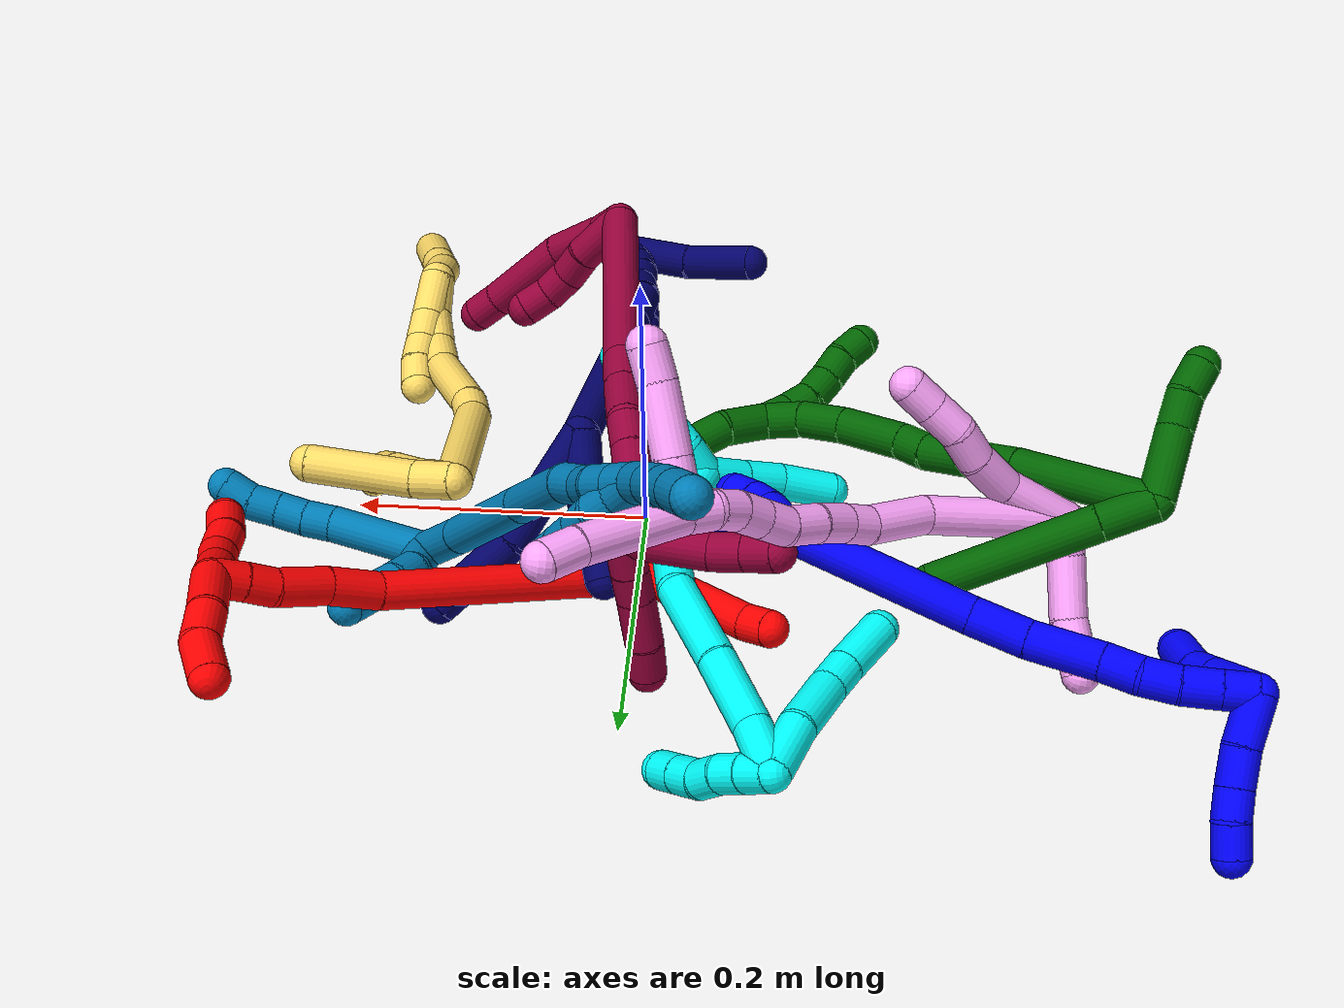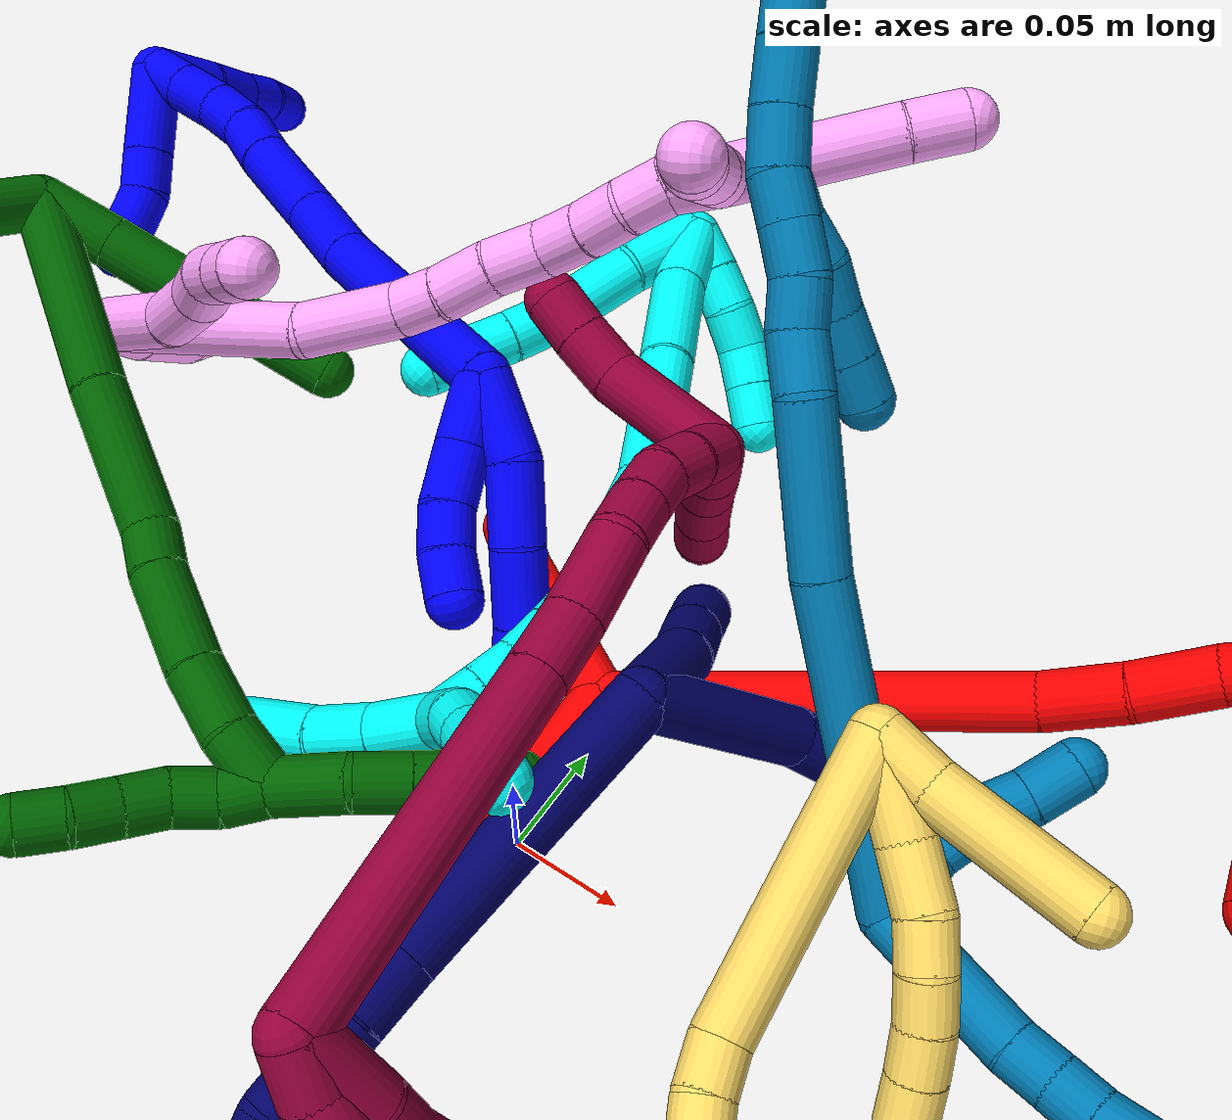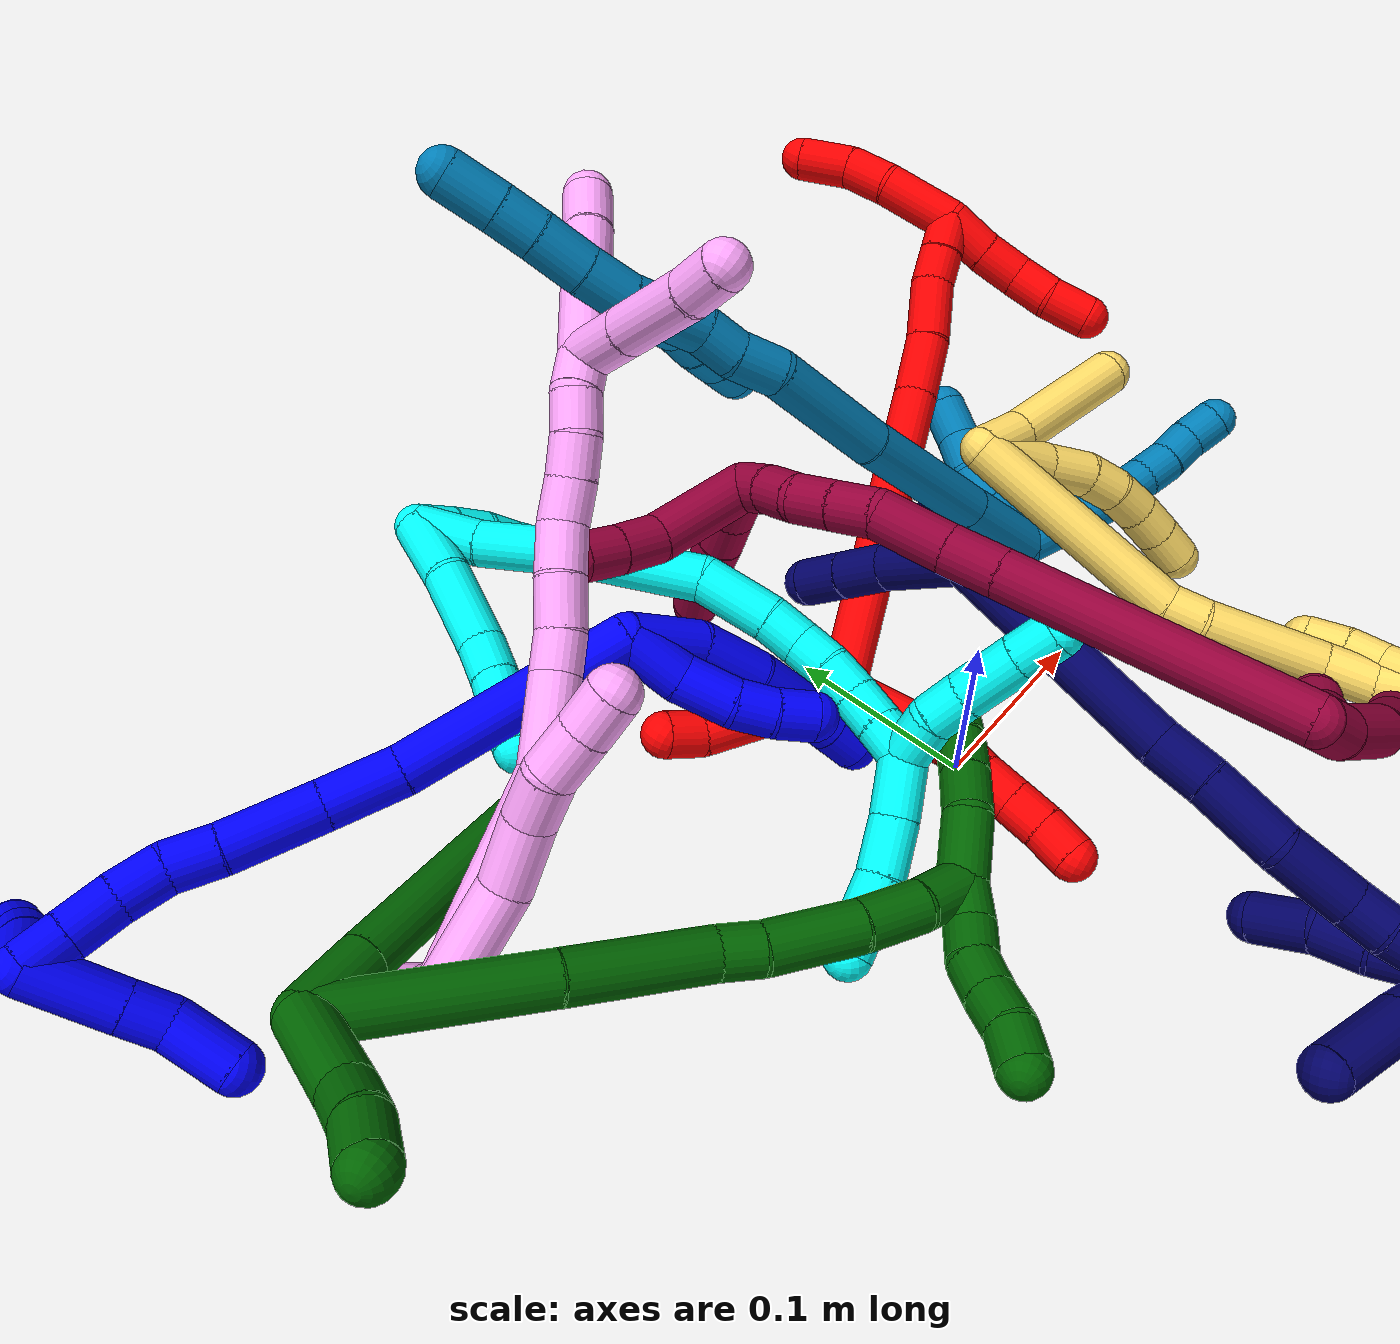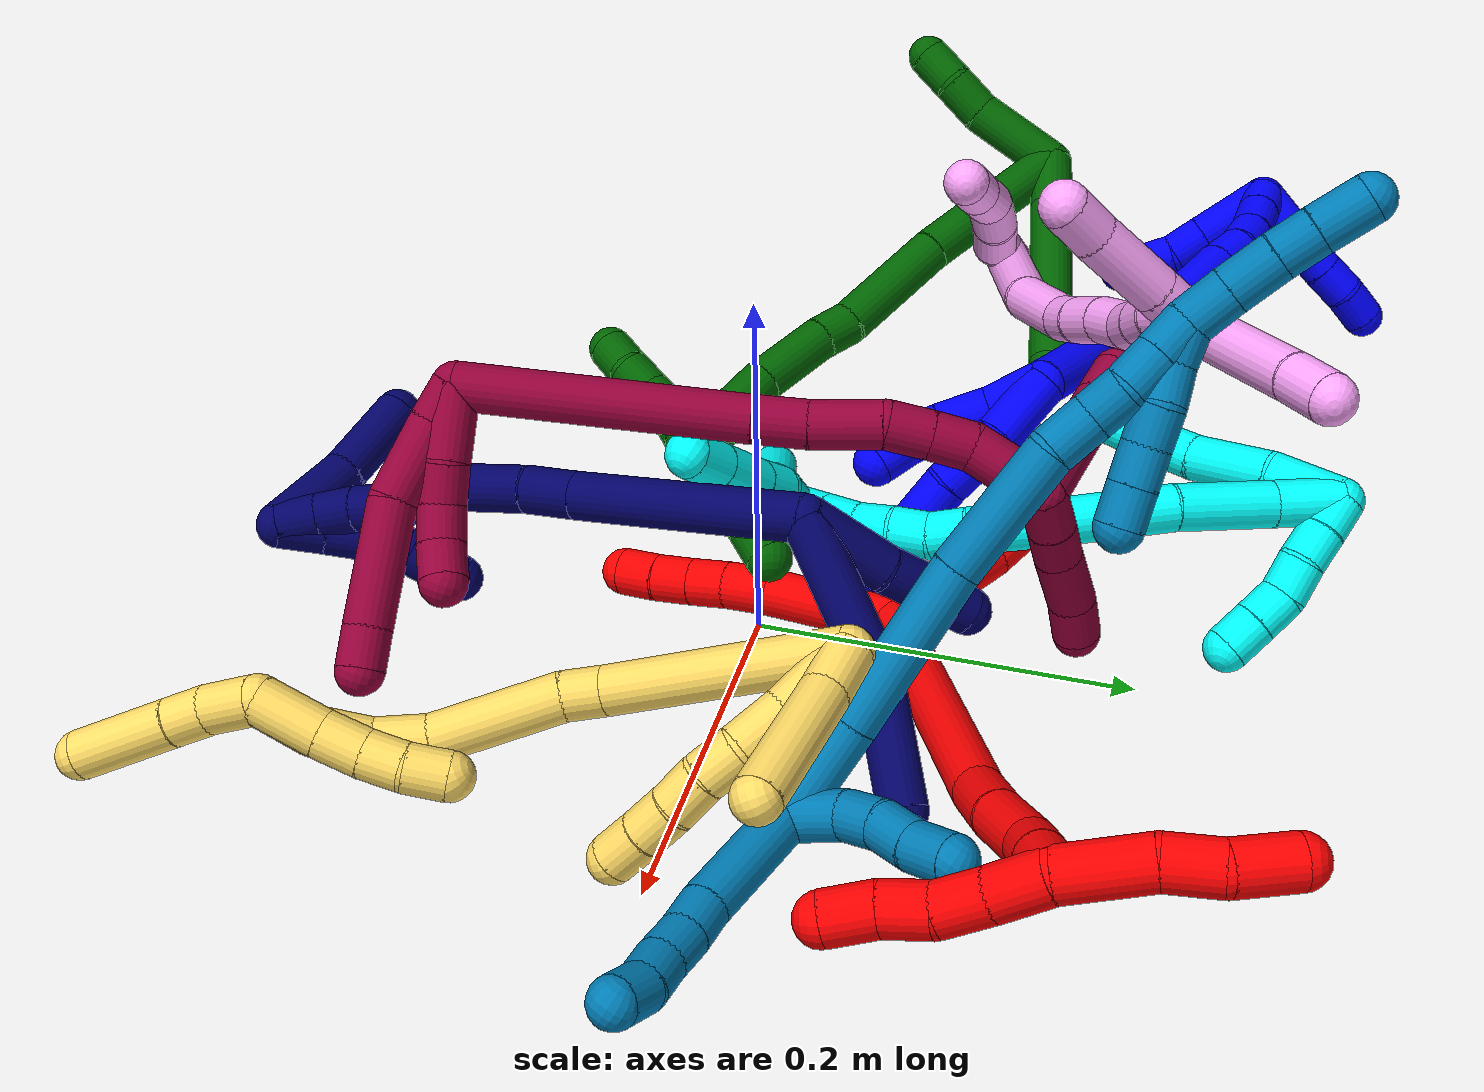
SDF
<sdf version="1.7">
 <world name="default">
  <plugin name="TubeGeneratorPlugin" filename="libtube_generator_plugin.so"/>
  <model name="photoneo_s_sensor">
   <static>1</static>
   <pose>0 0 2 1.57079 1.57079 3.14159</pose>
   <link name="link">
    <inertial><mass>0.1</mass></inertial>
    <sensor name="sensor" type="depth">
     <update_rate>30</update_rate>
     <camera>
      <horizontal_fov>1.22</horizontal_fov>
      <image><width>1920</width><height>1200</height><format>B8G8R8</format></image>
      <clip><near>0.1</near><far>4</far></clip>
      <depth_camera><output>points</output></depth_camera>
     </camera>
     <plugin name="camera_plugin" filename="libgazebo_ros_depth_camera.so">
      <baseline>0.2</baseline>
      <alwaysOn>1</alwaysOn>
      <updateRate>0.0</updateRate>
      <cameraName>camera_ir</cameraName>
      <imageTopicName>/camera/color/image_raw</imageTopicName>
      <cameraInfoTopicName>/camera/color/camera_info</cameraInfoTopicName>
      <depthImageTopicName>/camera/depth/image_raw</depthImageTopicName>
      <depthImageCameraInfoTopicName>/camera/depth/camera_info</depthImageCameraInfoTopicName>
      <pointCloudTopicName>/camera/depth/points</pointCloudTopicName>
      <frameName>fr_optical</frameName>
      <pointCloudCutoff>0.1</pointCloudCutoff>
      <pointCloudCutoffMax>2.0</pointCloudCutoffMax>
      <distortionK1>0</distortionK1>
      <distortionK2>0</distortionK2>
      <distortionK3>0</distortionK3>
      <distortionT1>0</distortionT1>
      <distortionT2>0</distortionT2>
      <CxPrime>0</CxPrime>
      <Cx>0</Cx>
      <Cy>0</Cy>
      <focalLength>0</focalLength>
      <hackBaseline>0</hackBaseline>
     </plugin>
    </sensor>
   </link>
  </model>
  <gravity>0 0 -9.8</gravity>
  <magnetic_field>6e-06 2.3e-05 -4.2e-05</magnetic_field>
  <atmosphere type="adiabatic"/>
  <physics name="default_physics" default="0" type="ode">
   <max_step_size>0.003</max_step_size>
   <real_time_factor>1</real_time_factor>
   <real_time_update_rate>1000</real_time_update_rate>
   <max_contacts>10000</max_contacts>
   <ode>
    <solver>
     <type>quick</type>
     <iters>100</iters>
     <sor>1.3</sor>
     <use_dynamic_moi_rescaling>0</use_dynamic_moi_rescaling>
    </solver>
    <constraints>
     <contact_max_correcting_vel>0</contact_max_correcting_vel>
     <contact_surface_layer>0.001</contact_surface_layer>
     <cfm>0</cfm>
     <erp>0.2</erp>
    </constraints>
   </ode>
  </physics>
  <scene><ambient>0.4 0.4 0.4 1</ambient><background>0.7 0.7 0.7 1</background><shadows>0</shadows></scene>
  <audio><device>default</device></audio>
  <spherical_coordinates>
   <surface_model>EARTH_WGS84</surface_model>
   <latitude_deg>0</latitude_deg>
   <longitude_deg>0</longitude_deg>
   <elevation>0</elevation>
   <heading_deg>0</heading_deg>
  </spherical_coordinates>
  <model name="bin">
   <static>1</static>
   <link name="bottom">
    <collision name="collision-bottom">
     <pose>0 0 -0.01 0 -0 0</pose>
     <geometry><box><size>0.8 0.6 0.02</size></box></geometry>
     <surface>
      <friction><ode><mu>100</mu><mu2>100</mu2></ode></friction>
      <contact><collide_bitmask>65535</collide_bitmask></contact>
     </surface>
    </collision>
   </link>
   <link name="west_wall">
    <collision name="collision-west_wall">
     <pose>-0.41 0 0.1 0 -0 0</pose>
     <geometry><box><size>0.02 0.6 0.2</size></box></geometry>
     <surface>
      <friction><ode><mu>100</mu><mu2>100</mu2></ode></friction>
      <contact><collide_bitmask>65535</collide_bitmask></contact>
     </surface>
    </collision>
   </link>
   <link name="east_wall">
    <collision name="collision-east_wall">
     <pose>0.41 0 0.1 0 -0 0</pose>
     <geometry><box><size>0.02 0.6 0.2</size></box></geometry>
     <surface>
      <friction><ode><mu>100</mu><mu2>100</mu2></ode></friction>
      <contact><collide_bitmask>65535</collide_bitmask></contact>
     </surface>
    </collision>
   </link>
   <link name="south_wall">
    <collision name="collision-south_wall">
     <pose>0 -0.31 0.1 0 -0 0</pose>
     <geometry><box><size>0.8 0.02 0.2</size></box></geometry>
     <surface>
      <friction><ode><mu>100</mu><mu2>100</mu2></ode></friction>
      <contact><collide_bitmask>65535</collide_bitmask></contact>
     </surface>
    </collision>
   </link>
   <link name="north_wall">
    <collision name="collision-north_wall">
     <pose>0 0.31 0.1 0 -0 0</pose>
     <geometry><box><size>0.8 0.02 0.2</size></box></geometry>
     <surface>
      <friction><ode><mu>100</mu><mu2>100</mu2></ode></friction>
      <contact><collide_bitmask>65535</collide_bitmask></contact>
     </surface>
    </collision>
   </link>
  </model>
  <model name="1">
   <static>0</static>
   <link name="1">
    <collision name="collision-cylinder-e_1_2_8">
     <pose>0.006859 -0.005844 -0.017224 2.81451 0.360626 1.6702</pose>
     <geometry><cylinder><radius>0.0125</radius><length>0.038877</length></cylinder></geometry>
     <surface>
      <friction><ode><mu>1.16</mu><mu2>1.16</mu2><slip1>0</slip1><slip2>0</slip2></ode></friction>
      <contact><ode><kp>1e+06</kp><kd>1</kd><max_vel>0</max_vel><min_depth>0.001</min_depth></ode></contact>
     </surface>
    </collision>
    <visual name="visual-cylinder-e_1_2_8">
     <pose>0.006859 -0.005844 -0.017224 2.81451 0.360626 1.6702</pose>
     <geometry><cylinder><radius>0.0125</radius><length>0.038877</length></cylinder></geometry>
     <material><ambient>0 0 1 1</ambient></material>
    </visual>
    <collision name="collision-cylinder-e_2_8_9">
     <pose>0.014441 -0.019079 -0.050878 2.71881 0.040101 0.18635</pose>
     <geometry><cylinder><radius>0.0125</radius><length>0.036063</length></cylinder></geometry>
     <surface>
      <friction><ode><mu>1.16</mu><mu2>1.16</mu2><slip1>0</slip1><slip2>0</slip2></ode></friction>
      <contact><ode><kp>1e+06</kp><kd>1</kd><max_vel>0</max_vel><min_depth>0.001</min_depth></ode></contact>
     </surface>
    </collision>
    <visual name="visual-cylinder-e_2_8_9">
     <pose>0.014441 -0.019079 -0.050878 2.71881 0.040101 0.18635</pose>
     <geometry><cylinder><radius>0.0125</radius><length>0.036063</length></cylinder></geometry>
     <material><ambient>0 0 1 1</ambient></material>
    </visual>
    <collision name="collision-cylinder-e_3_9_10">
     <pose>0.014152 -0.031517 -0.083776 2.8443 -0.058655 -0.386902</pose>
     <geometry><cylinder><radius>0.0125</radius><length>0.034507</length></cylinder></geometry>
     <surface>
      <friction><ode><mu>1.16</mu><mu2>1.16</mu2><slip1>0</slip1><slip2>0</slip2></ode></friction>
      <contact><ode><kp>1e+06</kp><kd>1</kd><max_vel>0</max_vel><min_depth>0.001</min_depth></ode></contact>
     </surface>
    </collision>
    <visual name="visual-cylinder-e_3_9_10">
     <pose>0.014152 -0.031517 -0.083776 2.8443 -0.058655 -0.386902</pose>
     <geometry><cylinder><radius>0.0125</radius><length>0.034507</length></cylinder></geometry>
     <material><ambient>0 0 1 1</ambient></material>
    </visual>
    <collision name="collision-cylinder-e_4_10_11">
     <pose>0.011957 -0.040193 -0.10978 2.77781 -0.115483 -0.609034</pose>
     <geometry><cylinder><radius>0.0125</radius><length>0.020542</length></cylinder></geometry>
     <surface>
      <friction><ode><mu>1.16</mu><mu2>1.16</mu2><slip1>0</slip1><slip2>0</slip2></ode></friction>
      <contact><ode><kp>1e+06</kp><kd>1</kd><max_vel>0</max_vel><min_depth>0.001</min_depth></ode></contact>
     </surface>
    </collision>
    <visual name="visual-cylinder-e_4_10_11">
     <pose>0.011957 -0.040193 -0.10978 2.77781 -0.115483 -0.609034</pose>
     <geometry><cylinder><radius>0.0125</radius><length>0.020542</length></cylinder></geometry>
     <material><ambient>0 0 1 1</ambient></material>
    </visual>
    <collision name="collision-cylinder-e_5_11_6">
     <pose>0.009792 -0.047221 -0.128674 2.79332 -0.098311 -0.545357</pose>
     <geometry><cylinder><radius>0.0125</radius><length>0.020012</length></cylinder></geometry>
     <surface>
      <friction><ode><mu>1.16</mu><mu2>1.16</mu2><slip1>0</slip1><slip2>0</slip2></ode></friction>
      <contact><ode><kp>1e+06</kp><kd>1</kd><max_vel>0</max_vel><min_depth>0.001</min_depth></ode></contact>
     </surface>
    </collision>
    <visual name="visual-cylinder-e_5_11_6">
     <pose>0.009792 -0.047221 -0.128674 2.79332 -0.098311 -0.545357</pose>
     <geometry><cylinder><radius>0.0125</radius><length>0.020012</length></cylinder></geometry>
     <material><ambient>0 0 1 1</ambient></material>
    </visual>
    <collision name="collision-cylinder-e_1_2_12">
     <pose>-0.002365 -0.009845 -0.011833 2.44762 -0.152476 -0.416347</pose>
     <geometry><cylinder><radius>0.0125</radius><length>0.031147</length></cylinder></geometry>
     <surface>
      <friction><ode><mu>1.16</mu><mu2>1.16</mu2><slip1>0</slip1><slip2>0</slip2></ode></friction>
      <contact><ode><kp>1e+06</kp><kd>1</kd><max_vel>0</max_vel><min_depth>0.001</min_depth></ode></contact>
     </surface>
    </collision>
    <visual name="visual-cylinder-e_1_2_12">
     <pose>-0.002365 -0.009845 -0.011833 2.44762 -0.152476 -0.416347</pose>
     <geometry><cylinder><radius>0.0125</radius><length>0.031147</length></cylinder></geometry>
     <material><ambient>0 0 1 1</ambient></material>
    </visual>
    <collision name="collision-cylinder-e_2_12_13">
     <pose>-0.004035 -0.0304 -0.033031 2.28935 0.048846 0.107524</pose>
     <geometry><cylinder><radius>0.0125</radius><length>0.028489</length></cylinder></geometry>
     <surface>
      <friction><ode><mu>1.16</mu><mu2>1.16</mu2><slip1>0</slip1><slip2>0</slip2></ode></friction>
      <contact><ode><kp>1e+06</kp><kd>1</kd><max_vel>0</max_vel><min_depth>0.001</min_depth></ode></contact>
     </surface>
    </collision>
    <visual name="visual-cylinder-e_2_12_13">
     <pose>-0.004035 -0.0304 -0.033031 2.28935 0.048846 0.107524</pose>
     <geometry><cylinder><radius>0.0125</radius><length>0.028489</length></cylinder></geometry>
     <material><ambient>0 0 1 1</ambient></material>
    </visual>
    <collision name="collision-cylinder-e_3_13_14">
     <pose>-0.000859 -0.047622 -0.049666 2.41109 0.248924 0.632371</pose>
     <geometry><cylinder><radius>0.0125</radius><length>0.020139</length></cylinder></geometry>
     <surface>
      <friction><ode><mu>1.16</mu><mu2>1.16</mu2><slip1>0</slip1><slip2>0</slip2></ode></friction>
      <contact><ode><kp>1e+06</kp><kd>1</kd><max_vel>0</max_vel><min_depth>0.001</min_depth></ode></contact>
     </surface>
    </collision>
    <visual name="visual-cylinder-e_3_13_14">
     <pose>-0.000859 -0.047622 -0.049666 2.41109 0.248924 0.632371</pose>
     <geometry><cylinder><radius>0.0125</radius><length>0.020139</length></cylinder></geometry>
     <material><ambient>0 0 1 1</ambient></material>
    </visual>
    <collision name="collision-cylinder-e_4_14_5">
     <pose>0.005477 -0.059534 -0.064566 2.5257 0.391119 1.11404</pose>
     <geometry><cylinder><radius>0.0125</radius><length>0.020225</length></cylinder></geometry>
     <surface>
      <friction><ode><mu>1.16</mu><mu2>1.16</mu2><slip1>0</slip1><slip2>0</slip2></ode></friction>
      <contact><ode><kp>1e+06</kp><kd>1</kd><max_vel>0</max_vel><min_depth>0.001</min_depth></ode></contact>
     </surface>
    </collision>
    <visual name="visual-cylinder-e_4_14_5">
     <pose>0.005477 -0.059534 -0.064566 2.5257 0.391119 1.11404</pose>
     <geometry><cylinder><radius>0.0125</radius><length>0.020225</length></cylinder></geometry>
     <material><ambient>0 0 1 1</ambient></material>
    </visual>
    <collision name="collision-cylinder-e_1_2_15">
     <pose>-0.051343 0.020906 0.023048 -0.736695 -1.02594 0.428135</pose>
     <geometry><cylinder><radius>0.0125</radius><length>0.120073</length></cylinder></geometry>
     <surface>
      <friction><ode><mu>1.16</mu><mu2>1.16</mu2><slip1>0</slip1><slip2>0</slip2></ode></friction>
      <contact><ode><kp>1e+06</kp><kd>1</kd><max_vel>0</max_vel><min_depth>0.001</min_depth></ode></contact>
     </surface>
    </collision>
    <visual name="visual-cylinder-e_1_2_15">
     <pose>-0.051343 0.020906 0.023048 -0.736695 -1.02594 0.428135</pose>
     <geometry><cylinder><radius>0.0125</radius><length>0.120073</length></cylinder></geometry>
     <material><ambient>0 0 1 1</ambient></material>
    </visual>
    <collision name="collision-cylinder-e_2_15_16">
     <pose>-0.117729 0.049066 0.055466 -0.65888 -0.903552 0.328817</pose>
     <geometry><cylinder><radius>0.0125</radius><length>0.038298</length></cylinder></geometry>
     <surface>
      <friction><ode><mu>1.16</mu><mu2>1.16</mu2><slip1>0</slip1><slip2>0</slip2></ode></friction>
      <contact><ode><kp>1e+06</kp><kd>1</kd><max_vel>0</max_vel><min_depth>0.001</min_depth></ode></contact>
     </surface>
    </collision>
    <visual name="visual-cylinder-e_2_15_16">
     <pose>-0.117729 0.049066 0.055466 -0.65888 -0.903552 0.328817</pose>
     <geometry><cylinder><radius>0.0125</radius><length>0.038298</length></cylinder></geometry>
     <material><ambient>0 0 1 1</ambient></material>
    </visual>
    <collision name="collision-cylinder-e_3_16_17">
     <pose>-0.150919 0.063651 0.078303 -0.498429 -0.869257 0.23521</pose>
     <geometry><cylinder><radius>0.0125</radius><length>0.047517</length></cylinder></geometry>
     <surface>
      <friction><ode><mu>1.16</mu><mu2>1.16</mu2><slip1>0</slip1><slip2>0</slip2></ode></friction>
      <contact><ode><kp>1e+06</kp><kd>1</kd><max_vel>0</max_vel><min_depth>0.001</min_depth></ode></contact>
     </surface>
    </collision>
    <visual name="visual-cylinder-e_3_16_17">
     <pose>-0.150919 0.063651 0.078303 -0.498429 -0.869257 0.23521</pose>
     <geometry><cylinder><radius>0.0125</radius><length>0.047517</length></cylinder></geometry>
     <material><ambient>0 0 1 1</ambient></material>
    </visual>
    <collision name="collision-cylinder-e_4_17_18">
     <pose>-0.17777 0.075695 0.098809 -0.590072 -0.798954 0.255209</pose>
     <geometry><cylinder><radius>0.0125</radius><length>0.02429</length></cylinder></geometry>
     <surface>
      <friction><ode><mu>1.16</mu><mu2>1.16</mu2><slip1>0</slip1><slip2>0</slip2></ode></friction>
      <contact><ode><kp>1e+06</kp><kd>1</kd><max_vel>0</max_vel><min_depth>0.001</min_depth></ode></contact>
     </surface>
    </collision>
    <visual name="visual-cylinder-e_4_17_18">
     <pose>-0.17777 0.075695 0.098809 -0.590072 -0.798954 0.255209</pose>
     <geometry><cylinder><radius>0.0125</radius><length>0.02429</length></cylinder></geometry>
     <material><ambient>0 0 1 1</ambient></material>
    </visual>
    <collision name="collision-cylinder-e_5_18_19">
     <pose>-0.19646 0.082627 0.111757 -0.359269 -1.00708 0.199418</pose>
     <geometry><cylinder><radius>0.0125</radius><length>0.023629</length></cylinder></geometry>
     <surface>
      <friction><ode><mu>1.16</mu><mu2>1.16</mu2><slip1>0</slip1><slip2>0</slip2></ode></friction>
      <contact><ode><kp>1e+06</kp><kd>1</kd><max_vel>0</max_vel><min_depth>0.001</min_depth></ode></contact>
     </surface>
    </collision>
    <visual name="visual-cylinder-e_5_18_19">
     <pose>-0.19646 0.082627 0.111757 -0.359269 -1.00708 0.199418</pose>
     <geometry><cylinder><radius>0.0125</radius><length>0.023629</length></cylinder></geometry>
     <material><ambient>0 0 1 1</ambient></material>
    </visual>
    <collision name="collision-cylinder-e_6_19_20">
     <pose>-0.217166 0.085413 0.123987 -0.089325 -1.03635 0.050951</pose>
     <geometry><cylinder><radius>0.0125</radius><length>0.024913</length></cylinder></geometry>
     <surface>
      <friction><ode><mu>1.16</mu><mu2>1.16</mu2><slip1>0</slip1><slip2>0</slip2></ode></friction>
      <contact><ode><kp>1e+06</kp><kd>1</kd><max_vel>0</max_vel><min_depth>0.001</min_depth></ode></contact>
     </surface>
    </collision>
    <visual name="visual-cylinder-e_6_19_20">
     <pose>-0.217166 0.085413 0.123987 -0.089325 -1.03635 0.050951</pose>
     <geometry><cylinder><radius>0.0125</radius><length>0.024913</length></cylinder></geometry>
     <material><ambient>0 0 1 1</ambient></material>
    </visual>
    <collision name="collision-cylinder-e_7_20_1">
     <pose>-0.237019 0.086365 0.135751 -0.070692 -1.03212 0.040118</pose>
     <geometry><cylinder><radius>0.0125</radius><length>0.02128</length></cylinder></geometry>
     <surface>
      <friction><ode><mu>1.16</mu><mu2>1.16</mu2><slip1>0</slip1><slip2>0</slip2></ode></friction>
      <contact><ode><kp>1e+06</kp><kd>1</kd><max_vel>0</max_vel><min_depth>0.001</min_depth></ode></contact>
     </surface>
    </collision>
    <visual name="visual-cylinder-e_7_20_1">
     <pose>-0.237019 0.086365 0.135751 -0.070692 -1.03212 0.040118</pose>
     <geometry><cylinder><radius>0.0125</radius><length>0.02128</length></cylinder></geometry>
     <material><ambient>0 0 1 1</ambient></material>
    </visual>
    <collision name="collision-cylinder-e_1_1_21">
     <pose>-0.245091 0.074022 0.122911 2.53348 0.047564 0.151321</pose>
     <geometry><cylinder><radius>0.0125</radius><length>0.044608</length></cylinder></geometry>
     <surface>
      <friction><ode><mu>1.16</mu><mu2>1.16</mu2><slip1>0</slip1><slip2>0</slip2></ode></friction>
      <contact><ode><kp>1e+06</kp><kd>1</kd><max_vel>0</max_vel><min_depth>0.001</min_depth></ode></contact>
     </surface>
    </collision>
    <visual name="visual-cylinder-e_1_1_21">
     <pose>-0.245091 0.074022 0.122911 2.53348 0.047564 0.151321</pose>
     <geometry><cylinder><radius>0.0125</radius><length>0.044608</length></cylinder></geometry>
     <material><ambient>0 0 1 1</ambient></material>
    </visual>
    <collision name="collision-cylinder-e_2_21_22">
     <pose>-0.243363 0.055272 0.095852 2.5401 0.06264 0.201347</pose>
     <geometry><cylinder><radius>0.0125</radius><length>0.021325</length></cylinder></geometry>
     <surface>
      <friction><ode><mu>1.16</mu><mu2>1.16</mu2><slip1>0</slip1><slip2>0</slip2></ode></friction>
      <contact><ode><kp>1e+06</kp><kd>1</kd><max_vel>0</max_vel><min_depth>0.001</min_depth></ode></contact>
     </surface>
    </collision>
    <visual name="visual-cylinder-e_2_21_22">
     <pose>-0.243363 0.055272 0.095852 2.5401 0.06264 0.201347</pose>
     <geometry><cylinder><radius>0.0125</radius><length>0.021325</length></cylinder></geometry>
     <material><ambient>0 0 1 1</ambient></material>
    </visual>
    <collision name="collision-cylinder-e_3_22_4">
     <pose>-0.244433 0.036269 0.076187 2.26884 -0.102178 -0.218413</pose>
     <geometry><cylinder><radius>0.0125</radius><length>0.034067</length></cylinder></geometry>
     <surface>
      <friction><ode><mu>1.16</mu><mu2>1.16</mu2><slip1>0</slip1><slip2>0</slip2></ode></friction>
      <contact><ode><kp>1e+06</kp><kd>1</kd><max_vel>0</max_vel><min_depth>0.001</min_depth></ode></contact>
     </surface>
    </collision>
    <visual name="visual-cylinder-e_3_22_4">
     <pose>-0.244433 0.036269 0.076187 2.26884 -0.102178 -0.218413</pose>
     <geometry><cylinder><radius>0.0125</radius><length>0.034067</length></cylinder></geometry>
     <material><ambient>0 0 1 1</ambient></material>
    </visual>
    <collision name="collision-cylinder-e_1_1_23">
     <pose>-0.246144 0.10148 0.133186 -2.06886 0.000452 -0.000761</pose>
     <geometry><cylinder><radius>0.0125</radius><length>0.033533</length></cylinder></geometry>
     <surface>
      <friction><ode><mu>1.16</mu><mu2>1.16</mu2><slip1>0</slip1><slip2>0</slip2></ode></friction>
      <contact><ode><kp>1e+06</kp><kd>1</kd><max_vel>0</max_vel><min_depth>0.001</min_depth></ode></contact>
     </surface>
    </collision>
    <visual name="visual-cylinder-e_1_1_23">
     <pose>-0.246144 0.10148 0.133186 -2.06886 0.000452 -0.000761</pose>
     <geometry><cylinder><radius>0.0125</radius><length>0.033533</length></cylinder></geometry>
     <material><ambient>0 0 1 1</ambient></material>
    </visual>
    <collision name="collision-cylinder-e_2_23_24">
     <pose>-0.247955 0.12711 0.119441 -2.05509 -0.14655 0.241938</pose>
     <geometry><cylinder><radius>0.0125</radius><length>0.024902</length></cylinder></geometry>
     <surface>
      <friction><ode><mu>1.16</mu><mu2>1.16</mu2><slip1>0</slip1><slip2>0</slip2></ode></friction>
      <contact><ode><kp>1e+06</kp><kd>1</kd><max_vel>0</max_vel><min_depth>0.001</min_depth></ode></contact>
     </surface>
    </collision>
    <visual name="visual-cylinder-e_2_23_24">
     <pose>-0.247955 0.12711 0.119441 -2.05509 -0.14655 0.241938</pose>
     <geometry><cylinder><radius>0.0125</radius><length>0.024902</length></cylinder></geometry>
     <material><ambient>0 0 1 1</ambient></material>
    </visual>
    <collision name="collision-cylinder-e_3_24_25">
     <pose>-0.251393 0.147098 0.109819 -1.975 -0.162505 0.245563</pose>
     <geometry><cylinder><radius>0.0125</radius><length>0.02003</length></cylinder></geometry>
     <surface>
      <friction><ode><mu>1.16</mu><mu2>1.16</mu2><slip1>0</slip1><slip2>0</slip2></ode></friction>
      <contact><ode><kp>1e+06</kp><kd>1</kd><max_vel>0</max_vel><min_depth>0.001</min_depth></ode></contact>
     </surface>
    </collision>
    <visual name="visual-cylinder-e_3_24_25">
     <pose>-0.251393 0.147098 0.109819 -1.975 -0.162505 0.245563</pose>
     <geometry><cylinder><radius>0.0125</radius><length>0.02003</length></cylinder></geometry>
     <material><ambient>0 0 1 1</ambient></material>
    </visual>
    <collision name="collision-cylinder-e_4_25_3">
     <pose>-0.256838 0.165055 0.101176 -2.06293 -0.363094 0.595192</pose>
     <geometry><cylinder><radius>0.0125</radius><length>0.021535</length></cylinder></geometry>
     <surface>
      <friction><ode><mu>1.16</mu><mu2>1.16</mu2><slip1>0</slip1><slip2>0</slip2></ode></friction>
      <contact><ode><kp>1e+06</kp><kd>1</kd><max_vel>0</max_vel><min_depth>0.001</min_depth></ode></contact>
     </surface>
    </collision>
    <visual name="visual-cylinder-e_4_25_3">
     <pose>-0.256838 0.165055 0.101176 -2.06293 -0.363094 0.595192</pose>
     <geometry><cylinder><radius>0.0125</radius><length>0.021535</length></cylinder></geometry>
     <material><ambient>0 0 1 1</ambient></material>
    </visual>
    <collision name="collision-sphere-3">
     <pose>-0.260662 0.173926 0.09642 0 -0 0</pose>
     <geometry><sphere><radius>0.0125</radius></sphere></geometry>
     <surface>
      <friction><ode><mu>1.16</mu><mu2>1.16</mu2><slip1>0</slip1><slip2>0</slip2></ode></friction>
      <contact><ode><kp>1e+06</kp><kd>1</kd><max_vel>0</max_vel><min_depth>0.001</min_depth></ode></contact>
     </surface>
    </collision>
    <visual name="visual-sphere-3">
     <pose>-0.260662 0.173926 0.09642 0 -0 0</pose>
     <geometry><sphere><radius>0.0125</radius></sphere></geometry>
     <material><ambient>0 0 1 1</ambient></material>
    </visual>
    <collision name="collision-sphere-25">
     <pose>-0.253014 0.156184 0.105932 0 -0 0</pose>
     <geometry><sphere><radius>0.0125</radius></sphere></geometry>
     <surface>
      <friction><ode><mu>1.16</mu><mu2>1.16</mu2><slip1>0</slip1><slip2>0</slip2></ode></friction>
      <contact><ode><kp>1e+06</kp><kd>1</kd><max_vel>0</max_vel><min_depth>0.001</min_depth></ode></contact>
     </surface>
    </collision>
    <visual name="visual-sphere-25">
     <pose>-0.253014 0.156184 0.105932 0 -0 0</pose>
     <geometry><sphere><radius>0.0125</radius></sphere></geometry>
     <material><ambient>0 0 1 1</ambient></material>
    </visual>
    <collision name="collision-sphere-24">
     <pose>-0.249773 0.138011 0.113706 0 -0 0</pose>
     <geometry><sphere><radius>0.0125</radius></sphere></geometry>
     <surface>
      <friction><ode><mu>1.16</mu><mu2>1.16</mu2><slip1>0</slip1><slip2>0</slip2></ode></friction>
      <contact><ode><kp>1e+06</kp><kd>1</kd><max_vel>0</max_vel><min_depth>0.001</min_depth></ode></contact>
     </surface>
    </collision>
    <visual name="visual-sphere-24">
     <pose>-0.249773 0.138011 0.113706 0 -0 0</pose>
     <geometry><sphere><radius>0.0125</radius></sphere></geometry>
     <material><ambient>0 0 1 1</ambient></material>
    </visual>
    <collision name="collision-sphere-23">
     <pose>-0.246137 0.116209 0.125176 0 -0 0</pose>
     <geometry><sphere><radius>0.0125</radius></sphere></geometry>
     <surface>
      <friction><ode><mu>1.16</mu><mu2>1.16</mu2><slip1>0</slip1><slip2>0</slip2></ode></friction>
      <contact><ode><kp>1e+06</kp><kd>1</kd><max_vel>0</max_vel><min_depth>0.001</min_depth></ode></contact>
     </surface>
    </collision>
    <visual name="visual-sphere-23">
     <pose>-0.246137 0.116209 0.125176 0 -0 0</pose>
     <geometry><sphere><radius>0.0125</radius></sphere></geometry>
     <material><ambient>0 0 1 1</ambient></material>
    </visual>
    <collision name="collision-sphere-4">
     <pose>-0.246171 0.023287 0.065297 0 -0 0</pose>
     <geometry><sphere><radius>0.0125</radius></sphere></geometry>
     <surface>
      <friction><ode><mu>1.16</mu><mu2>1.16</mu2><slip1>0</slip1><slip2>0</slip2></ode></friction>
      <contact><ode><kp>1e+06</kp><kd>1</kd><max_vel>0</max_vel><min_depth>0.001</min_depth></ode></contact>
     </surface>
    </collision>
    <visual name="visual-sphere-4">
     <pose>-0.246171 0.023287 0.065297 0 -0 0</pose>
     <geometry><sphere><radius>0.0125</radius></sphere></geometry>
     <material><ambient>0 0 1 1</ambient></material>
    </visual>
    <collision name="collision-sphere-22">
     <pose>-0.242696 0.04925 0.087078 0 -0 0</pose>
     <geometry><sphere><radius>0.0125</radius></sphere></geometry>
     <surface>
      <friction><ode><mu>1.16</mu><mu2>1.16</mu2><slip1>0</slip1><slip2>0</slip2></ode></friction>
      <contact><ode><kp>1e+06</kp><kd>1</kd><max_vel>0</max_vel><min_depth>0.001</min_depth></ode></contact>
     </surface>
    </collision>
    <visual name="visual-sphere-22">
     <pose>-0.242696 0.04925 0.087078 0 -0 0</pose>
     <geometry><sphere><radius>0.0125</radius></sphere></geometry>
     <material><ambient>0 0 1 1</ambient></material>
    </visual>
    <collision name="collision-sphere-21">
     <pose>-0.244031 0.061294 0.104626 0 -0 0</pose>
     <geometry><sphere><radius>0.0125</radius></sphere></geometry>
     <surface>
      <friction><ode><mu>1.16</mu><mu2>1.16</mu2><slip1>0</slip1><slip2>0</slip2></ode></friction>
      <contact><ode><kp>1e+06</kp><kd>1</kd><max_vel>0</max_vel><min_depth>0.001</min_depth></ode></contact>
     </surface>
    </collision>
    <visual name="visual-sphere-21">
     <pose>-0.244031 0.061294 0.104626 0 -0 0</pose>
     <geometry><sphere><radius>0.0125</radius></sphere></geometry>
     <material><ambient>0 0 1 1</ambient></material>
    </visual>
    <collision name="collision-sphere-1">
     <pose>-0.246152 0.08675 0.141195 0 -0 0</pose>
     <geometry><sphere><radius>0.0125</radius></sphere></geometry>
     <surface>
      <friction><ode><mu>1.16</mu><mu2>1.16</mu2><slip1>0</slip1><slip2>0</slip2></ode></friction>
      <contact><ode><kp>1e+06</kp><kd>1</kd><max_vel>0</max_vel><min_depth>0.001</min_depth></ode></contact>
     </surface>
    </collision>
    <visual name="visual-sphere-1">
     <pose>-0.246152 0.08675 0.141195 0 -0 0</pose>
     <geometry><sphere><radius>0.0125</radius></sphere></geometry>
     <material><ambient>0 0 1 1</ambient></material>
    </visual>
    <collision name="collision-sphere-6">
     <pose>0.00881 -0.050619 -0.138034 0 -0 0</pose>
     <geometry><sphere><radius>0.0125</radius></sphere></geometry>
     <surface>
      <friction><ode><mu>1.16</mu><mu2>1.16</mu2><slip1>0</slip1><slip2>0</slip2></ode></friction>
      <contact><ode><kp>1e+06</kp><kd>1</kd><max_vel>0</max_vel><min_depth>0.001</min_depth></ode></contact>
     </surface>
    </collision>
    <visual name="visual-sphere-6">
     <pose>0.00881 -0.050619 -0.138034 0 -0 0</pose>
     <geometry><sphere><radius>0.0125</radius></sphere></geometry>
     <material><ambient>0 0 1 1</ambient></material>
    </visual>
    <collision name="collision-sphere-11">
     <pose>0.010774 -0.043823 -0.119315 0 -0 0</pose>
     <geometry><sphere><radius>0.0125</radius></sphere></geometry>
     <surface>
      <friction><ode><mu>1.16</mu><mu2>1.16</mu2><slip1>0</slip1><slip2>0</slip2></ode></friction>
      <contact><ode><kp>1e+06</kp><kd>1</kd><max_vel>0</max_vel><min_depth>0.001</min_depth></ode></contact>
     </surface>
    </collision>
    <visual name="visual-sphere-11">
     <pose>0.010774 -0.043823 -0.119315 0 -0 0</pose>
     <geometry><sphere><radius>0.0125</radius></sphere></geometry>
     <material><ambient>0 0 1 1</ambient></material>
    </visual>
    <collision name="collision-sphere-10">
     <pose>0.013141 -0.036562 -0.100245 0 -0 0</pose>
     <geometry><sphere><radius>0.0125</radius></sphere></geometry>
     <surface>
      <friction><ode><mu>1.16</mu><mu2>1.16</mu2><slip1>0</slip1><slip2>0</slip2></ode></friction>
      <contact><ode><kp>1e+06</kp><kd>1</kd><max_vel>0</max_vel><min_depth>0.001</min_depth></ode></contact>
     </surface>
    </collision>
    <visual name="visual-sphere-10">
     <pose>0.013141 -0.036562 -0.100245 0 -0 0</pose>
     <geometry><sphere><radius>0.0125</radius></sphere></geometry>
     <material><ambient>0 0 1 1</ambient></material>
    </visual>
    <collision name="collision-sphere-9">
     <pose>0.015164 -0.026472 -0.067308 0 -0 0</pose>
     <geometry><sphere><radius>0.0125</radius></sphere></geometry>
     <surface>
      <friction><ode><mu>1.16</mu><mu2>1.16</mu2><slip1>0</slip1><slip2>0</slip2></ode></friction>
      <contact><ode><kp>1e+06</kp><kd>1</kd><max_vel>0</max_vel><min_depth>0.001</min_depth></ode></contact>
     </surface>
    </collision>
    <visual name="visual-sphere-9">
     <pose>0.015164 -0.026472 -0.067308 0 -0 0</pose>
     <geometry><sphere><radius>0.0125</radius></sphere></geometry>
     <material><ambient>0 0 1 1</ambient></material>
    </visual>
    <collision name="collision-sphere-2">
     <geometry><sphere><radius>0.0125</radius></sphere></geometry>
     <surface>
      <friction><ode><mu>1.16</mu><mu2>1.16</mu2><slip1>0</slip1><slip2>0</slip2></ode></friction>
      <contact><ode><kp>1e+06</kp><kd>1</kd><max_vel>0</max_vel><min_depth>0.001</min_depth></ode></contact>
     </surface>
    </collision>
    <visual name="visual-sphere-2">
     <geometry><sphere><radius>0.0125</radius></sphere></geometry>
     <material><ambient>0 0 1 1</ambient></material>
    </visual>
    <collision name="collision-sphere-19">
     <pose>-0.206447 0.084847 0.117667 0 -0 0</pose>
     <geometry><sphere><radius>0.0125</radius></sphere></geometry>
     <surface>
      <friction><ode><mu>1.16</mu><mu2>1.16</mu2><slip1>0</slip1><slip2>0</slip2></ode></friction>
      <contact><ode><kp>1e+06</kp><kd>1</kd><max_vel>0</max_vel><min_depth>0.001</min_depth></ode></contact>
     </surface>
    </collision>
    <visual name="visual-sphere-19">
     <pose>-0.206447 0.084847 0.117667 0 -0 0</pose>
     <geometry><sphere><radius>0.0125</radius></sphere></geometry>
     <material><ambient>0 0 1 1</ambient></material>
    </visual>
    <collision name="collision-sphere-8">
     <pose>0.013718 -0.011687 -0.034447 0 -0 0</pose>
     <geometry><sphere><radius>0.0125</radius></sphere></geometry>
     <surface>
      <friction><ode><mu>1.16</mu><mu2>1.16</mu2><slip1>0</slip1><slip2>0</slip2></ode></friction>
      <contact><ode><kp>1e+06</kp><kd>1</kd><max_vel>0</max_vel><min_depth>0.001</min_depth></ode></contact>
     </surface>
    </collision>
    <visual name="visual-sphere-8">
     <pose>0.013718 -0.011687 -0.034447 0 -0 0</pose>
     <geometry><sphere><radius>0.0125</radius></sphere></geometry>
     <material><ambient>0 0 1 1</ambient></material>
    </visual>
    <collision name="collision-sphere-12">
     <pose>-0.004731 -0.01969 -0.023665 0 -0 0</pose>
     <geometry><sphere><radius>0.0125</radius></sphere></geometry>
     <surface>
      <friction><ode><mu>1.16</mu><mu2>1.16</mu2><slip1>0</slip1><slip2>0</slip2></ode></friction>
      <contact><ode><kp>1e+06</kp><kd>1</kd><max_vel>0</max_vel><min_depth>0.001</min_depth></ode></contact>
     </surface>
    </collision>
    <visual name="visual-sphere-12">
     <pose>-0.004731 -0.01969 -0.023665 0 -0 0</pose>
     <geometry><sphere><radius>0.0125</radius></sphere></geometry>
     <material><ambient>0 0 1 1</ambient></material>
    </visual>
    <collision name="collision-sphere-13">
     <pose>-0.00334 -0.04111 -0.042397 0 -0 0</pose>
     <geometry><sphere><radius>0.0125</radius></sphere></geometry>
     <surface>
      <friction><ode><mu>1.16</mu><mu2>1.16</mu2><slip1>0</slip1><slip2>0</slip2></ode></friction>
      <contact><ode><kp>1e+06</kp><kd>1</kd><max_vel>0</max_vel><min_depth>0.001</min_depth></ode></contact>
     </surface>
    </collision>
    <visual name="visual-sphere-13">
     <pose>-0.00334 -0.04111 -0.042397 0 -0 0</pose>
     <geometry><sphere><radius>0.0125</radius></sphere></geometry>
     <material><ambient>0 0 1 1</ambient></material>
    </visual>
    <collision name="collision-sphere-14">
     <pose>0.001622 -0.054134 -0.056935 0 -0 0</pose>
     <geometry><sphere><radius>0.0125</radius></sphere></geometry>
     <surface>
      <friction><ode><mu>1.16</mu><mu2>1.16</mu2><slip1>0</slip1><slip2>0</slip2></ode></friction>
      <contact><ode><kp>1e+06</kp><kd>1</kd><max_vel>0</max_vel><min_depth>0.001</min_depth></ode></contact>
     </surface>
    </collision>
    <visual name="visual-sphere-14">
     <pose>0.001622 -0.054134 -0.056935 0 -0 0</pose>
     <geometry><sphere><radius>0.0125</radius></sphere></geometry>
     <material><ambient>0 0 1 1</ambient></material>
    </visual>
    <collision name="collision-sphere-5">
     <pose>0.009332 -0.064935 -0.072197 0 -0 0</pose>
     <geometry><sphere><radius>0.0125</radius></sphere></geometry>
     <surface>
      <friction><ode><mu>1.16</mu><mu2>1.16</mu2><slip1>0</slip1><slip2>0</slip2></ode></friction>
      <contact><ode><kp>1e+06</kp><kd>1</kd><max_vel>0</max_vel><min_depth>0.001</min_depth></ode></contact>
     </surface>
    </collision>
    <visual name="visual-sphere-5">
     <pose>0.009332 -0.064935 -0.072197 0 -0 0</pose>
     <geometry><sphere><radius>0.0125</radius></sphere></geometry>
     <material><ambient>0 0 1 1</ambient></material>
    </visual>
    <collision name="collision-sphere-15">
     <pose>-0.102687 0.041811 0.046096 0 -0 0</pose>
     <geometry><sphere><radius>0.0125</radius></sphere></geometry>
     <surface>
      <friction><ode><mu>1.16</mu><mu2>1.16</mu2><slip1>0</slip1><slip2>0</slip2></ode></friction>
      <contact><ode><kp>1e+06</kp><kd>1</kd><max_vel>0</max_vel><min_depth>0.001</min_depth></ode></contact>
     </surface>
    </collision>
    <visual name="visual-sphere-15">
     <pose>-0.102687 0.041811 0.046096 0 -0 0</pose>
     <geometry><sphere><radius>0.0125</radius></sphere></geometry>
     <material><ambient>0 0 1 1</ambient></material>
    </visual>
    <collision name="collision-sphere-16">
     <pose>-0.132771 0.056321 0.064835 0 -0 0</pose>
     <geometry><sphere><radius>0.0125</radius></sphere></geometry>
     <surface>
      <friction><ode><mu>1.16</mu><mu2>1.16</mu2><slip1>0</slip1><slip2>0</slip2></ode></friction>
      <contact><ode><kp>1e+06</kp><kd>1</kd><max_vel>0</max_vel><min_depth>0.001</min_depth></ode></contact>
     </surface>
    </collision>
    <visual name="visual-sphere-16">
     <pose>-0.132771 0.056321 0.064835 0 -0 0</pose>
     <geometry><sphere><radius>0.0125</radius></sphere></geometry>
     <material><ambient>0 0 1 1</ambient></material>
    </visual>
    <collision name="collision-sphere-17">
     <pose>-0.169067 0.070982 0.091771 0 -0 0</pose>
     <geometry><sphere><radius>0.0125</radius></sphere></geometry>
     <surface>
      <friction><ode><mu>1.16</mu><mu2>1.16</mu2><slip1>0</slip1><slip2>0</slip2></ode></friction>
      <contact><ode><kp>1e+06</kp><kd>1</kd><max_vel>0</max_vel><min_depth>0.001</min_depth></ode></contact>
     </surface>
    </collision>
    <visual name="visual-sphere-17">
     <pose>-0.169067 0.070982 0.091771 0 -0 0</pose>
     <geometry><sphere><radius>0.0125</radius></sphere></geometry>
     <material><ambient>0 0 1 1</ambient></material>
    </visual>
    <collision name="collision-sphere-18">
     <pose>-0.186474 0.080408 0.105848 0 -0 0</pose>
     <geometry><sphere><radius>0.0125</radius></sphere></geometry>
     <surface>
      <friction><ode><mu>1.16</mu><mu2>1.16</mu2><slip1>0</slip1><slip2>0</slip2></ode></friction>
      <contact><ode><kp>1e+06</kp><kd>1</kd><max_vel>0</max_vel><min_depth>0.001</min_depth></ode></contact>
     </surface>
    </collision>
    <visual name="visual-sphere-18">
     <pose>-0.186474 0.080408 0.105848 0 -0 0</pose>
     <geometry><sphere><radius>0.0125</radius></sphere></geometry>
     <material><ambient>0 0 1 1</ambient></material>
    </visual>
    <collision name="collision-sphere-20">
     <pose>-0.227886 0.085979 0.130306 0 -0 0</pose>
     <geometry><sphere><radius>0.0125</radius></sphere></geometry>
     <surface>
      <friction><ode><mu>1.16</mu><mu2>1.16</mu2><slip1>0</slip1><slip2>0</slip2></ode></friction>
      <contact><ode><kp>1e+06</kp><kd>1</kd><max_vel>0</max_vel><min_depth>0.001</min_depth></ode></contact>
     </surface>
    </collision>
    <visual name="visual-sphere-20">
     <pose>-0.227886 0.085979 0.130306 0 -0 0</pose>
     <geometry><sphere><radius>0.0125</radius></sphere></geometry>
     <material><ambient>0 0 1 1</ambient></material>
    </visual>
    <inertial>
     <pose>-0.113442 0.035795 0.036975 0 -0 0</pose>
     <mass>0.75</mass>
     <inertia>
      <ixx>0.000153</ixx>
      <ixy>0</ixy>
      <ixz>0</ixz>
      <iyy>0.000171</iyy>
      <iyz>0</iyz>
      <izz>8.6e-05</izz>
     </inertia>
    </inertial>
   </link>
   <pose>-0.106288 0.127472 0.10786 -0.327897 -0.509653 0.135085</pose>
  </model>
  <model name="2">
   <static>0</static>
   <link name="2">
    <collision name="collision-cylinder-e_1_2_8">
     <pose>0.007339 -0.006793 -0.032583 2.93607 0.217018 1.62558</pose>
     <geometry><cylinder><radius>0.0125</radius><length>0.068166</length></cylinder></geometry>
     <surface>
      <friction><ode><mu>1.16</mu><mu2>1.16</mu2><slip1>0</slip1><slip2>0</slip2></ode></friction>
      <contact><ode><kp>1e+06</kp><kd>1</kd><max_vel>0</max_vel><min_depth>0.001</min_depth></ode></contact>
     </surface>
    </collision>
    <visual name="visual-cylinder-e_1_2_8">
     <pose>0.007339 -0.006793 -0.032583 2.93607 0.217018 1.62558</pose>
     <geometry><cylinder><radius>0.0125</radius><length>0.068166</length></cylinder></geometry>
     <material><ambient>1 0 0 1</ambient></material>
    </visual>
    <collision name="collision-cylinder-e_2_8_9">
     <pose>0.013611 -0.016584 -0.075283 2.85342 -0.100736 -0.668779</pose>
     <geometry><cylinder><radius>0.0125</radius><length>0.021212</length></cylinder></geometry>
     <surface>
      <friction><ode><mu>1.16</mu><mu2>1.16</mu2><slip1>0</slip1><slip2>0</slip2></ode></friction>
      <contact><ode><kp>1e+06</kp><kd>1</kd><max_vel>0</max_vel><min_depth>0.001</min_depth></ode></contact>
     </surface>
    </collision>
    <visual name="visual-cylinder-e_2_8_9">
     <pose>0.013611 -0.016584 -0.075283 2.85342 -0.100736 -0.668779</pose>
     <geometry><cylinder><radius>0.0125</radius><length>0.021212</length></cylinder></geometry>
     <material><ambient>1 0 0 1</ambient></material>
    </visual>
    <collision name="collision-cylinder-e_3_9_10">
     <pose>0.011886 -0.0216 -0.095415 2.94283 -0.0643 -0.624027</pose>
     <geometry><cylinder><radius>0.0125</radius><length>0.020474</length></cylinder></geometry>
     <surface>
      <friction><ode><mu>1.16</mu><mu2>1.16</mu2><slip1>0</slip1><slip2>0</slip2></ode></friction>
      <contact><ode><kp>1e+06</kp><kd>1</kd><max_vel>0</max_vel><min_depth>0.001</min_depth></ode></contact>
     </surface>
    </collision>
    <visual name="visual-cylinder-e_3_9_10">
     <pose>0.011886 -0.0216 -0.095415 2.94283 -0.0643 -0.624027</pose>
     <geometry><cylinder><radius>0.0125</radius><length>0.020474</length></cylinder></geometry>
     <material><ambient>1 0 0 1</ambient></material>
    </visual>
    <collision name="collision-cylinder-e_4_10_11">
     <pose>0.010686 -0.025779 -0.115178 2.92336 -0.054277 -0.48578</pose>
     <geometry><cylinder><radius>0.0125</radius><length>0.020001</length></cylinder></geometry>
     <surface>
      <friction><ode><mu>1.16</mu><mu2>1.16</mu2><slip1>0</slip1><slip2>0</slip2></ode></friction>
      <contact><ode><kp>1e+06</kp><kd>1</kd><max_vel>0</max_vel><min_depth>0.001</min_depth></ode></contact>
     </surface>
    </collision>
    <visual name="visual-cylinder-e_4_10_11">
     <pose>0.010686 -0.025779 -0.115178 2.92336 -0.054277 -0.48578</pose>
     <geometry><cylinder><radius>0.0125</radius><length>0.020001</length></cylinder></geometry>
     <material><ambient>1 0 0 1</ambient></material>
    </visual>
    <collision name="collision-cylinder-e_5_11_6">
     <pose>0.009204 -0.031037 -0.134467 2.8278 -0.09341 -0.574544</pose>
     <geometry><cylinder><radius>0.0125</radius><length>0.020147</length></cylinder></geometry>
     <surface>
      <friction><ode><mu>1.16</mu><mu2>1.16</mu2><slip1>0</slip1><slip2>0</slip2></ode></friction>
      <contact><ode><kp>1e+06</kp><kd>1</kd><max_vel>0</max_vel><min_depth>0.001</min_depth></ode></contact>
     </surface>
    </collision>
    <visual name="visual-cylinder-e_5_11_6">
     <pose>0.009204 -0.031037 -0.134467 2.8278 -0.09341 -0.574544</pose>
     <geometry><cylinder><radius>0.0125</radius><length>0.020147</length></cylinder></geometry>
     <material><ambient>1 0 0 1</ambient></material>
    </visual>
    <collision name="collision-cylinder-e_1_2_12">
     <pose>-0.015499 -0.027299 0.024133 0.846862 -0.402192 -0.183235</pose>
     <geometry><cylinder><radius>0.0125</radius><length>0.079193</length></cylinder></geometry>
     <surface>
      <friction><ode><mu>1.16</mu><mu2>1.16</mu2><slip1>0</slip1><slip2>0</slip2></ode></friction>
      <contact><ode><kp>1e+06</kp><kd>1</kd><max_vel>0</max_vel><min_depth>0.001</min_depth></ode></contact>
     </surface>
    </collision>
    <visual name="visual-cylinder-e_1_2_12">
     <pose>-0.015499 -0.027299 0.024133 0.846862 -0.402192 -0.183235</pose>
     <geometry><cylinder><radius>0.0125</radius><length>0.079193</length></cylinder></geometry>
     <material><ambient>1 0 0 1</ambient></material>
    </visual>
    <collision name="collision-cylinder-e_2_12_5">
     <pose>-0.031777 -0.062052 0.055482 0.801749 -0.074824 -0.031724</pose>
     <geometry><cylinder><radius>0.0125</radius><length>0.020807</length></cylinder></geometry>
     <surface>
      <friction><ode><mu>1.16</mu><mu2>1.16</mu2><slip1>0</slip1><slip2>0</slip2></ode></friction>
      <contact><ode><kp>1e+06</kp><kd>1</kd><max_vel>0</max_vel><min_depth>0.001</min_depth></ode></contact>
     </surface>
    </collision>
    <visual name="visual-cylinder-e_2_12_5">
     <pose>-0.031777 -0.062052 0.055482 0.801749 -0.074824 -0.031724</pose>
     <geometry><cylinder><radius>0.0125</radius><length>0.020807</length></cylinder></geometry>
     <material><ambient>1 0 0 1</ambient></material>
    </visual>
    <collision name="collision-cylinder-e_1_2_13">
     <pose>0.050423 0.07307 0.028694 -1.1966 0.57095 -0.394901</pose>
     <geometry><cylinder><radius>0.0125</radius><length>0.186603</length></cylinder></geometry>
     <surface>
      <friction><ode><mu>1.16</mu><mu2>1.16</mu2><slip1>0</slip1><slip2>0</slip2></ode></friction>
      <contact><ode><kp>1e+06</kp><kd>1</kd><max_vel>0</max_vel><min_depth>0.001</min_depth></ode></contact>
     </surface>
    </collision>
    <visual name="visual-cylinder-e_1_2_13">
     <pose>0.050423 0.07307 0.028694 -1.1966 0.57095 -0.394901</pose>
     <geometry><cylinder><radius>0.0125</radius><length>0.186603</length></cylinder></geometry>
     <material><ambient>1 0 0 1</ambient></material>
    </visual>
    <collision name="collision-cylinder-e_2_13_14">
     <pose>0.1131 0.157854 0.063087 -1.11802 0.754895 -0.486213</pose>
     <geometry><cylinder><radius>0.0125</radius><length>0.035768</length></cylinder></geometry>
     <surface>
      <friction><ode><mu>1.16</mu><mu2>1.16</mu2><slip1>0</slip1><slip2>0</slip2></ode></friction>
      <contact><ode><kp>1e+06</kp><kd>1</kd><max_vel>0</max_vel><min_depth>0.001</min_depth></ode></contact>
     </surface>
    </collision>
    <visual name="visual-cylinder-e_2_13_14">
     <pose>0.1131 0.157854 0.063087 -1.11802 0.754895 -0.486213</pose>
     <geometry><cylinder><radius>0.0125</radius><length>0.035768</length></cylinder></geometry>
     <material><ambient>1 0 0 1</ambient></material>
    </visual>
    <collision name="collision-cylinder-e_3_14_15">
     <pose>0.136417 0.181418 0.076704 -0.981775 0.660014 -0.362175</pose>
     <geometry><cylinder><radius>0.0125</radius><length>0.036085</length></cylinder></geometry>
     <surface>
      <friction><ode><mu>1.16</mu><mu2>1.16</mu2><slip1>0</slip1><slip2>0</slip2></ode></friction>
      <contact><ode><kp>1e+06</kp><kd>1</kd><max_vel>0</max_vel><min_depth>0.001</min_depth></ode></contact>
     </surface>
    </collision>
    <visual name="visual-cylinder-e_3_14_15">
     <pose>0.136417 0.181418 0.076704 -0.981775 0.660014 -0.362175</pose>
     <geometry><cylinder><radius>0.0125</radius><length>0.036085</length></cylinder></geometry>
     <material><ambient>1 0 0 1</ambient></material>
    </visual>
    <collision name="collision-cylinder-e_4_15_16">
     <pose>0.155123 0.199556 0.087417 -1.15243 0.838002 -0.563392</pose>
     <geometry><cylinder><radius>0.0125</radius><length>0.020566</length></cylinder></geometry>
     <surface>
      <friction><ode><mu>1.16</mu><mu2>1.16</mu2><slip1>0</slip1><slip2>0</slip2></ode></friction>
      <contact><ode><kp>1e+06</kp><kd>1</kd><max_vel>0</max_vel><min_depth>0.001</min_depth></ode></contact>
     </surface>
    </collision>
    <visual name="visual-cylinder-e_4_15_16">
     <pose>0.155123 0.199556 0.087417 -1.15243 0.838002 -0.563392</pose>
     <geometry><cylinder><radius>0.0125</radius><length>0.020566</length></cylinder></geometry>
     <material><ambient>1 0 0 1</ambient></material>
    </visual>
    <collision name="collision-cylinder-e_5_16_1">
     <pose>0.170109 0.212769 0.09306 -1.18079 0.775389 -0.534232</pose>
     <geometry><cylinder><radius>0.0125</radius><length>0.020978</length></cylinder></geometry>
     <surface>
      <friction><ode><mu>1.16</mu><mu2>1.16</mu2><slip1>0</slip1><slip2>0</slip2></ode></friction>
      <contact><ode><kp>1e+06</kp><kd>1</kd><max_vel>0</max_vel><min_depth>0.001</min_depth></ode></contact>
     </surface>
    </collision>
    <visual name="visual-cylinder-e_5_16_1">
     <pose>0.170109 0.212769 0.09306 -1.18079 0.775389 -0.534232</pose>
     <geometry><cylinder><radius>0.0125</radius><length>0.020978</length></cylinder></geometry>
     <material><ambient>1 0 0 1</ambient></material>
    </visual>
    <collision name="collision-cylinder-e_1_1_17">
     <pose>0.179077 0.218273 0.117363 0.066296 0.075483 0.002504</pose>
     <geometry><cylinder><radius>0.0125</radius><length>0.043129</length></cylinder></geometry>
     <surface>
      <friction><ode><mu>1.16</mu><mu2>1.16</mu2><slip1>0</slip1><slip2>0</slip2></ode></friction>
      <contact><ode><kp>1e+06</kp><kd>1</kd><max_vel>0</max_vel><min_depth>0.001</min_depth></ode></contact>
     </surface>
    </collision>
    <visual name="visual-cylinder-e_1_1_17">
     <pose>0.179077 0.218273 0.117363 0.066296 0.075483 0.002504</pose>
     <geometry><cylinder><radius>0.0125</radius><length>0.043129</length></cylinder></geometry>
     <material><ambient>1 0 0 1</ambient></material>
    </visual>
    <collision name="collision-cylinder-e_2_17_18">
     <pose>0.179779 0.218326 0.151926 -0.112281 -0.069988 0.003935</pose>
     <geometry><cylinder><radius>0.0125</radius><length>0.026445</length></cylinder></geometry>
     <surface>
      <friction><ode><mu>1.16</mu><mu2>1.16</mu2><slip1>0</slip1><slip2>0</slip2></ode></friction>
      <contact><ode><kp>1e+06</kp><kd>1</kd><max_vel>0</max_vel><min_depth>0.001</min_depth></ode></contact>
     </surface>
    </collision>
    <visual name="visual-cylinder-e_2_17_18">
     <pose>0.179779 0.218326 0.151926 -0.112281 -0.069988 0.003935</pose>
     <geometry><cylinder><radius>0.0125</radius><length>0.026445</length></cylinder></geometry>
     <material><ambient>1 0 0 1</ambient></material>
    </visual>
    <collision name="collision-cylinder-e_3_18_4">
     <pose>0.175276 0.217269 0.1796 0.172311 -0.237446 -0.020604</pose>
     <geometry><cylinder><radius>0.0125</radius><length>0.030426</length></cylinder></geometry>
     <surface>
      <friction><ode><mu>1.16</mu><mu2>1.16</mu2><slip1>0</slip1><slip2>0</slip2></ode></friction>
      <contact><ode><kp>1e+06</kp><kd>1</kd><max_vel>0</max_vel><min_depth>0.001</min_depth></ode></contact>
     </surface>
    </collision>
    <visual name="visual-cylinder-e_3_18_4">
     <pose>0.175276 0.217269 0.1796 0.172311 -0.237446 -0.020604</pose>
     <geometry><cylinder><radius>0.0125</radius><length>0.030426</length></cylinder></geometry>
     <material><ambient>1 0 0 1</ambient></material>
    </visual>
    <collision name="collision-cylinder-e_1_1_19">
     <pose>0.173 0.221599 0.083137 -2.9938 -0.332023 2.3095</pose>
     <geometry><cylinder><radius>0.0125</radius><length>0.027313</length></cylinder></geometry>
     <surface>
      <friction><ode><mu>1.16</mu><mu2>1.16</mu2><slip1>0</slip1><slip2>0</slip2></ode></friction>
      <contact><ode><kp>1e+06</kp><kd>1</kd><max_vel>0</max_vel><min_depth>0.001</min_depth></ode></contact>
     </surface>
    </collision>
    <visual name="visual-cylinder-e_1_1_19">
     <pose>0.173 0.221599 0.083137 -2.9938 -0.332023 2.3095</pose>
     <geometry><cylinder><radius>0.0125</radius><length>0.027313</length></cylinder></geometry>
     <material><ambient>1 0 0 1</ambient></material>
    </visual>
    <collision name="collision-cylinder-e_2_19_20">
     <pose>0.165957 0.225394 0.058516 -2.98311 -0.212592 1.86199</pose>
     <geometry><cylinder><radius>0.0125</radius><length>0.024557</length></cylinder></geometry>
     <surface>
      <friction><ode><mu>1.16</mu><mu2>1.16</mu2><slip1>0</slip1><slip2>0</slip2></ode></friction>
      <contact><ode><kp>1e+06</kp><kd>1</kd><max_vel>0</max_vel><min_depth>0.001</min_depth></ode></contact>
     </surface>
    </collision>
    <visual name="visual-cylinder-e_2_19_20">
     <pose>0.165957 0.225394 0.058516 -2.98311 -0.212592 1.86199</pose>
     <geometry><cylinder><radius>0.0125</radius><length>0.024557</length></cylinder></geometry>
     <material><ambient>1 0 0 1</ambient></material>
    </visual>
    <collision name="collision-cylinder-e_3_20_21">
     <pose>0.162381 0.226155 0.035039 3.04444 -0.084219 -1.42822</pose>
     <geometry><cylinder><radius>0.0125</radius><length>0.023443</length></cylinder></geometry>
     <surface>
      <friction><ode><mu>1.16</mu><mu2>1.16</mu2><slip1>0</slip1><slip2>0</slip2></ode></friction>
      <contact><ode><kp>1e+06</kp><kd>1</kd><max_vel>0</max_vel><min_depth>0.001</min_depth></ode></contact>
     </surface>
    </collision>
    <visual name="visual-cylinder-e_3_20_21">
     <pose>0.162381 0.226155 0.035039 3.04444 -0.084219 -1.42822</pose>
     <geometry><cylinder><radius>0.0125</radius><length>0.023443</length></cylinder></geometry>
     <material><ambient>1 0 0 1</ambient></material>
    </visual>
    <collision name="collision-cylinder-e_4_21_3">
     <pose>0.160819 0.22667 0.011195 -3.00758 -0.046645 0.669078</pose>
     <geometry><cylinder><radius>0.0125</radius><length>0.024687</length></cylinder></geometry>
     <surface>
      <friction><ode><mu>1.16</mu><mu2>1.16</mu2><slip1>0</slip1><slip2>0</slip2></ode></friction>
      <contact><ode><kp>1e+06</kp><kd>1</kd><max_vel>0</max_vel><min_depth>0.001</min_depth></ode></contact>
     </surface>
    </collision>
    <visual name="visual-cylinder-e_4_21_3">
     <pose>0.160819 0.22667 0.011195 -3.00758 -0.046645 0.669078</pose>
     <geometry><cylinder><radius>0.0125</radius><length>0.024687</length></cylinder></geometry>
     <material><ambient>1 0 0 1</ambient></material>
    </visual>
    <collision name="collision-sphere-3">
     <pose>0.160244 0.228317 -0.001024 0 -0 0</pose>
     <geometry><sphere><radius>0.0125</radius></sphere></geometry>
     <surface>
      <friction><ode><mu>1.16</mu><mu2>1.16</mu2><slip1>0</slip1><slip2>0</slip2></ode></friction>
      <contact><ode><kp>1e+06</kp><kd>1</kd><max_vel>0</max_vel><min_depth>0.001</min_depth></ode></contact>
     </surface>
    </collision>
    <visual name="visual-sphere-3">
     <pose>0.160244 0.228317 -0.001024 0 -0 0</pose>
     <geometry><sphere><radius>0.0125</radius></sphere></geometry>
     <material><ambient>1 0 0 1</ambient></material>
    </visual>
    <collision name="collision-sphere-21">
     <pose>0.161395 0.225022 0.023414 0 -0 0</pose>
     <geometry><sphere><radius>0.0125</radius></sphere></geometry>
     <surface>
      <friction><ode><mu>1.16</mu><mu2>1.16</mu2><slip1>0</slip1><slip2>0</slip2></ode></friction>
      <contact><ode><kp>1e+06</kp><kd>1</kd><max_vel>0</max_vel><min_depth>0.001</min_depth></ode></contact>
     </surface>
    </collision>
    <visual name="visual-sphere-21">
     <pose>0.161395 0.225022 0.023414 0 -0 0</pose>
     <geometry><sphere><radius>0.0125</radius></sphere></geometry>
     <material><ambient>1 0 0 1</ambient></material>
    </visual>
    <collision name="collision-sphere-20">
     <pose>0.163367 0.227288 0.046664 0 -0 0</pose>
     <geometry><sphere><radius>0.0125</radius></sphere></geometry>
     <surface>
      <friction><ode><mu>1.16</mu><mu2>1.16</mu2><slip1>0</slip1><slip2>0</slip2></ode></friction>
      <contact><ode><kp>1e+06</kp><kd>1</kd><max_vel>0</max_vel><min_depth>0.001</min_depth></ode></contact>
     </surface>
    </collision>
    <visual name="visual-sphere-20">
     <pose>0.163367 0.227288 0.046664 0 -0 0</pose>
     <geometry><sphere><radius>0.0125</radius></sphere></geometry>
     <material><ambient>1 0 0 1</ambient></material>
    </visual>
    <collision name="collision-sphere-19">
     <pose>0.168548 0.2235 0.070367 0 -0 0</pose>
     <geometry><sphere><radius>0.0125</radius></sphere></geometry>
     <surface>
      <friction><ode><mu>1.16</mu><mu2>1.16</mu2><slip1>0</slip1><slip2>0</slip2></ode></friction>
      <contact><ode><kp>1e+06</kp><kd>1</kd><max_vel>0</max_vel><min_depth>0.001</min_depth></ode></contact>
     </surface>
    </collision>
    <visual name="visual-sphere-19">
     <pose>0.168548 0.2235 0.070367 0 -0 0</pose>
     <geometry><sphere><radius>0.0125</radius></sphere></geometry>
     <material><ambient>1 0 0 1</ambient></material>
    </visual>
    <collision name="collision-sphere-6">
     <pose>0.008264 -0.034133 -0.144007 0 -0 0</pose>
     <geometry><sphere><radius>0.0125</radius></sphere></geometry>
     <surface>
      <friction><ode><mu>1.16</mu><mu2>1.16</mu2><slip1>0</slip1><slip2>0</slip2></ode></friction>
      <contact><ode><kp>1e+06</kp><kd>1</kd><max_vel>0</max_vel><min_depth>0.001</min_depth></ode></contact>
     </surface>
    </collision>
    <visual name="visual-sphere-6">
     <pose>0.008264 -0.034133 -0.144007 0 -0 0</pose>
     <geometry><sphere><radius>0.0125</radius></sphere></geometry>
     <material><ambient>1 0 0 1</ambient></material>
    </visual>
    <collision name="collision-sphere-11">
     <pose>0.010144 -0.027941 -0.124928 0 -0 0</pose>
     <geometry><sphere><radius>0.0125</radius></sphere></geometry>
     <surface>
      <friction><ode><mu>1.16</mu><mu2>1.16</mu2><slip1>0</slip1><slip2>0</slip2></ode></friction>
      <contact><ode><kp>1e+06</kp><kd>1</kd><max_vel>0</max_vel><min_depth>0.001</min_depth></ode></contact>
     </surface>
    </collision>
    <visual name="visual-sphere-11">
     <pose>0.010144 -0.027941 -0.124928 0 -0 0</pose>
     <geometry><sphere><radius>0.0125</radius></sphere></geometry>
     <material><ambient>1 0 0 1</ambient></material>
    </visual>
    <collision name="collision-sphere-10">
     <pose>0.011229 -0.023617 -0.105429 0 -0 0</pose>
     <geometry><sphere><radius>0.0125</radius></sphere></geometry>
     <surface>
      <friction><ode><mu>1.16</mu><mu2>1.16</mu2><slip1>0</slip1><slip2>0</slip2></ode></friction>
      <contact><ode><kp>1e+06</kp><kd>1</kd><max_vel>0</max_vel><min_depth>0.001</min_depth></ode></contact>
     </surface>
    </collision>
    <visual name="visual-sphere-10">
     <pose>0.011229 -0.023617 -0.105429 0 -0 0</pose>
     <geometry><sphere><radius>0.0125</radius></sphere></geometry>
     <material><ambient>1 0 0 1</ambient></material>
    </visual>
    <collision name="collision-sphere-9">
     <pose>0.012544 -0.019583 -0.0854 0 -0 0</pose>
     <geometry><sphere><radius>0.0125</radius></sphere></geometry>
     <surface>
      <friction><ode><mu>1.16</mu><mu2>1.16</mu2><slip1>0</slip1><slip2>0</slip2></ode></friction>
      <contact><ode><kp>1e+06</kp><kd>1</kd><max_vel>0</max_vel><min_depth>0.001</min_depth></ode></contact>
     </surface>
    </collision>
    <visual name="visual-sphere-9">
     <pose>0.012544 -0.019583 -0.0854 0 -0 0</pose>
     <geometry><sphere><radius>0.0125</radius></sphere></geometry>
     <material><ambient>1 0 0 1</ambient></material>
    </visual>
    <collision name="collision-sphere-2">
     <geometry><sphere><radius>0.0125</radius></sphere></geometry>
     <surface>
      <friction><ode><mu>1.16</mu><mu2>1.16</mu2><slip1>0</slip1><slip2>0</slip2></ode></friction>
      <contact><ode><kp>1e+06</kp><kd>1</kd><max_vel>0</max_vel><min_depth>0.001</min_depth></ode></contact>
     </surface>
    </collision>
    <visual name="visual-sphere-2">
     <geometry><sphere><radius>0.0125</radius></sphere></geometry>
     <material><ambient>1 0 0 1</ambient></material>
    </visual>
    <collision name="collision-sphere-8">
     <pose>0.014677 -0.013585 -0.065166 0 -0 0</pose>
     <geometry><sphere><radius>0.0125</radius></sphere></geometry>
     <surface>
      <friction><ode><mu>1.16</mu><mu2>1.16</mu2><slip1>0</slip1><slip2>0</slip2></ode></friction>
      <contact><ode><kp>1e+06</kp><kd>1</kd><max_vel>0</max_vel><min_depth>0.001</min_depth></ode></contact>
     </surface>
    </collision>
    <visual name="visual-sphere-8">
     <pose>0.014677 -0.013585 -0.065166 0 -0 0</pose>
     <geometry><sphere><radius>0.0125</radius></sphere></geometry>
     <material><ambient>1 0 0 1</ambient></material>
    </visual>
    <collision name="collision-sphere-12">
     <pose>-0.030999 -0.054597 0.048267 0 -0 0</pose>
     <geometry><sphere><radius>0.0125</radius></sphere></geometry>
     <surface>
      <friction><ode><mu>1.16</mu><mu2>1.16</mu2><slip1>0</slip1><slip2>0</slip2></ode></friction>
      <contact><ode><kp>1e+06</kp><kd>1</kd><max_vel>0</max_vel><min_depth>0.001</min_depth></ode></contact>
     </surface>
    </collision>
    <visual name="visual-sphere-12">
     <pose>-0.030999 -0.054597 0.048267 0 -0 0</pose>
     <geometry><sphere><radius>0.0125</radius></sphere></geometry>
     <material><ambient>1 0 0 1</ambient></material>
    </visual>
    <collision name="collision-sphere-5">
     <pose>-0.032554 -0.069507 0.062697 0 -0 0</pose>
     <geometry><sphere><radius>0.0125</radius></sphere></geometry>
     <surface>
      <friction><ode><mu>1.16</mu><mu2>1.16</mu2><slip1>0</slip1><slip2>0</slip2></ode></friction>
      <contact><ode><kp>1e+06</kp><kd>1</kd><max_vel>0</max_vel><min_depth>0.001</min_depth></ode></contact>
     </surface>
    </collision>
    <visual name="visual-sphere-5">
     <pose>-0.032554 -0.069507 0.062697 0 -0 0</pose>
     <geometry><sphere><radius>0.0125</radius></sphere></geometry>
     <material><ambient>1 0 0 1</ambient></material>
    </visual>
    <collision name="collision-sphere-13">
     <pose>0.100846 0.146141 0.057389 0 -0 0</pose>
     <geometry><sphere><radius>0.0125</radius></sphere></geometry>
     <surface>
      <friction><ode><mu>1.16</mu><mu2>1.16</mu2><slip1>0</slip1><slip2>0</slip2></ode></friction>
      <contact><ode><kp>1e+06</kp><kd>1</kd><max_vel>0</max_vel><min_depth>0.001</min_depth></ode></contact>
     </surface>
    </collision>
    <visual name="visual-sphere-13">
     <pose>0.100846 0.146141 0.057389 0 -0 0</pose>
     <geometry><sphere><radius>0.0125</radius></sphere></geometry>
     <material><ambient>1 0 0 1</ambient></material>
    </visual>
    <collision name="collision-sphere-14">
     <pose>0.125355 0.169567 0.068785 0 -0 0</pose>
     <geometry><sphere><radius>0.0125</radius></sphere></geometry>
     <surface>
      <friction><ode><mu>1.16</mu><mu2>1.16</mu2><slip1>0</slip1><slip2>0</slip2></ode></friction>
      <contact><ode><kp>1e+06</kp><kd>1</kd><max_vel>0</max_vel><min_depth>0.001</min_depth></ode></contact>
     </surface>
    </collision>
    <visual name="visual-sphere-14">
     <pose>0.125355 0.169567 0.068785 0 -0 0</pose>
     <geometry><sphere><radius>0.0125</radius></sphere></geometry>
     <material><ambient>1 0 0 1</ambient></material>
    </visual>
    <collision name="collision-sphere-15">
     <pose>0.147479 0.19327 0.084622 0 -0 0</pose>
     <geometry><sphere><radius>0.0125</radius></sphere></geometry>
     <surface>
      <friction><ode><mu>1.16</mu><mu2>1.16</mu2><slip1>0</slip1><slip2>0</slip2></ode></friction>
      <contact><ode><kp>1e+06</kp><kd>1</kd><max_vel>0</max_vel><min_depth>0.001</min_depth></ode></contact>
     </surface>
    </collision>
    <visual name="visual-sphere-15">
     <pose>0.147479 0.19327 0.084622 0 -0 0</pose>
     <geometry><sphere><radius>0.0125</radius></sphere></geometry>
     <material><ambient>1 0 0 1</ambient></material>
    </visual>
    <collision name="collision-sphere-16">
     <pose>0.162766 0.205841 0.090212 0 -0 0</pose>
     <geometry><sphere><radius>0.0125</radius></sphere></geometry>
     <surface>
      <friction><ode><mu>1.16</mu><mu2>1.16</mu2><slip1>0</slip1><slip2>0</slip2></ode></friction>
      <contact><ode><kp>1e+06</kp><kd>1</kd><max_vel>0</max_vel><min_depth>0.001</min_depth></ode></contact>
     </surface>
    </collision>
    <visual name="visual-sphere-16">
     <pose>0.162766 0.205841 0.090212 0 -0 0</pose>
     <geometry><sphere><radius>0.0125</radius></sphere></geometry>
     <material><ambient>1 0 0 1</ambient></material>
    </visual>
    <collision name="collision-sphere-1">
     <pose>0.177451 0.219698 0.095907 0 -0 0</pose>
     <geometry><sphere><radius>0.0125</radius></sphere></geometry>
     <surface>
      <friction><ode><mu>1.16</mu><mu2>1.16</mu2><slip1>0</slip1><slip2>0</slip2></ode></friction>
      <contact><ode><kp>1e+06</kp><kd>1</kd><max_vel>0</max_vel><min_depth>0.001</min_depth></ode></contact>
     </surface>
    </collision>
    <visual name="visual-sphere-1">
     <pose>0.177451 0.219698 0.095907 0 -0 0</pose>
     <geometry><sphere><radius>0.0125</radius></sphere></geometry>
     <material><ambient>1 0 0 1</ambient></material>
    </visual>
    <collision name="collision-sphere-18">
     <pose>0.178854 0.219804 0.165033 0 -0 0</pose>
     <geometry><sphere><radius>0.0125</radius></sphere></geometry>
     <surface>
      <friction><ode><mu>1.16</mu><mu2>1.16</mu2><slip1>0</slip1><slip2>0</slip2></ode></friction>
      <contact><ode><kp>1e+06</kp><kd>1</kd><max_vel>0</max_vel><min_depth>0.001</min_depth></ode></contact>
     </surface>
    </collision>
    <visual name="visual-sphere-18">
     <pose>0.178854 0.219804 0.165033 0 -0 0</pose>
     <geometry><sphere><radius>0.0125</radius></sphere></geometry>
     <material><ambient>1 0 0 1</ambient></material>
    </visual>
    <collision name="collision-sphere-17">
     <pose>0.180703 0.216849 0.138819 0 -0 0</pose>
     <geometry><sphere><radius>0.0125</radius></sphere></geometry>
     <surface>
      <friction><ode><mu>1.16</mu><mu2>1.16</mu2><slip1>0</slip1><slip2>0</slip2></ode></friction>
      <contact><ode><kp>1e+06</kp><kd>1</kd><max_vel>0</max_vel><min_depth>0.001</min_depth></ode></contact>
     </surface>
    </collision>
    <visual name="visual-sphere-17">
     <pose>0.180703 0.216849 0.138819 0 -0 0</pose>
     <geometry><sphere><radius>0.0125</radius></sphere></geometry>
     <material><ambient>1 0 0 1</ambient></material>
    </visual>
    <collision name="collision-sphere-4">
     <pose>0.171697 0.214734 0.194168 0 -0 0</pose>
     <geometry><sphere><radius>0.0125</radius></sphere></geometry>
     <surface>
      <friction><ode><mu>1.16</mu><mu2>1.16</mu2><slip1>0</slip1><slip2>0</slip2></ode></friction>
      <contact><ode><kp>1e+06</kp><kd>1</kd><max_vel>0</max_vel><min_depth>0.001</min_depth></ode></contact>
     </surface>
    </collision>
    <visual name="visual-sphere-4">
     <pose>0.171697 0.214734 0.194168 0 -0 0</pose>
     <geometry><sphere><radius>0.0125</radius></sphere></geometry>
     <material><ambient>1 0 0 1</ambient></material>
    </visual>
    <inertial>
     <pose>0.078756 0.097104 0.034346 0 -0 0</pose>
     <mass>0.75</mass>
     <inertia>
      <ixx>0.000344</ixx>
      <ixy>0</ixy>
      <ixz>0</ixz>
      <iyy>0.000194</iyy>
      <iyz>0</iyz>
      <izz>-0.00069</izz>
     </inertia>
    </inertial>
   </link>
   <pose>-0.006739 0.070571 0.013233 -1.17799 -1.16421 -0.209962</pose>
  </model>
  <model name="3">
   <static>0</static>
   <link name="3">
    <collision name="collision-cylinder-e_1_2_8">
     <pose>0.01358 -0.014236 0.00234 1.40786 0.755174 0.649628</pose>
     <geometry><cylinder><radius>0.0125</radius><length>0.039627</length></cylinder></geometry>
     <surface>
      <friction><ode><mu>1.16</mu><mu2>1.16</mu2><slip1>0</slip1><slip2>0</slip2></ode></friction>
      <contact><ode><kp>1e+06</kp><kd>1</kd><max_vel>0</max_vel><min_depth>0.001</min_depth></ode></contact>
     </surface>
    </collision>
    <visual name="visual-cylinder-e_1_2_8">
     <pose>0.01358 -0.014236 0.00234 1.40786 0.755174 0.649628</pose>
     <geometry><cylinder><radius>0.0125</radius><length>0.039627</length></cylinder></geometry>
     <material><ambient>0.003922 1 0.996078 1</ambient></material>
    </visual>
    <collision name="collision-cylinder-e_2_8_9">
     <pose>0.039217 -0.047701 0.006588 1.47195 0.557832 0.507582</pose>
     <geometry><cylinder><radius>0.0125</radius><length>0.045551</length></cylinder></geometry>
     <surface>
      <friction><ode><mu>1.16</mu><mu2>1.16</mu2><slip1>0</slip1><slip2>0</slip2></ode></friction>
      <contact><ode><kp>1e+06</kp><kd>1</kd><max_vel>0</max_vel><min_depth>0.001</min_depth></ode></contact>
     </surface>
    </collision>
    <visual name="visual-cylinder-e_2_8_9">
     <pose>0.039217 -0.047701 0.006588 1.47195 0.557832 0.507582</pose>
     <geometry><cylinder><radius>0.0125</radius><length>0.045551</length></cylinder></geometry>
     <material><ambient>0.003922 1 0.996078 1</ambient></material>
    </visual>
    <collision name="collision-cylinder-e_3_9_10">
     <pose>0.057826 -0.075573 0.010752 1.3153 0.632873 0.495404</pose>
     <geometry><cylinder><radius>0.0125</radius><length>0.022157</length></cylinder></geometry>
     <surface>
      <friction><ode><mu>1.16</mu><mu2>1.16</mu2><slip1>0</slip1><slip2>0</slip2></ode></friction>
      <contact><ode><kp>1e+06</kp><kd>1</kd><max_vel>0</max_vel><min_depth>0.001</min_depth></ode></contact>
     </surface>
    </collision>
    <visual name="visual-cylinder-e_3_9_10">
     <pose>0.057826 -0.075573 0.010752 1.3153 0.632873 0.495404</pose>
     <geometry><cylinder><radius>0.0125</radius><length>0.022157</length></cylinder></geometry>
     <material><ambient>0.003922 1 0.996078 1</ambient></material>
    </visual>
    <collision name="collision-cylinder-e_4_10_6">
     <pose>0.07662 -0.100855 0.018334 1.26111 0.611178 0.452675</pose>
     <geometry><cylinder><radius>0.0125</radius><length>0.042664</length></cylinder></geometry>
     <surface>
      <friction><ode><mu>1.16</mu><mu2>1.16</mu2><slip1>0</slip1><slip2>0</slip2></ode></friction>
      <contact><ode><kp>1e+06</kp><kd>1</kd><max_vel>0</max_vel><min_depth>0.001</min_depth></ode></contact>
     </surface>
    </collision>
    <visual name="visual-cylinder-e_4_10_6">
     <pose>0.07662 -0.100855 0.018334 1.26111 0.611178 0.452675</pose>
     <geometry><cylinder><radius>0.0125</radius><length>0.042664</length></cylinder></geometry>
     <material><ambient>0.003922 1 0.996078 1</ambient></material>
    </visual>
    <collision name="collision-cylinder-e_1_2_11">
     <pose>-0.000101 -0.002667 -0.009637 2.87163 -0.010061 -0.074054</pose>
     <geometry><cylinder><radius>0.0125</radius><length>0.02</length></cylinder></geometry>
     <surface>
      <friction><ode><mu>1.16</mu><mu2>1.16</mu2><slip1>0</slip1><slip2>0</slip2></ode></friction>
      <contact><ode><kp>1e+06</kp><kd>1</kd><max_vel>0</max_vel><min_depth>0.001</min_depth></ode></contact>
     </surface>
    </collision>
    <visual name="visual-cylinder-e_1_2_11">
     <pose>-0.000101 -0.002667 -0.009637 2.87163 -0.010061 -0.074054</pose>
     <geometry><cylinder><radius>0.0125</radius><length>0.02</length></cylinder></geometry>
     <material><ambient>0.003922 1 0.996078 1</ambient></material>
    </visual>
    <collision name="collision-cylinder-e_2_11_12">
     <pose>-0.00039 -0.008504 -0.028757 2.81887 -0.018875 -0.115835</pose>
     <geometry><cylinder><radius>0.0125</radius><length>0.02</length></cylinder></geometry>
     <surface>
      <friction><ode><mu>1.16</mu><mu2>1.16</mu2><slip1>0</slip1><slip2>0</slip2></ode></friction>
      <contact><ode><kp>1e+06</kp><kd>1</kd><max_vel>0</max_vel><min_depth>0.001</min_depth></ode></contact>
     </surface>
    </collision>
    <visual name="visual-cylinder-e_2_11_12">
     <pose>-0.00039 -0.008504 -0.028757 2.81887 -0.018875 -0.115835</pose>
     <geometry><cylinder><radius>0.0125</radius><length>0.02</length></cylinder></geometry>
     <material><ambient>0.003922 1 0.996078 1</ambient></material>
    </visual>
    <collision name="collision-cylinder-e_3_12_13">
     <pose>-0.002234 -0.015963 -0.04712 2.69182 -0.166281 -0.698687</pose>
     <geometry><cylinder><radius>0.0125</radius><length>0.02</length></cylinder></geometry>
     <surface>
      <friction><ode><mu>1.16</mu><mu2>1.16</mu2><slip1>0</slip1><slip2>0</slip2></ode></friction>
      <contact><ode><kp>1e+06</kp><kd>1</kd><max_vel>0</max_vel><min_depth>0.001</min_depth></ode></contact>
     </surface>
    </collision>
    <visual name="visual-cylinder-e_3_12_13">
     <pose>-0.002234 -0.015963 -0.04712 2.69182 -0.166281 -0.698687</pose>
     <geometry><cylinder><radius>0.0125</radius><length>0.02</length></cylinder></geometry>
     <material><ambient>0.003922 1 0.996078 1</ambient></material>
    </visual>
    <collision name="collision-cylinder-e_4_13_14">
     <pose>-0.002335 -0.024801 -0.064769 2.66285 0.15608 0.620166</pose>
     <geometry><cylinder><radius>0.0125</radius><length>0.02</length></cylinder></geometry>
     <surface>
      <friction><ode><mu>1.16</mu><mu2>1.16</mu2><slip1>0</slip1><slip2>0</slip2></ode></friction>
      <contact><ode><kp>1e+06</kp><kd>1</kd><max_vel>0</max_vel><min_depth>0.001</min_depth></ode></contact>
     </surface>
    </collision>
    <visual name="visual-cylinder-e_4_13_14">
     <pose>-0.002335 -0.024801 -0.064769 2.66285 0.15608 0.620166</pose>
     <geometry><cylinder><radius>0.0125</radius><length>0.02</length></cylinder></geometry>
     <material><ambient>0.003922 1 0.996078 1</ambient></material>
    </visual>
    <collision name="collision-cylinder-e_5_14_5">
     <pose>0.000765 -0.034115 -0.082193 2.6386 0.155156 0.587569</pose>
     <geometry><cylinder><radius>0.0125</radius><length>0.02</length></cylinder></geometry>
     <surface>
      <friction><ode><mu>1.16</mu><mu2>1.16</mu2><slip1>0</slip1><slip2>0</slip2></ode></friction>
      <contact><ode><kp>1e+06</kp><kd>1</kd><max_vel>0</max_vel><min_depth>0.001</min_depth></ode></contact>
     </surface>
    </collision>
    <visual name="visual-cylinder-e_5_14_5">
     <pose>0.000765 -0.034115 -0.082193 2.6386 0.155156 0.587569</pose>
     <geometry><cylinder><radius>0.0125</radius><length>0.02</length></cylinder></geometry>
     <material><ambient>0.003922 1 0.996078 1</ambient></material>
    </visual>
    <collision name="collision-cylinder-e_1_2_15">
     <pose>0.013386 -0.008207 -0.009585 2.43347 0.814899 1.72515</pose>
     <geometry><cylinder><radius>0.0125</radius><length>0.036791</length></cylinder></geometry>
     <surface>
      <friction><ode><mu>1.16</mu><mu2>1.16</mu2><slip1>0</slip1><slip2>0</slip2></ode></friction>
      <contact><ode><kp>1e+06</kp><kd>1</kd><max_vel>0</max_vel><min_depth>0.001</min_depth></ode></contact>
     </surface>
    </collision>
    <visual name="visual-cylinder-e_1_2_15">
     <pose>0.013386 -0.008207 -0.009585 2.43347 0.814899 1.72515</pose>
     <geometry><cylinder><radius>0.0125</radius><length>0.036791</length></cylinder></geometry>
     <material><ambient>0.003922 1 0.996078 1</ambient></material>
    </visual>
    <collision name="collision-cylinder-e_2_15_16">
     <pose>0.047586 -0.024989 -0.034734 2.63803 0.864116 2.12386</pose>
     <geometry><cylinder><radius>0.0125</radius><length>0.054738</length></cylinder></geometry>
     <surface>
      <friction><ode><mu>1.16</mu><mu2>1.16</mu2><slip1>0</slip1><slip2>0</slip2></ode></friction>
      <contact><ode><kp>1e+06</kp><kd>1</kd><max_vel>0</max_vel><min_depth>0.001</min_depth></ode></contact>
     </surface>
    </collision>
    <visual name="visual-cylinder-e_2_15_16">
     <pose>0.047586 -0.024989 -0.034734 2.63803 0.864116 2.12386</pose>
     <geometry><cylinder><radius>0.0125</radius><length>0.054738</length></cylinder></geometry>
     <material><ambient>0.003922 1 0.996078 1</ambient></material>
    </visual>
    <collision name="collision-cylinder-e_3_16_17">
     <pose>0.091883 -0.047527 -0.070587 2.53883 0.761598 1.82114</pose>
     <geometry><cylinder><radius>0.0125</radius><length>0.068058</length></cylinder></geometry>
     <surface>
      <friction><ode><mu>1.16</mu><mu2>1.16</mu2><slip1>0</slip1><slip2>0</slip2></ode></friction>
      <contact><ode><kp>1e+06</kp><kd>1</kd><max_vel>0</max_vel><min_depth>0.001</min_depth></ode></contact>
     </surface>
    </collision>
    <visual name="visual-cylinder-e_3_16_17">
     <pose>0.091883 -0.047527 -0.070587 2.53883 0.761598 1.82114</pose>
     <geometry><cylinder><radius>0.0125</radius><length>0.068058</length></cylinder></geometry>
     <material><ambient>0.003922 1 0.996078 1</ambient></material>
    </visual>
    <collision name="collision-cylinder-e_4_17_18">
     <pose>0.127289 -0.075108 -0.09918 2.11841 0.641857 1.06914</pose>
     <geometry><cylinder><radius>0.0125</radius><length>0.03983</length></cylinder></geometry>
     <surface>
      <friction><ode><mu>1.16</mu><mu2>1.16</mu2><slip1>0</slip1><slip2>0</slip2></ode></friction>
      <contact><ode><kp>1e+06</kp><kd>1</kd><max_vel>0</max_vel><min_depth>0.001</min_depth></ode></contact>
     </surface>
    </collision>
    <visual name="visual-cylinder-e_4_17_18">
     <pose>0.127289 -0.075108 -0.09918 2.11841 0.641857 1.06914</pose>
     <geometry><cylinder><radius>0.0125</radius><length>0.03983</length></cylinder></geometry>
     <material><ambient>0.003922 1 0.996078 1</ambient></material>
    </visual>
    <collision name="collision-cylinder-e_5_18_19">
     <pose>0.144487 -0.096632 -0.111208 2.01092 0.543209 0.827288</pose>
     <geometry><cylinder><radius>0.0125</radius><length>0.020413</length></cylinder></geometry>
     <surface>
      <friction><ode><mu>1.16</mu><mu2>1.16</mu2><slip1>0</slip1><slip2>0</slip2></ode></friction>
      <contact><ode><kp>1e+06</kp><kd>1</kd><max_vel>0</max_vel><min_depth>0.001</min_depth></ode></contact>
     </surface>
    </collision>
    <visual name="visual-cylinder-e_5_18_19">
     <pose>0.144487 -0.096632 -0.111208 2.01092 0.543209 0.827288</pose>
     <geometry><cylinder><radius>0.0125</radius><length>0.020413</length></cylinder></geometry>
     <material><ambient>0.003922 1 0.996078 1</ambient></material>
    </visual>
    <collision name="collision-cylinder-e_6_19_20">
     <pose>0.156708 -0.111639 -0.116482 1.78592 0.762523 0.923976</pose>
     <geometry><cylinder><radius>0.0125</radius><length>0.020111</length></cylinder></geometry>
     <surface>
      <friction><ode><mu>1.16</mu><mu2>1.16</mu2><slip1>0</slip1><slip2>0</slip2></ode></friction>
      <contact><ode><kp>1e+06</kp><kd>1</kd><max_vel>0</max_vel><min_depth>0.001</min_depth></ode></contact>
     </surface>
    </collision>
    <visual name="visual-cylinder-e_6_19_20">
     <pose>0.156708 -0.111639 -0.116482 1.78592 0.762523 0.923976</pose>
     <geometry><cylinder><radius>0.0125</radius><length>0.020111</length></cylinder></geometry>
     <material><ambient>0.003922 1 0.996078 1</ambient></material>
    </visual>
    <collision name="collision-cylinder-e_7_20_21">
     <pose>0.169442 -0.126823 -0.119157 1.7088 0.617123 0.701839</pose>
     <geometry><cylinder><radius>0.0125</radius><length>0.020005</length></cylinder></geometry>
     <surface>
      <friction><ode><mu>1.16</mu><mu2>1.16</mu2><slip1>0</slip1><slip2>0</slip2></ode></friction>
      <contact><ode><kp>1e+06</kp><kd>1</kd><max_vel>0</max_vel><min_depth>0.001</min_depth></ode></contact>
     </surface>
    </collision>
    <visual name="visual-cylinder-e_7_20_21">
     <pose>0.169442 -0.126823 -0.119157 1.7088 0.617123 0.701839</pose>
     <geometry><cylinder><radius>0.0125</radius><length>0.020005</length></cylinder></geometry>
     <material><ambient>0.003922 1 0.996078 1</ambient></material>
    </visual>
    <collision name="collision-cylinder-e_8_21_22">
     <pose>0.181709 -0.142519 -0.120052 1.54106 0.704634 0.685587</pose>
     <geometry><cylinder><radius>0.0125</radius><length>0.020005</length></cylinder></geometry>
     <surface>
      <friction><ode><mu>1.16</mu><mu2>1.16</mu2><slip1>0</slip1><slip2>0</slip2></ode></friction>
      <contact><ode><kp>1e+06</kp><kd>1</kd><max_vel>0</max_vel><min_depth>0.001</min_depth></ode></contact>
     </surface>
    </collision>
    <visual name="visual-cylinder-e_8_21_22">
     <pose>0.181709 -0.142519 -0.120052 1.54106 0.704634 0.685587</pose>
     <geometry><cylinder><radius>0.0125</radius><length>0.020005</length></cylinder></geometry>
     <material><ambient>0.003922 1 0.996078 1</ambient></material>
    </visual>
    <collision name="collision-cylinder-e_9_22_1">
     <pose>0.194619 -0.15782 -0.119493 1.52757 0.696402 0.669125</pose>
     <geometry><cylinder><radius>0.0125</radius><length>0.020051</length></cylinder></geometry>
     <surface>
      <friction><ode><mu>1.16</mu><mu2>1.16</mu2><slip1>0</slip1><slip2>0</slip2></ode></friction>
      <contact><ode><kp>1e+06</kp><kd>1</kd><max_vel>0</max_vel><min_depth>0.001</min_depth></ode></contact>
     </surface>
    </collision>
    <visual name="visual-cylinder-e_9_22_1">
     <pose>0.194619 -0.15782 -0.119493 1.52757 0.696402 0.669125</pose>
     <geometry><cylinder><radius>0.0125</radius><length>0.020051</length></cylinder></geometry>
     <material><ambient>0.003922 1 0.996078 1</ambient></material>
    </visual>
    <collision name="collision-cylinder-e_1_1_23">
     <pose>0.200786 -0.179243 -0.111472 1.0606 -0.016807 -0.009854</pose>
     <geometry><cylinder><radius>0.0125</radius><length>0.031493</length></cylinder></geometry>
     <surface>
      <friction><ode><mu>1.16</mu><mu2>1.16</mu2><slip1>0</slip1><slip2>0</slip2></ode></friction>
      <contact><ode><kp>1e+06</kp><kd>1</kd><max_vel>0</max_vel><min_depth>0.001</min_depth></ode></contact>
     </surface>
    </collision>
    <visual name="visual-cylinder-e_1_1_23">
     <pose>0.200786 -0.179243 -0.111472 1.0606 -0.016807 -0.009854</pose>
     <geometry><cylinder><radius>0.0125</radius><length>0.031493</length></cylinder></geometry>
     <material><ambient>0.003922 1 0.996078 1</ambient></material>
    </visual>
    <collision name="collision-cylinder-e_2_23_24">
     <pose>0.200231 -0.204795 -0.095463 0.95713 -0.020091 -0.010423</pose>
     <geometry><cylinder><radius>0.0125</radius><length>0.028904</length></cylinder></geometry>
     <surface>
      <friction><ode><mu>1.16</mu><mu2>1.16</mu2><slip1>0</slip1><slip2>0</slip2></ode></friction>
      <contact><ode><kp>1e+06</kp><kd>1</kd><max_vel>0</max_vel><min_depth>0.001</min_depth></ode></contact>
     </surface>
    </collision>
    <visual name="visual-cylinder-e_2_23_24">
     <pose>0.200231 -0.204795 -0.095463 0.95713 -0.020091 -0.010423</pose>
     <geometry><cylinder><radius>0.0125</radius><length>0.028904</length></cylinder></geometry>
     <material><ambient>0.003922 1 0.996078 1</ambient></material>
    </visual>
    <collision name="collision-cylinder-e_3_24_4">
     <pose>0.197358 -0.231038 -0.073831 0.825714 -0.130767 -0.057346</pose>
     <geometry><cylinder><radius>0.0125</radius><length>0.039603</length></cylinder></geometry>
     <surface>
      <friction><ode><mu>1.16</mu><mu2>1.16</mu2><slip1>0</slip1><slip2>0</slip2></ode></friction>
      <contact><ode><kp>1e+06</kp><kd>1</kd><max_vel>0</max_vel><min_depth>0.001</min_depth></ode></contact>
     </surface>
    </collision>
    <visual name="visual-cylinder-e_3_24_4">
     <pose>0.197358 -0.231038 -0.073831 0.825714 -0.130767 -0.057346</pose>
     <geometry><cylinder><radius>0.0125</radius><length>0.039603</length></cylinder></geometry>
     <material><ambient>0.003922 1 0.996078 1</ambient></material>
    </visual>
    <collision name="collision-cylinder-e_1_1_25">
     <pose>0.209822 -0.157481 -0.122435 -1.9582 0.7915 -1.11245</pose>
     <geometry><cylinder><radius>0.0125</radius><length>0.02466</length></cylinder></geometry>
     <surface>
      <friction><ode><mu>1.16</mu><mu2>1.16</mu2><slip1>0</slip1><slip2>0</slip2></ode></friction>
      <contact><ode><kp>1e+06</kp><kd>1</kd><max_vel>0</max_vel><min_depth>0.001</min_depth></ode></contact>
     </surface>
    </collision>
    <visual name="visual-cylinder-e_1_1_25">
     <pose>0.209822 -0.157481 -0.122435 -1.9582 0.7915 -1.11245</pose>
     <geometry><cylinder><radius>0.0125</radius><length>0.02466</length></cylinder></geometry>
     <material><ambient>0.003922 1 0.996078 1</ambient></material>
    </visual>
    <collision name="collision-cylinder-e_2_25_26">
     <pose>0.226394 -0.145165 -0.130973 -2.45748 0.85436 -1.81405</pose>
     <geometry><cylinder><radius>0.0125</radius><length>0.020687</length></cylinder></geometry>
     <surface>
      <friction><ode><mu>1.16</mu><mu2>1.16</mu2><slip1>0</slip1><slip2>0</slip2></ode></friction>
      <contact><ode><kp>1e+06</kp><kd>1</kd><max_vel>0</max_vel><min_depth>0.001</min_depth></ode></contact>
     </surface>
    </collision>
    <visual name="visual-cylinder-e_2_25_26">
     <pose>0.226394 -0.145165 -0.130973 -2.45748 0.85436 -1.81405</pose>
     <geometry><cylinder><radius>0.0125</radius><length>0.020687</length></cylinder></geometry>
     <material><ambient>0.003922 1 0.996078 1</ambient></material>
    </visual>
    <collision name="collision-cylinder-e_3_26_27">
     <pose>0.24715 -0.13445 -0.143423 -2.41231 0.931196 -1.84222</pose>
     <geometry><cylinder><radius>0.0125</radius><length>0.032293</length></cylinder></geometry>
     <surface>
      <friction><ode><mu>1.16</mu><mu2>1.16</mu2><slip1>0</slip1><slip2>0</slip2></ode></friction>
      <contact><ode><kp>1e+06</kp><kd>1</kd><max_vel>0</max_vel><min_depth>0.001</min_depth></ode></contact>
     </surface>
    </collision>
    <visual name="visual-cylinder-e_3_26_27">
     <pose>0.24715 -0.13445 -0.143423 -2.41231 0.931196 -1.84222</pose>
     <geometry><cylinder><radius>0.0125</radius><length>0.032293</length></cylinder></geometry>
     <material><ambient>0.003922 1 0.996078 1</ambient></material>
    </visual>
    <collision name="collision-cylinder-e_4_27_3">
     <pose>0.269177 -0.123815 -0.155603 -2.44075 0.946648 -1.90193</pose>
     <geometry><cylinder><radius>0.0125</radius><length>0.022359</length></cylinder></geometry>
     <surface>
      <friction><ode><mu>1.16</mu><mu2>1.16</mu2><slip1>0</slip1><slip2>0</slip2></ode></friction>
      <contact><ode><kp>1e+06</kp><kd>1</kd><max_vel>0</max_vel><min_depth>0.001</min_depth></ode></contact>
     </surface>
    </collision>
    <visual name="visual-cylinder-e_4_27_3">
     <pose>0.269177 -0.123815 -0.155603 -2.44075 0.946648 -1.90193</pose>
     <geometry><cylinder><radius>0.0125</radius><length>0.022359</length></cylinder></geometry>
     <material><ambient>0.003922 1 0.996078 1</ambient></material>
    </visual>
    <collision name="collision-sphere-3">
     <pose>0.278249 -0.119602 -0.160596 0 -0 0</pose>
     <geometry><sphere><radius>0.0125</radius></sphere></geometry>
     <surface>
      <friction><ode><mu>1.16</mu><mu2>1.16</mu2><slip1>0</slip1><slip2>0</slip2></ode></friction>
      <contact><ode><kp>1e+06</kp><kd>1</kd><max_vel>0</max_vel><min_depth>0.001</min_depth></ode></contact>
     </surface>
    </collision>
    <visual name="visual-sphere-3">
     <pose>0.278249 -0.119602 -0.160596 0 -0 0</pose>
     <geometry><sphere><radius>0.0125</radius></sphere></geometry>
     <material><ambient>0.003922 1 0.996078 1</ambient></material>
    </visual>
    <collision name="collision-sphere-27">
     <pose>0.260105 -0.128028 -0.150609 0 -0 0</pose>
     <geometry><sphere><radius>0.0125</radius></sphere></geometry>
     <surface>
      <friction><ode><mu>1.16</mu><mu2>1.16</mu2><slip1>0</slip1><slip2>0</slip2></ode></friction>
      <contact><ode><kp>1e+06</kp><kd>1</kd><max_vel>0</max_vel><min_depth>0.001</min_depth></ode></contact>
     </surface>
    </collision>
    <visual name="visual-sphere-27">
     <pose>0.260105 -0.128028 -0.150609 0 -0 0</pose>
     <geometry><sphere><radius>0.0125</radius></sphere></geometry>
     <material><ambient>0.003922 1 0.996078 1</ambient></material>
    </visual>
    <collision name="collision-sphere-26">
     <pose>0.234195 -0.140872 -0.136237 0 -0 0</pose>
     <geometry><sphere><radius>0.0125</radius></sphere></geometry>
     <surface>
      <friction><ode><mu>1.16</mu><mu2>1.16</mu2><slip1>0</slip1><slip2>0</slip2></ode></friction>
      <contact><ode><kp>1e+06</kp><kd>1</kd><max_vel>0</max_vel><min_depth>0.001</min_depth></ode></contact>
     </surface>
    </collision>
    <visual name="visual-sphere-26">
     <pose>0.234195 -0.140872 -0.136237 0 -0 0</pose>
     <geometry><sphere><radius>0.0125</radius></sphere></geometry>
     <material><ambient>0.003922 1 0.996078 1</ambient></material>
    </visual>
    <collision name="collision-sphere-25">
     <pose>0.218594 -0.149458 -0.125708 0 -0 0</pose>
     <geometry><sphere><radius>0.0125</radius></sphere></geometry>
     <surface>
      <friction><ode><mu>1.16</mu><mu2>1.16</mu2><slip1>0</slip1><slip2>0</slip2></ode></friction>
      <contact><ode><kp>1e+06</kp><kd>1</kd><max_vel>0</max_vel><min_depth>0.001</min_depth></ode></contact>
     </surface>
    </collision>
    <visual name="visual-sphere-25">
     <pose>0.218594 -0.149458 -0.125708 0 -0 0</pose>
     <geometry><sphere><radius>0.0125</radius></sphere></geometry>
     <material><ambient>0.003922 1 0.996078 1</ambient></material>
    </visual>
    <collision name="collision-sphere-4">
     <pose>0.194776 -0.245469 -0.060519 0 -0 0</pose>
     <geometry><sphere><radius>0.0125</radius></sphere></geometry>
     <surface>
      <friction><ode><mu>1.16</mu><mu2>1.16</mu2><slip1>0</slip1><slip2>0</slip2></ode></friction>
      <contact><ode><kp>1e+06</kp><kd>1</kd><max_vel>0</max_vel><min_depth>0.001</min_depth></ode></contact>
     </surface>
    </collision>
    <visual name="visual-sphere-4">
     <pose>0.194776 -0.245469 -0.060519 0 -0 0</pose>
     <geometry><sphere><radius>0.0125</radius></sphere></geometry>
     <material><ambient>0.003922 1 0.996078 1</ambient></material>
    </visual>
    <collision name="collision-sphere-24">
     <pose>0.19994 -0.216608 -0.087142 0 -0 0</pose>
     <geometry><sphere><radius>0.0125</radius></sphere></geometry>
     <surface>
      <friction><ode><mu>1.16</mu><mu2>1.16</mu2><slip1>0</slip1><slip2>0</slip2></ode></friction>
      <contact><ode><kp>1e+06</kp><kd>1</kd><max_vel>0</max_vel><min_depth>0.001</min_depth></ode></contact>
     </surface>
    </collision>
    <visual name="visual-sphere-24">
     <pose>0.19994 -0.216608 -0.087142 0 -0 0</pose>
     <geometry><sphere><radius>0.0125</radius></sphere></geometry>
     <material><ambient>0.003922 1 0.996078 1</ambient></material>
    </visual>
    <collision name="collision-sphere-23">
     <pose>0.200521 -0.192982 -0.103784 0 -0 0</pose>
     <geometry><sphere><radius>0.0125</radius></sphere></geometry>
     <surface>
      <friction><ode><mu>1.16</mu><mu2>1.16</mu2><slip1>0</slip1><slip2>0</slip2></ode></friction>
      <contact><ode><kp>1e+06</kp><kd>1</kd><max_vel>0</max_vel><min_depth>0.001</min_depth></ode></contact>
     </surface>
    </collision>
    <visual name="visual-sphere-23">
     <pose>0.200521 -0.192982 -0.103784 0 -0 0</pose>
     <geometry><sphere><radius>0.0125</radius></sphere></geometry>
     <material><ambient>0.003922 1 0.996078 1</ambient></material>
    </visual>
    <collision name="collision-sphere-1">
     <pose>0.20105 -0.165504 -0.119161 0 -0 0</pose>
     <geometry><sphere><radius>0.0125</radius></sphere></geometry>
     <surface>
      <friction><ode><mu>1.16</mu><mu2>1.16</mu2><slip1>0</slip1><slip2>0</slip2></ode></friction>
      <contact><ode><kp>1e+06</kp><kd>1</kd><max_vel>0</max_vel><min_depth>0.001</min_depth></ode></contact>
     </surface>
    </collision>
    <visual name="visual-sphere-1">
     <pose>0.20105 -0.165504 -0.119161 0 -0 0</pose>
     <geometry><sphere><radius>0.0125</radius></sphere></geometry>
     <material><ambient>0.003922 1 0.996078 1</ambient></material>
    </visual>
    <collision name="collision-sphere-22">
     <pose>0.188188 -0.150136 -0.119826 0 -0 0</pose>
     <geometry><sphere><radius>0.0125</radius></sphere></geometry>
     <surface>
      <friction><ode><mu>1.16</mu><mu2>1.16</mu2><slip1>0</slip1><slip2>0</slip2></ode></friction>
      <contact><ode><kp>1e+06</kp><kd>1</kd><max_vel>0</max_vel><min_depth>0.001</min_depth></ode></contact>
     </surface>
    </collision>
    <visual name="visual-sphere-22">
     <pose>0.188188 -0.150136 -0.119826 0 -0 0</pose>
     <geometry><sphere><radius>0.0125</radius></sphere></geometry>
     <material><ambient>0.003922 1 0.996078 1</ambient></material>
    </visual>
    <collision name="collision-sphere-21">
     <pose>0.17523 -0.134902 -0.120279 0 -0 0</pose>
     <geometry><sphere><radius>0.0125</radius></sphere></geometry>
     <surface>
      <friction><ode><mu>1.16</mu><mu2>1.16</mu2><slip1>0</slip1><slip2>0</slip2></ode></friction>
      <contact><ode><kp>1e+06</kp><kd>1</kd><max_vel>0</max_vel><min_depth>0.001</min_depth></ode></contact>
     </surface>
    </collision>
    <visual name="visual-sphere-21">
     <pose>0.17523 -0.134902 -0.120279 0 -0 0</pose>
     <geometry><sphere><radius>0.0125</radius></sphere></geometry>
     <material><ambient>0.003922 1 0.996078 1</ambient></material>
    </visual>
    <collision name="collision-sphere-11">
     <pose>-0.000201 -0.005334 -0.019275 0 -0 0</pose>
     <geometry><sphere><radius>0.0125</radius></sphere></geometry>
     <surface>
      <friction><ode><mu>1.16</mu><mu2>1.16</mu2><slip1>0</slip1><slip2>0</slip2></ode></friction>
      <contact><ode><kp>1e+06</kp><kd>1</kd><max_vel>0</max_vel><min_depth>0.001</min_depth></ode></contact>
     </surface>
    </collision>
    <visual name="visual-sphere-11">
     <pose>-0.000201 -0.005334 -0.019275 0 -0 0</pose>
     <geometry><sphere><radius>0.0125</radius></sphere></geometry>
     <material><ambient>0.003922 1 0.996078 1</ambient></material>
    </visual>
    <collision name="collision-sphere-6">
     <pose>0.088861 -0.117495 0.023658 0 -0 0</pose>
     <geometry><sphere><radius>0.0125</radius></sphere></geometry>
     <surface>
      <friction><ode><mu>1.16</mu><mu2>1.16</mu2><slip1>0</slip1><slip2>0</slip2></ode></friction>
      <contact><ode><kp>1e+06</kp><kd>1</kd><max_vel>0</max_vel><min_depth>0.001</min_depth></ode></contact>
     </surface>
    </collision>
    <visual name="visual-sphere-6">
     <pose>0.088861 -0.117495 0.023658 0 -0 0</pose>
     <geometry><sphere><radius>0.0125</radius></sphere></geometry>
     <material><ambient>0.003922 1 0.996078 1</ambient></material>
    </visual>
    <collision name="collision-sphere-10">
     <pose>0.064379 -0.084216 0.01301 0 -0 0</pose>
     <geometry><sphere><radius>0.0125</radius></sphere></geometry>
     <surface>
      <friction><ode><mu>1.16</mu><mu2>1.16</mu2><slip1>0</slip1><slip2>0</slip2></ode></friction>
      <contact><ode><kp>1e+06</kp><kd>1</kd><max_vel>0</max_vel><min_depth>0.001</min_depth></ode></contact>
     </surface>
    </collision>
    <visual name="visual-sphere-10">
     <pose>0.064379 -0.084216 0.01301 0 -0 0</pose>
     <geometry><sphere><radius>0.0125</radius></sphere></geometry>
     <material><ambient>0.003922 1 0.996078 1</ambient></material>
    </visual>
    <collision name="collision-sphere-9">
     <pose>0.051274 -0.06693 0.008495 0 -0 0</pose>
     <geometry><sphere><radius>0.0125</radius></sphere></geometry>
     <surface>
      <friction><ode><mu>1.16</mu><mu2>1.16</mu2><slip1>0</slip1><slip2>0</slip2></ode></friction>
      <contact><ode><kp>1e+06</kp><kd>1</kd><max_vel>0</max_vel><min_depth>0.001</min_depth></ode></contact>
     </surface>
    </collision>
    <visual name="visual-sphere-9">
     <pose>0.051274 -0.06693 0.008495 0 -0 0</pose>
     <geometry><sphere><radius>0.0125</radius></sphere></geometry>
     <material><ambient>0.003922 1 0.996078 1</ambient></material>
    </visual>
    <collision name="collision-sphere-2">
     <geometry><sphere><radius>0.0125</radius></sphere></geometry>
     <surface>
      <friction><ode><mu>1.16</mu><mu2>1.16</mu2><slip1>0</slip1><slip2>0</slip2></ode></friction>
      <contact><ode><kp>1e+06</kp><kd>1</kd><max_vel>0</max_vel><min_depth>0.001</min_depth></ode></contact>
     </surface>
    </collision>
    <visual name="visual-sphere-2">
     <geometry><sphere><radius>0.0125</radius></sphere></geometry>
     <material><ambient>0.003922 1 0.996078 1</ambient></material>
    </visual>
    <collision name="collision-sphere-19">
     <pose>0.149762 -0.104536 -0.11493 0 -0 0</pose>
     <geometry><sphere><radius>0.0125</radius></sphere></geometry>
     <surface>
      <friction><ode><mu>1.16</mu><mu2>1.16</mu2><slip1>0</slip1><slip2>0</slip2></ode></friction>
      <contact><ode><kp>1e+06</kp><kd>1</kd><max_vel>0</max_vel><min_depth>0.001</min_depth></ode></contact>
     </surface>
    </collision>
    <visual name="visual-sphere-19">
     <pose>0.149762 -0.104536 -0.11493 0 -0 0</pose>
     <geometry><sphere><radius>0.0125</radius></sphere></geometry>
     <material><ambient>0.003922 1 0.996078 1</ambient></material>
    </visual>
    <collision name="collision-sphere-8">
     <pose>0.027161 -0.028472 0.004681 0 -0 0</pose>
     <geometry><sphere><radius>0.0125</radius></sphere></geometry>
     <surface>
      <friction><ode><mu>1.16</mu><mu2>1.16</mu2><slip1>0</slip1><slip2>0</slip2></ode></friction>
      <contact><ode><kp>1e+06</kp><kd>1</kd><max_vel>0</max_vel><min_depth>0.001</min_depth></ode></contact>
     </surface>
    </collision>
    <visual name="visual-sphere-8">
     <pose>0.027161 -0.028472 0.004681 0 -0 0</pose>
     <geometry><sphere><radius>0.0125</radius></sphere></geometry>
     <material><ambient>0.003922 1 0.996078 1</ambient></material>
    </visual>
    <collision name="collision-sphere-12">
     <pose>-0.000579 -0.011675 -0.038239 0 -0 0</pose>
     <geometry><sphere><radius>0.0125</radius></sphere></geometry>
     <surface>
      <friction><ode><mu>1.16</mu><mu2>1.16</mu2><slip1>0</slip1><slip2>0</slip2></ode></friction>
      <contact><ode><kp>1e+06</kp><kd>1</kd><max_vel>0</max_vel><min_depth>0.001</min_depth></ode></contact>
     </surface>
    </collision>
    <visual name="visual-sphere-12">
     <pose>-0.000579 -0.011675 -0.038239 0 -0 0</pose>
     <geometry><sphere><radius>0.0125</radius></sphere></geometry>
     <material><ambient>0.003922 1 0.996078 1</ambient></material>
    </visual>
    <collision name="collision-sphere-13">
     <pose>-0.003889 -0.020251 -0.056001 0 -0 0</pose>
     <geometry><sphere><radius>0.0125</radius></sphere></geometry>
     <surface>
      <friction><ode><mu>1.16</mu><mu2>1.16</mu2><slip1>0</slip1><slip2>0</slip2></ode></friction>
      <contact><ode><kp>1e+06</kp><kd>1</kd><max_vel>0</max_vel><min_depth>0.001</min_depth></ode></contact>
     </surface>
    </collision>
    <visual name="visual-sphere-13">
     <pose>-0.003889 -0.020251 -0.056001 0 -0 0</pose>
     <geometry><sphere><radius>0.0125</radius></sphere></geometry>
     <material><ambient>0.003922 1 0.996078 1</ambient></material>
    </visual>
    <collision name="collision-sphere-14">
     <pose>-0.00078 -0.029352 -0.073537 0 -0 0</pose>
     <geometry><sphere><radius>0.0125</radius></sphere></geometry>
     <surface>
      <friction><ode><mu>1.16</mu><mu2>1.16</mu2><slip1>0</slip1><slip2>0</slip2></ode></friction>
      <contact><ode><kp>1e+06</kp><kd>1</kd><max_vel>0</max_vel><min_depth>0.001</min_depth></ode></contact>
     </surface>
    </collision>
    <visual name="visual-sphere-14">
     <pose>-0.00078 -0.029352 -0.073537 0 -0 0</pose>
     <geometry><sphere><radius>0.0125</radius></sphere></geometry>
     <material><ambient>0.003922 1 0.996078 1</ambient></material>
    </visual>
    <collision name="collision-sphere-5">
     <pose>0.002311 -0.038877 -0.090849 0 -0 0</pose>
     <geometry><sphere><radius>0.0125</radius></sphere></geometry>
     <surface>
      <friction><ode><mu>1.16</mu><mu2>1.16</mu2><slip1>0</slip1><slip2>0</slip2></ode></friction>
      <contact><ode><kp>1e+06</kp><kd>1</kd><max_vel>0</max_vel><min_depth>0.001</min_depth></ode></contact>
     </surface>
    </collision>
    <visual name="visual-sphere-5">
     <pose>0.002311 -0.038877 -0.090849 0 -0 0</pose>
     <geometry><sphere><radius>0.0125</radius></sphere></geometry>
     <material><ambient>0.003922 1 0.996078 1</ambient></material>
    </visual>
    <collision name="collision-sphere-15">
     <pose>0.026771 -0.016414 -0.019169 0 -0 0</pose>
     <geometry><sphere><radius>0.0125</radius></sphere></geometry>
     <surface>
      <friction><ode><mu>1.16</mu><mu2>1.16</mu2><slip1>0</slip1><slip2>0</slip2></ode></friction>
      <contact><ode><kp>1e+06</kp><kd>1</kd><max_vel>0</max_vel><min_depth>0.001</min_depth></ode></contact>
     </surface>
    </collision>
    <visual name="visual-sphere-15">
     <pose>0.026771 -0.016414 -0.019169 0 -0 0</pose>
     <geometry><sphere><radius>0.0125</radius></sphere></geometry>
     <material><ambient>0.003922 1 0.996078 1</ambient></material>
    </visual>
    <collision name="collision-sphere-16">
     <pose>0.0684 -0.033565 -0.050299 0 -0 0</pose>
     <geometry><sphere><radius>0.0125</radius></sphere></geometry>
     <surface>
      <friction><ode><mu>1.16</mu><mu2>1.16</mu2><slip1>0</slip1><slip2>0</slip2></ode></friction>
      <contact><ode><kp>1e+06</kp><kd>1</kd><max_vel>0</max_vel><min_depth>0.001</min_depth></ode></contact>
     </surface>
    </collision>
    <visual name="visual-sphere-16">
     <pose>0.0684 -0.033565 -0.050299 0 -0 0</pose>
     <geometry><sphere><radius>0.0125</radius></sphere></geometry>
     <material><ambient>0.003922 1 0.996078 1</ambient></material>
    </visual>
    <collision name="collision-sphere-17">
     <pose>0.115366 -0.061489 -0.090875 0 -0 0</pose>
     <geometry><sphere><radius>0.0125</radius></sphere></geometry>
     <surface>
      <friction><ode><mu>1.16</mu><mu2>1.16</mu2><slip1>0</slip1><slip2>0</slip2></ode></friction>
      <contact><ode><kp>1e+06</kp><kd>1</kd><max_vel>0</max_vel><min_depth>0.001</min_depth></ode></contact>
     </surface>
    </collision>
    <visual name="visual-sphere-17">
     <pose>0.115366 -0.061489 -0.090875 0 -0 0</pose>
     <geometry><sphere><radius>0.0125</radius></sphere></geometry>
     <material><ambient>0.003922 1 0.996078 1</ambient></material>
    </visual>
    <collision name="collision-sphere-18">
     <pose>0.139211 -0.088727 -0.107485 0 -0 0</pose>
     <geometry><sphere><radius>0.0125</radius></sphere></geometry>
     <surface>
      <friction><ode><mu>1.16</mu><mu2>1.16</mu2><slip1>0</slip1><slip2>0</slip2></ode></friction>
      <contact><ode><kp>1e+06</kp><kd>1</kd><max_vel>0</max_vel><min_depth>0.001</min_depth></ode></contact>
     </surface>
    </collision>
    <visual name="visual-sphere-18">
     <pose>0.139211 -0.088727 -0.107485 0 -0 0</pose>
     <geometry><sphere><radius>0.0125</radius></sphere></geometry>
     <material><ambient>0.003922 1 0.996078 1</ambient></material>
    </visual>
    <collision name="collision-sphere-20">
     <pose>0.163654 -0.118743 -0.118034 0 -0 0</pose>
     <geometry><sphere><radius>0.0125</radius></sphere></geometry>
     <surface>
      <friction><ode><mu>1.16</mu><mu2>1.16</mu2><slip1>0</slip1><slip2>0</slip2></ode></friction>
      <contact><ode><kp>1e+06</kp><kd>1</kd><max_vel>0</max_vel><min_depth>0.001</min_depth></ode></contact>
     </surface>
    </collision>
    <visual name="visual-sphere-20">
     <pose>0.163654 -0.118743 -0.118034 0 -0 0</pose>
     <geometry><sphere><radius>0.0125</radius></sphere></geometry>
     <material><ambient>0.003922 1 0.996078 1</ambient></material>
    </visual>
    <inertial>
     <pose>0.109362 -0.08775 -0.065429 0 -0 0</pose>
     <mass>0.75</mass>
     <inertia><ixx>0.000108</ixx><ixy>0</ixy><ixz>0</ixz><iyy>7.5e-05</iyy><iyz>0</iyz><izz>-2e-05</izz></inertia>
    </inertial>
   </link>
   <pose>-0.100401 0.287884 0.065209 1.12369 -0.732667 -1.48926</pose>
  </model>
  <model name="4">
   <static>0</static>
   <link name="4">
    <collision name="collision-cylinder-e_1_2_8">
     <pose>0.009515 0.000606 -0.023069 -3.11534 0.391075 -3.00923</pose>
     <geometry><cylinder><radius>0.0125</radius><length>0.049923</length></cylinder></geometry>
     <surface>
      <friction><ode><mu>1.16</mu><mu2>1.16</mu2><slip1>0</slip1><slip2>0</slip2></ode></friction>
      <contact><ode><kp>1e+06</kp><kd>1</kd><max_vel>0</max_vel><min_depth>0.001</min_depth></ode></contact>
     </surface>
    </collision>
    <visual name="visual-cylinder-e_1_2_8">
     <pose>0.009515 0.000606 -0.023069 -3.11534 0.391075 -3.00923</pose>
     <geometry><cylinder><radius>0.0125</radius><length>0.049923</length></cylinder></geometry>
     <material><ambient>1 0.65098 0.996078 1</ambient></material>
    </visual>
    <collision name="collision-cylinder-e_2_8_9">
     <pose>0.028454 0.004708 -0.059114 -2.87837 0.611546 -2.34746</pose>
     <geometry><cylinder><radius>0.0125</radius><length>0.032829</length></cylinder></geometry>
     <surface>
      <friction><ode><mu>1.16</mu><mu2>1.16</mu2><slip1>0</slip1><slip2>0</slip2></ode></friction>
      <contact><ode><kp>1e+06</kp><kd>1</kd><max_vel>0</max_vel><min_depth>0.001</min_depth></ode></contact>
     </surface>
    </collision>
    <visual name="visual-cylinder-e_2_8_9">
     <pose>0.028454 0.004708 -0.059114 -2.87837 0.611546 -2.34746</pose>
     <geometry><cylinder><radius>0.0125</radius><length>0.032829</length></cylinder></geometry>
     <material><ambient>1 0.65098 0.996078 1</ambient></material>
    </visual>
    <collision name="collision-cylinder-e_3_9_10">
     <pose>0.046576 0.00993 -0.080001 -2.92689 0.821252 -2.6563</pose>
     <geometry><cylinder><radius>0.0125</radius><length>0.023766</length></cylinder></geometry>
     <surface>
      <friction><ode><mu>1.16</mu><mu2>1.16</mu2><slip1>0</slip1><slip2>0</slip2></ode></friction>
      <contact><ode><kp>1e+06</kp><kd>1</kd><max_vel>0</max_vel><min_depth>0.001</min_depth></ode></contact>
     </surface>
    </collision>
    <visual name="visual-cylinder-e_3_9_10">
     <pose>0.046576 0.00993 -0.080001 -2.92689 0.821252 -2.6563</pose>
     <geometry><cylinder><radius>0.0125</radius><length>0.023766</length></cylinder></geometry>
     <material><ambient>1 0.65098 0.996078 1</ambient></material>
    </visual>
    <collision name="collision-cylinder-e_4_10_11">
     <pose>0.061995 0.010512 -0.097408 3.02183 0.612412 2.76676</pose>
     <geometry><cylinder><radius>0.0125</radius><length>0.023381</length></cylinder></geometry>
     <surface>
      <friction><ode><mu>1.16</mu><mu2>1.16</mu2><slip1>0</slip1><slip2>0</slip2></ode></friction>
      <contact><ode><kp>1e+06</kp><kd>1</kd><max_vel>0</max_vel><min_depth>0.001</min_depth></ode></contact>
     </surface>
    </collision>
    <visual name="visual-cylinder-e_4_10_11">
     <pose>0.061995 0.010512 -0.097408 3.02183 0.612412 2.76676</pose>
     <geometry><cylinder><radius>0.0125</radius><length>0.023381</length></cylinder></geometry>
     <material><ambient>1 0.65098 0.996078 1</ambient></material>
    </visual>
    <collision name="collision-cylinder-e_5_11_6">
     <pose>0.07461 0.008679 -0.115017 3.05677 0.626796 2.88118</pose>
     <geometry><cylinder><radius>0.0125</radius><length>0.020101</length></cylinder></geometry>
     <surface>
      <friction><ode><mu>1.16</mu><mu2>1.16</mu2><slip1>0</slip1><slip2>0</slip2></ode></friction>
      <contact><ode><kp>1e+06</kp><kd>1</kd><max_vel>0</max_vel><min_depth>0.001</min_depth></ode></contact>
     </surface>
    </collision>
    <visual name="visual-cylinder-e_5_11_6">
     <pose>0.07461 0.008679 -0.115017 3.05677 0.626796 2.88118</pose>
     <geometry><cylinder><radius>0.0125</radius><length>0.020101</length></cylinder></geometry>
     <material><ambient>1 0.65098 0.996078 1</ambient></material>
    </visual>
    <collision name="collision-cylinder-e_1_2_12">
     <pose>-0.01065 0.001842 0.001179 -1.0014 -1.36825 0.839472</pose>
     <geometry><cylinder><radius>0.0125</radius><length>0.021744</length></cylinder></geometry>
     <surface>
      <friction><ode><mu>1.16</mu><mu2>1.16</mu2><slip1>0</slip1><slip2>0</slip2></ode></friction>
      <contact><ode><kp>1e+06</kp><kd>1</kd><max_vel>0</max_vel><min_depth>0.001</min_depth></ode></contact>
     </surface>
    </collision>
    <visual name="visual-cylinder-e_1_2_12">
     <pose>-0.01065 0.001842 0.001179 -1.0014 -1.36825 0.839472</pose>
     <geometry><cylinder><radius>0.0125</radius><length>0.021744</length></cylinder></geometry>
     <material><ambient>1 0.65098 0.996078 1</ambient></material>
    </visual>
    <collision name="collision-cylinder-e_2_12_13">
     <pose>-0.041198 0.010291 0.004606 -1.2428 -1.23349 0.93952</pose>
     <geometry><cylinder><radius>0.0125</radius><length>0.042174</length></cylinder></geometry>
     <surface>
      <friction><ode><mu>1.16</mu><mu2>1.16</mu2><slip1>0</slip1><slip2>0</slip2></ode></friction>
      <contact><ode><kp>1e+06</kp><kd>1</kd><max_vel>0</max_vel><min_depth>0.001</min_depth></ode></contact>
     </surface>
    </collision>
    <visual name="visual-cylinder-e_2_12_13">
     <pose>-0.041198 0.010291 0.004606 -1.2428 -1.23349 0.93952</pose>
     <geometry><cylinder><radius>0.0125</radius><length>0.042174</length></cylinder></geometry>
     <material><ambient>1 0.65098 0.996078 1</ambient></material>
    </visual>
    <collision name="collision-cylinder-e_3_13_5">
     <pose>-0.07651 0.025418 0.010768 -1.14031 -1.02425 0.691898</pose>
     <geometry><cylinder><radius>0.0125</radius><length>0.036082</length></cylinder></geometry>
     <surface>
      <friction><ode><mu>1.16</mu><mu2>1.16</mu2><slip1>0</slip1><slip2>0</slip2></ode></friction>
      <contact><ode><kp>1e+06</kp><kd>1</kd><max_vel>0</max_vel><min_depth>0.001</min_depth></ode></contact>
     </surface>
    </collision>
    <visual name="visual-cylinder-e_3_13_5">
     <pose>-0.07651 0.025418 0.010768 -1.14031 -1.02425 0.691898</pose>
     <geometry><cylinder><radius>0.0125</radius><length>0.036082</length></cylinder></geometry>
     <material><ambient>1 0.65098 0.996078 1</ambient></material>
    </visual>
    <collision name="collision-cylinder-e_1_2_14">
     <pose>-0.000166 0.00559 -0.050095 -3.03046 -0.003284 0.059023</pose>
     <geometry><cylinder><radius>0.0125</radius><length>0.100812</length></cylinder></geometry>
     <surface>
      <friction><ode><mu>1.16</mu><mu2>1.16</mu2><slip1>0</slip1><slip2>0</slip2></ode></friction>
      <contact><ode><kp>1e+06</kp><kd>1</kd><max_vel>0</max_vel><min_depth>0.001</min_depth></ode></contact>
     </surface>
    </collision>
    <visual name="visual-cylinder-e_1_2_14">
     <pose>-0.000166 0.00559 -0.050095 -3.03046 -0.003284 0.059023</pose>
     <geometry><cylinder><radius>0.0125</radius><length>0.100812</length></cylinder></geometry>
     <material><ambient>1 0.65098 0.996078 1</ambient></material>
    </visual>
    <collision name="collision-cylinder-e_2_14_15">
     <pose>-0.002625 0.020246 -0.121019 -2.73107 -0.100631 0.474641</pose>
     <geometry><cylinder><radius>0.0125</radius><length>0.045665</length></cylinder></geometry>
     <surface>
      <friction><ode><mu>1.16</mu><mu2>1.16</mu2><slip1>0</slip1><slip2>0</slip2></ode></friction>
      <contact><ode><kp>1e+06</kp><kd>1</kd><max_vel>0</max_vel><min_depth>0.001</min_depth></ode></contact>
     </surface>
    </collision>
    <visual name="visual-cylinder-e_2_14_15">
     <pose>-0.002625 0.020246 -0.121019 -2.73107 -0.100631 0.474641</pose>
     <geometry><cylinder><radius>0.0125</radius><length>0.045665</length></cylinder></geometry>
     <material><ambient>1 0.65098 0.996078 1</ambient></material>
    </visual>
    <collision name="collision-cylinder-e_3_15_16">
     <pose>-0.0036 0.033617 -0.1512 -2.71017 0.127365 -0.566397</pose>
     <geometry><cylinder><radius>0.0125</radius><length>0.020756</length></cylinder></geometry>
     <surface>
      <friction><ode><mu>1.16</mu><mu2>1.16</mu2><slip1>0</slip1><slip2>0</slip2></ode></friction>
      <contact><ode><kp>1e+06</kp><kd>1</kd><max_vel>0</max_vel><min_depth>0.001</min_depth></ode></contact>
     </surface>
    </collision>
    <visual name="visual-cylinder-e_3_15_16">
     <pose>-0.0036 0.033617 -0.1512 -2.71017 0.127365 -0.566397</pose>
     <geometry><cylinder><radius>0.0125</radius><length>0.020756</length></cylinder></geometry>
     <material><ambient>1 0.65098 0.996078 1</ambient></material>
    </visual>
    <collision name="collision-cylinder-e_4_16_17">
     <pose>-0.001014 0.044749 -0.171141 -2.56899 0.100322 -0.337816</pose>
     <geometry><cylinder><radius>0.0125</radius><length>0.025328</length></cylinder></geometry>
     <surface>
      <friction><ode><mu>1.16</mu><mu2>1.16</mu2><slip1>0</slip1><slip2>0</slip2></ode></friction>
      <contact><ode><kp>1e+06</kp><kd>1</kd><max_vel>0</max_vel><min_depth>0.001</min_depth></ode></contact>
     </surface>
    </collision>
    <visual name="visual-cylinder-e_4_16_17">
     <pose>-0.001014 0.044749 -0.171141 -2.56899 0.100322 -0.337816</pose>
     <geometry><cylinder><radius>0.0125</radius><length>0.025328</length></cylinder></geometry>
     <material><ambient>1 0.65098 0.996078 1</ambient></material>
    </visual>
    <collision name="collision-cylinder-e_5_17_18">
     <pose>0.00024 0.057476 -0.192701 -2.64813 -0.001156 0.004591</pose>
     <geometry><cylinder><radius>0.0125</radius><length>0.02491</length></cylinder></geometry>
     <surface>
      <friction><ode><mu>1.16</mu><mu2>1.16</mu2><slip1>0</slip1><slip2>0</slip2></ode></friction>
      <contact><ode><kp>1e+06</kp><kd>1</kd><max_vel>0</max_vel><min_depth>0.001</min_depth></ode></contact>
     </surface>
    </collision>
    <visual name="visual-cylinder-e_5_17_18">
     <pose>0.00024 0.057476 -0.192701 -2.64813 -0.001156 0.004591</pose>
     <geometry><cylinder><radius>0.0125</radius><length>0.02491</length></cylinder></geometry>
     <material><ambient>1 0.65098 0.996078 1</ambient></material>
    </visual>
    <collision name="collision-cylinder-e_6_18_19">
     <pose>0.003335 0.06738 -0.213203 -2.74392 0.292116 -1.26123</pose>
     <geometry><cylinder><radius>0.0125</radius><length>0.021595</length></cylinder></geometry>
     <surface>
      <friction><ode><mu>1.16</mu><mu2>1.16</mu2><slip1>0</slip1><slip2>0</slip2></ode></friction>
      <contact><ode><kp>1e+06</kp><kd>1</kd><max_vel>0</max_vel><min_depth>0.001</min_depth></ode></contact>
     </surface>
    </collision>
    <visual name="visual-cylinder-e_6_18_19">
     <pose>0.003335 0.06738 -0.213203 -2.74392 0.292116 -1.26123</pose>
     <geometry><cylinder><radius>0.0125</radius><length>0.021595</length></cylinder></geometry>
     <material><ambient>1 0.65098 0.996078 1</ambient></material>
    </visual>
    <collision name="collision-cylinder-e_7_19_20">
     <pose>0.009598 0.075905 -0.231486 -2.6647 0.309897 -1.14233</pose>
     <geometry><cylinder><radius>0.0125</radius><length>0.02068</length></cylinder></geometry>
     <surface>
      <friction><ode><mu>1.16</mu><mu2>1.16</mu2><slip1>0</slip1><slip2>0</slip2></ode></friction>
      <contact><ode><kp>1e+06</kp><kd>1</kd><max_vel>0</max_vel><min_depth>0.001</min_depth></ode></contact>
     </surface>
    </collision>
    <visual name="visual-cylinder-e_7_19_20">
     <pose>0.009598 0.075905 -0.231486 -2.6647 0.309897 -1.14233</pose>
     <geometry><cylinder><radius>0.0125</radius><length>0.02068</length></cylinder></geometry>
     <material><ambient>1 0.65098 0.996078 1</ambient></material>
    </visual>
    <collision name="collision-cylinder-e_8_20_21">
     <pose>0.013978 0.085823 -0.248659 -2.57175 0.12203 -0.41126</pose>
     <geometry><cylinder><radius>0.0125</radius><length>0.020162</length></cylinder></geometry>
     <surface>
      <friction><ode><mu>1.16</mu><mu2>1.16</mu2><slip1>0</slip1><slip2>0</slip2></ode></friction>
      <contact><ode><kp>1e+06</kp><kd>1</kd><max_vel>0</max_vel><min_depth>0.001</min_depth></ode></contact>
     </surface>
    </collision>
    <visual name="visual-cylinder-e_8_20_21">
     <pose>0.013978 0.085823 -0.248659 -2.57175 0.12203 -0.41126</pose>
     <geometry><cylinder><radius>0.0125</radius><length>0.020162</length></cylinder></geometry>
     <material><ambient>1 0.65098 0.996078 1</ambient></material>
    </visual>
    <collision name="collision-cylinder-e_9_21_1">
     <pose>0.014065 0.094489 -0.266514 -2.808 -0.113751 0.652222</pose>
     <geometry><cylinder><radius>0.0125</radius><length>0.020091</length></cylinder></geometry>
     <surface>
      <friction><ode><mu>1.16</mu><mu2>1.16</mu2><slip1>0</slip1><slip2>0</slip2></ode></friction>
      <contact><ode><kp>1e+06</kp><kd>1</kd><max_vel>0</max_vel><min_depth>0.001</min_depth></ode></contact>
     </surface>
    </collision>
    <visual name="visual-cylinder-e_9_21_1">
     <pose>0.014065 0.094489 -0.266514 -2.808 -0.113751 0.652222</pose>
     <geometry><cylinder><radius>0.0125</radius><length>0.020091</length></cylinder></geometry>
     <material><ambient>1 0.65098 0.996078 1</ambient></material>
    </visual>
    <collision name="collision-cylinder-e_1_1_22">
     <pose>0.006071 0.114488 -0.309063 -2.6738 -0.182669 0.733992</pose>
     <geometry><cylinder><radius>0.0125</radius><length>0.075465</length></cylinder></geometry>
     <surface>
      <friction><ode><mu>1.16</mu><mu2>1.16</mu2><slip1>0</slip1><slip2>0</slip2></ode></friction>
      <contact><ode><kp>1e+06</kp><kd>1</kd><max_vel>0</max_vel><min_depth>0.001</min_depth></ode></contact>
     </surface>
    </collision>
    <visual name="visual-cylinder-e_1_1_22">
     <pose>0.006071 0.114488 -0.309063 -2.6738 -0.182669 0.733992</pose>
     <geometry><cylinder><radius>0.0125</radius><length>0.075465</length></cylinder></geometry>
     <material><ambient>1 0.65098 0.996078 1</ambient></material>
    </visual>
    <collision name="collision-cylinder-e_2_22_4">
     <pose>-0.004066 0.136824 -0.352588 -2.64762 -0.270876 0.990991</pose>
     <geometry><cylinder><radius>0.0125</radius><length>0.024535</length></cylinder></geometry>
     <surface>
      <friction><ode><mu>1.16</mu><mu2>1.16</mu2><slip1>0</slip1><slip2>0</slip2></ode></friction>
      <contact><ode><kp>1e+06</kp><kd>1</kd><max_vel>0</max_vel><min_depth>0.001</min_depth></ode></contact>
     </surface>
    </collision>
    <visual name="visual-cylinder-e_2_22_4">
     <pose>-0.004066 0.136824 -0.352588 -2.64762 -0.270876 0.990991</pose>
     <geometry><cylinder><radius>0.0125</radius><length>0.024535</length></cylinder></geometry>
     <material><ambient>1 0.65098 0.996078 1</ambient></material>
    </visual>
    <collision name="collision-cylinder-e_1_1_23">
     <pose>0.027612 0.09183 -0.280096 2.1818 1.11298 1.74817</pose>
     <geometry><cylinder><radius>0.0125</radius><length>0.032746</length></cylinder></geometry>
     <surface>
      <friction><ode><mu>1.16</mu><mu2>1.16</mu2><slip1>0</slip1><slip2>0</slip2></ode></friction>
      <contact><ode><kp>1e+06</kp><kd>1</kd><max_vel>0</max_vel><min_depth>0.001</min_depth></ode></contact>
     </surface>
    </collision>
    <visual name="visual-cylinder-e_1_1_23">
     <pose>0.027612 0.09183 -0.280096 2.1818 1.11298 1.74817</pose>
     <geometry><cylinder><radius>0.0125</radius><length>0.032746</length></cylinder></geometry>
     <material><ambient>1 0.65098 0.996078 1</ambient></material>
    </visual>
    <collision name="collision-cylinder-e_2_23_24">
     <pose>0.062206 0.077795 -0.289929 2.18205 1.10929 1.74441</pose>
     <geometry><cylinder><radius>0.0125</radius><length>0.044465</length></cylinder></geometry>
     <surface>
      <friction><ode><mu>1.16</mu><mu2>1.16</mu2><slip1>0</slip1><slip2>0</slip2></ode></friction>
      <contact><ode><kp>1e+06</kp><kd>1</kd><max_vel>0</max_vel><min_depth>0.001</min_depth></ode></contact>
     </surface>
    </collision>
    <visual name="visual-cylinder-e_2_23_24">
     <pose>0.062206 0.077795 -0.289929 2.18205 1.10929 1.74441</pose>
     <geometry><cylinder><radius>0.0125</radius><length>0.044465</length></cylinder></geometry>
     <material><ambient>1 0.65098 0.996078 1</ambient></material>
    </visual>
    <collision name="collision-cylinder-e_3_24_3">
     <pose>0.092291 0.066377 -0.299519 2.43878 1.10455 2.06822</pose>
     <geometry><cylinder><radius>0.0125</radius><length>0.022789</length></cylinder></geometry>
     <surface>
      <friction><ode><mu>1.16</mu><mu2>1.16</mu2><slip1>0</slip1><slip2>0</slip2></ode></friction>
      <contact><ode><kp>1e+06</kp><kd>1</kd><max_vel>0</max_vel><min_depth>0.001</min_depth></ode></contact>
     </surface>
    </collision>
    <visual name="visual-cylinder-e_3_24_3">
     <pose>0.092291 0.066377 -0.299519 2.43878 1.10455 2.06822</pose>
     <geometry><cylinder><radius>0.0125</radius><length>0.022789</length></cylinder></geometry>
     <material><ambient>1 0.65098 0.996078 1</ambient></material>
    </visual>
    <collision name="collision-sphere-3">
     <pose>0.102469 0.063066 -0.303428 0 -0 0</pose>
     <geometry><sphere><radius>0.0125</radius></sphere></geometry>
     <surface>
      <friction><ode><mu>1.16</mu><mu2>1.16</mu2><slip1>0</slip1><slip2>0</slip2></ode></friction>
      <contact><ode><kp>1e+06</kp><kd>1</kd><max_vel>0</max_vel><min_depth>0.001</min_depth></ode></contact>
     </surface>
    </collision>
    <visual name="visual-sphere-3">
     <pose>0.102469 0.063066 -0.303428 0 -0 0</pose>
     <geometry><sphere><radius>0.0125</radius></sphere></geometry>
     <material><ambient>1 0.65098 0.996078 1</ambient></material>
    </visual>
    <collision name="collision-sphere-24">
     <pose>0.082113 0.069688 -0.295611 0 -0 0</pose>
     <geometry><sphere><radius>0.0125</radius></sphere></geometry>
     <surface>
      <friction><ode><mu>1.16</mu><mu2>1.16</mu2><slip1>0</slip1><slip2>0</slip2></ode></friction>
      <contact><ode><kp>1e+06</kp><kd>1</kd><max_vel>0</max_vel><min_depth>0.001</min_depth></ode></contact>
     </surface>
    </collision>
    <visual name="visual-sphere-24">
     <pose>0.082113 0.069688 -0.295611 0 -0 0</pose>
     <geometry><sphere><radius>0.0125</radius></sphere></geometry>
     <material><ambient>1 0.65098 0.996078 1</ambient></material>
    </visual>
    <collision name="collision-sphere-23">
     <pose>0.042299 0.085903 -0.284248 0 -0 0</pose>
     <geometry><sphere><radius>0.0125</radius></sphere></geometry>
     <surface>
      <friction><ode><mu>1.16</mu><mu2>1.16</mu2><slip1>0</slip1><slip2>0</slip2></ode></friction>
      <contact><ode><kp>1e+06</kp><kd>1</kd><max_vel>0</max_vel><min_depth>0.001</min_depth></ode></contact>
     </surface>
    </collision>
    <visual name="visual-sphere-23">
     <pose>0.042299 0.085903 -0.284248 0 -0 0</pose>
     <geometry><sphere><radius>0.0125</radius></sphere></geometry>
     <material><ambient>1 0.65098 0.996078 1</ambient></material>
    </visual>
    <collision name="collision-sphere-4">
     <pose>-0.007348 0.142428 -0.362996 0 -0 0</pose>
     <geometry><sphere><radius>0.0125</radius></sphere></geometry>
     <surface>
      <friction><ode><mu>1.16</mu><mu2>1.16</mu2><slip1>0</slip1><slip2>0</slip2></ode></friction>
      <contact><ode><kp>1e+06</kp><kd>1</kd><max_vel>0</max_vel><min_depth>0.001</min_depth></ode></contact>
     </surface>
    </collision>
    <visual name="visual-sphere-4">
     <pose>-0.007348 0.142428 -0.362996 0 -0 0</pose>
     <geometry><sphere><radius>0.0125</radius></sphere></geometry>
     <material><ambient>1 0.65098 0.996078 1</ambient></material>
    </visual>
    <collision name="collision-sphere-22">
     <pose>-0.000783 0.13122 -0.342181 0 -0 0</pose>
     <geometry><sphere><radius>0.0125</radius></sphere></geometry>
     <surface>
      <friction><ode><mu>1.16</mu><mu2>1.16</mu2><slip1>0</slip1><slip2>0</slip2></ode></friction>
      <contact><ode><kp>1e+06</kp><kd>1</kd><max_vel>0</max_vel><min_depth>0.001</min_depth></ode></contact>
     </surface>
    </collision>
    <visual name="visual-sphere-22">
     <pose>-0.000783 0.13122 -0.342181 0 -0 0</pose>
     <geometry><sphere><radius>0.0125</radius></sphere></geometry>
     <material><ambient>1 0.65098 0.996078 1</ambient></material>
    </visual>
    <collision name="collision-sphere-1">
     <pose>0.012925 0.097757 -0.275945 0 -0 0</pose>
     <geometry><sphere><radius>0.0125</radius></sphere></geometry>
     <surface>
      <friction><ode><mu>1.16</mu><mu2>1.16</mu2><slip1>0</slip1><slip2>0</slip2></ode></friction>
      <contact><ode><kp>1e+06</kp><kd>1</kd><max_vel>0</max_vel><min_depth>0.001</min_depth></ode></contact>
     </surface>
    </collision>
    <visual name="visual-sphere-1">
     <pose>0.012925 0.097757 -0.275945 0 -0 0</pose>
     <geometry><sphere><radius>0.0125</radius></sphere></geometry>
     <material><ambient>1 0.65098 0.996078 1</ambient></material>
    </visual>
    <collision name="collision-sphere-21">
     <pose>0.015206 0.091221 -0.257084 0 -0 0</pose>
     <geometry><sphere><radius>0.0125</radius></sphere></geometry>
     <surface>
      <friction><ode><mu>1.16</mu><mu2>1.16</mu2><slip1>0</slip1><slip2>0</slip2></ode></friction>
      <contact><ode><kp>1e+06</kp><kd>1</kd><max_vel>0</max_vel><min_depth>0.001</min_depth></ode></contact>
     </surface>
    </collision>
    <visual name="visual-sphere-21">
     <pose>0.015206 0.091221 -0.257084 0 -0 0</pose>
     <geometry><sphere><radius>0.0125</radius></sphere></geometry>
     <material><ambient>1 0.65098 0.996078 1</ambient></material>
    </visual>
    <collision name="collision-sphere-6">
     <pose>0.080505 0.00799 -0.123128 0 -0 0</pose>
     <geometry><sphere><radius>0.0125</radius></sphere></geometry>
     <surface>
      <friction><ode><mu>1.16</mu><mu2>1.16</mu2><slip1>0</slip1><slip2>0</slip2></ode></friction>
      <contact><ode><kp>1e+06</kp><kd>1</kd><max_vel>0</max_vel><min_depth>0.001</min_depth></ode></contact>
     </surface>
    </collision>
    <visual name="visual-sphere-6">
     <pose>0.080505 0.00799 -0.123128 0 -0 0</pose>
     <geometry><sphere><radius>0.0125</radius></sphere></geometry>
     <material><ambient>1 0.65098 0.996078 1</ambient></material>
    </visual>
    <collision name="collision-sphere-11">
     <pose>0.068715 0.009369 -0.106906 0 -0 0</pose>
     <geometry><sphere><radius>0.0125</radius></sphere></geometry>
     <surface>
      <friction><ode><mu>1.16</mu><mu2>1.16</mu2><slip1>0</slip1><slip2>0</slip2></ode></friction>
      <contact><ode><kp>1e+06</kp><kd>1</kd><max_vel>0</max_vel><min_depth>0.001</min_depth></ode></contact>
     </surface>
    </collision>
    <visual name="visual-sphere-11">
     <pose>0.068715 0.009369 -0.106906 0 -0 0</pose>
     <geometry><sphere><radius>0.0125</radius></sphere></geometry>
     <material><ambient>1 0.65098 0.996078 1</ambient></material>
    </visual>
    <collision name="collision-sphere-10">
     <pose>0.055274 0.011655 -0.087911 0 -0 0</pose>
     <geometry><sphere><radius>0.0125</radius></sphere></geometry>
     <surface>
      <friction><ode><mu>1.16</mu><mu2>1.16</mu2><slip1>0</slip1><slip2>0</slip2></ode></friction>
      <contact><ode><kp>1e+06</kp><kd>1</kd><max_vel>0</max_vel><min_depth>0.001</min_depth></ode></contact>
     </surface>
    </collision>
    <visual name="visual-sphere-10">
     <pose>0.055274 0.011655 -0.087911 0 -0 0</pose>
     <geometry><sphere><radius>0.0125</radius></sphere></geometry>
     <material><ambient>1 0.65098 0.996078 1</ambient></material>
    </visual>
    <collision name="collision-sphere-9">
     <pose>0.037878 0.008205 -0.072091 0 -0 0</pose>
     <geometry><sphere><radius>0.0125</radius></sphere></geometry>
     <surface>
      <friction><ode><mu>1.16</mu><mu2>1.16</mu2><slip1>0</slip1><slip2>0</slip2></ode></friction>
      <contact><ode><kp>1e+06</kp><kd>1</kd><max_vel>0</max_vel><min_depth>0.001</min_depth></ode></contact>
     </surface>
    </collision>
    <visual name="visual-sphere-9">
     <pose>0.037878 0.008205 -0.072091 0 -0 0</pose>
     <geometry><sphere><radius>0.0125</radius></sphere></geometry>
     <material><ambient>1 0.65098 0.996078 1</ambient></material>
    </visual>
    <collision name="collision-sphere-2">
     <geometry><sphere><radius>0.0125</radius></sphere></geometry>
     <surface>
      <friction><ode><mu>1.16</mu><mu2>1.16</mu2><slip1>0</slip1><slip2>0</slip2></ode></friction>
      <contact><ode><kp>1e+06</kp><kd>1</kd><max_vel>0</max_vel><min_depth>0.001</min_depth></ode></contact>
     </surface>
    </collision>
    <visual name="visual-sphere-2">
     <geometry><sphere><radius>0.0125</radius></sphere></geometry>
     <material><ambient>1 0.65098 0.996078 1</ambient></material>
    </visual>
    <collision name="collision-sphere-19">
     <pose>0.006445 0.071384 -0.222737 0 -0 0</pose>
     <geometry><sphere><radius>0.0125</radius></sphere></geometry>
     <surface>
      <friction><ode><mu>1.16</mu><mu2>1.16</mu2><slip1>0</slip1><slip2>0</slip2></ode></friction>
      <contact><ode><kp>1e+06</kp><kd>1</kd><max_vel>0</max_vel><min_depth>0.001</min_depth></ode></contact>
     </surface>
    </collision>
    <visual name="visual-sphere-19">
     <pose>0.006445 0.071384 -0.222737 0 -0 0</pose>
     <geometry><sphere><radius>0.0125</radius></sphere></geometry>
     <material><ambient>1 0.65098 0.996078 1</ambient></material>
    </visual>
    <collision name="collision-sphere-8">
     <pose>0.01903 0.001212 -0.046138 0 -0 0</pose>
     <geometry><sphere><radius>0.0125</radius></sphere></geometry>
     <surface>
      <friction><ode><mu>1.16</mu><mu2>1.16</mu2><slip1>0</slip1><slip2>0</slip2></ode></friction>
      <contact><ode><kp>1e+06</kp><kd>1</kd><max_vel>0</max_vel><min_depth>0.001</min_depth></ode></contact>
     </surface>
    </collision>
    <visual name="visual-sphere-8">
     <pose>0.01903 0.001212 -0.046138 0 -0 0</pose>
     <geometry><sphere><radius>0.0125</radius></sphere></geometry>
     <material><ambient>1 0.65098 0.996078 1</ambient></material>
    </visual>
    <collision name="collision-sphere-12">
     <pose>-0.021299 0.003684 0.002358 0 -0 0</pose>
     <geometry><sphere><radius>0.0125</radius></sphere></geometry>
     <surface>
      <friction><ode><mu>1.16</mu><mu2>1.16</mu2><slip1>0</slip1><slip2>0</slip2></ode></friction>
      <contact><ode><kp>1e+06</kp><kd>1</kd><max_vel>0</max_vel><min_depth>0.001</min_depth></ode></contact>
     </surface>
    </collision>
    <visual name="visual-sphere-12">
     <pose>-0.021299 0.003684 0.002358 0 -0 0</pose>
     <geometry><sphere><radius>0.0125</radius></sphere></geometry>
     <material><ambient>1 0.65098 0.996078 1</ambient></material>
    </visual>
    <collision name="collision-sphere-13">
     <pose>-0.061097 0.016897 0.006855 0 -0 0</pose>
     <geometry><sphere><radius>0.0125</radius></sphere></geometry>
     <surface>
      <friction><ode><mu>1.16</mu><mu2>1.16</mu2><slip1>0</slip1><slip2>0</slip2></ode></friction>
      <contact><ode><kp>1e+06</kp><kd>1</kd><max_vel>0</max_vel><min_depth>0.001</min_depth></ode></contact>
     </surface>
    </collision>
    <visual name="visual-sphere-13">
     <pose>-0.061097 0.016897 0.006855 0 -0 0</pose>
     <geometry><sphere><radius>0.0125</radius></sphere></geometry>
     <material><ambient>1 0.65098 0.996078 1</ambient></material>
    </visual>
    <collision name="collision-sphere-5">
     <pose>-0.091923 0.033939 0.01468 0 -0 0</pose>
     <geometry><sphere><radius>0.0125</radius></sphere></geometry>
     <surface>
      <friction><ode><mu>1.16</mu><mu2>1.16</mu2><slip1>0</slip1><slip2>0</slip2></ode></friction>
      <contact><ode><kp>1e+06</kp><kd>1</kd><max_vel>0</max_vel><min_depth>0.001</min_depth></ode></contact>
     </surface>
    </collision>
    <visual name="visual-sphere-5">
     <pose>-0.091923 0.033939 0.01468 0 -0 0</pose>
     <geometry><sphere><radius>0.0125</radius></sphere></geometry>
     <material><ambient>1 0.65098 0.996078 1</ambient></material>
    </visual>
    <collision name="collision-sphere-14">
     <pose>-0.000331 0.01118 -0.10019 0 -0 0</pose>
     <geometry><sphere><radius>0.0125</radius></sphere></geometry>
     <surface>
      <friction><ode><mu>1.16</mu><mu2>1.16</mu2><slip1>0</slip1><slip2>0</slip2></ode></friction>
      <contact><ode><kp>1e+06</kp><kd>1</kd><max_vel>0</max_vel><min_depth>0.001</min_depth></ode></contact>
     </surface>
    </collision>
    <visual name="visual-sphere-14">
     <pose>-0.000331 0.01118 -0.10019 0 -0 0</pose>
     <geometry><sphere><radius>0.0125</radius></sphere></geometry>
     <material><ambient>1 0.65098 0.996078 1</ambient></material>
    </visual>
    <collision name="collision-sphere-15">
     <pose>-0.004919 0.029312 -0.141849 0 -0 0</pose>
     <geometry><sphere><radius>0.0125</radius></sphere></geometry>
     <surface>
      <friction><ode><mu>1.16</mu><mu2>1.16</mu2><slip1>0</slip1><slip2>0</slip2></ode></friction>
      <contact><ode><kp>1e+06</kp><kd>1</kd><max_vel>0</max_vel><min_depth>0.001</min_depth></ode></contact>
     </surface>
    </collision>
    <visual name="visual-sphere-15">
     <pose>-0.004919 0.029312 -0.141849 0 -0 0</pose>
     <geometry><sphere><radius>0.0125</radius></sphere></geometry>
     <material><ambient>1 0.65098 0.996078 1</ambient></material>
    </visual>
    <collision name="collision-sphere-16">
     <pose>-0.002282 0.037922 -0.160551 0 -0 0</pose>
     <geometry><sphere><radius>0.0125</radius></sphere></geometry>
     <surface>
      <friction><ode><mu>1.16</mu><mu2>1.16</mu2><slip1>0</slip1><slip2>0</slip2></ode></friction>
      <contact><ode><kp>1e+06</kp><kd>1</kd><max_vel>0</max_vel><min_depth>0.001</min_depth></ode></contact>
     </surface>
    </collision>
    <visual name="visual-sphere-16">
     <pose>-0.002282 0.037922 -0.160551 0 -0 0</pose>
     <geometry><sphere><radius>0.0125</radius></sphere></geometry>
     <material><ambient>1 0.65098 0.996078 1</ambient></material>
    </visual>
    <collision name="collision-sphere-17">
     <pose>0.000255 0.051576 -0.181732 0 -0 0</pose>
     <geometry><sphere><radius>0.0125</radius></sphere></geometry>
     <surface>
      <friction><ode><mu>1.16</mu><mu2>1.16</mu2><slip1>0</slip1><slip2>0</slip2></ode></friction>
      <contact><ode><kp>1e+06</kp><kd>1</kd><max_vel>0</max_vel><min_depth>0.001</min_depth></ode></contact>
     </surface>
    </collision>
    <visual name="visual-sphere-17">
     <pose>0.000255 0.051576 -0.181732 0 -0 0</pose>
     <geometry><sphere><radius>0.0125</radius></sphere></geometry>
     <material><ambient>1 0.65098 0.996078 1</ambient></material>
    </visual>
    <collision name="collision-sphere-18">
     <pose>0.000226 0.063375 -0.20367 0 -0 0</pose>
     <geometry><sphere><radius>0.0125</radius></sphere></geometry>
     <surface>
      <friction><ode><mu>1.16</mu><mu2>1.16</mu2><slip1>0</slip1><slip2>0</slip2></ode></friction>
      <contact><ode><kp>1e+06</kp><kd>1</kd><max_vel>0</max_vel><min_depth>0.001</min_depth></ode></contact>
     </surface>
    </collision>
    <visual name="visual-sphere-18">
     <pose>0.000226 0.063375 -0.20367 0 -0 0</pose>
     <geometry><sphere><radius>0.0125</radius></sphere></geometry>
     <material><ambient>1 0.65098 0.996078 1</ambient></material>
    </visual>
    <collision name="collision-sphere-20">
     <pose>0.012751 0.080425 -0.240234 0 -0 0</pose>
     <geometry><sphere><radius>0.0125</radius></sphere></geometry>
     <surface>
      <friction><ode><mu>1.16</mu><mu2>1.16</mu2><slip1>0</slip1><slip2>0</slip2></ode></friction>
      <contact><ode><kp>1e+06</kp><kd>1</kd><max_vel>0</max_vel><min_depth>0.001</min_depth></ode></contact>
     </surface>
    </collision>
    <visual name="visual-sphere-20">
     <pose>0.012751 0.080425 -0.240234 0 -0 0</pose>
     <geometry><sphere><radius>0.0125</radius></sphere></geometry>
     <material><ambient>1 0.65098 0.996078 1</ambient></material>
    </visual>
    <inertial>
     <pose>0.009962 0.044817 -0.14993 0 -0 0</pose>
     <mass>0.75</mass>
     <inertia>
      <ixx>0.000167</ixx>
      <ixy>0</ixy>
      <ixz>0</ixz>
      <iyy>-3.1e-05</iyy>
      <iyz>0</iyz>
      <izz>-8.1e-05</izz>
     </inertia>
    </inertial>
   </link>
   <pose>-0.279217 0.074178 0.082612 2.06455 -1.09363 -1.81371</pose>
  </model>
  <model name="5">
   <static>0</static>
   <link name="5">
    <collision name="collision-cylinder-e_1_2_8">
     <pose>0.009602 -0.003591 -0.017374 2.93779 0.496084 2.37411</pose>
     <geometry><cylinder><radius>0.0125</radius><length>0.040346</length></cylinder></geometry>
     <surface>
      <friction><ode><mu>1.16</mu><mu2>1.16</mu2><slip1>0</slip1><slip2>0</slip2></ode></friction>
      <contact><ode><kp>1e+06</kp><kd>1</kd><max_vel>0</max_vel><min_depth>0.001</min_depth></ode></contact>
     </surface>
    </collision>
    <visual name="visual-cylinder-e_1_2_8">
     <pose>0.009602 -0.003591 -0.017374 2.93779 0.496084 2.37411</pose>
     <geometry><cylinder><radius>0.0125</radius><length>0.040346</length></cylinder></geometry>
     <material><ambient>1 0.858824 0.4 1</ambient></material>
    </visual>
    <collision name="collision-cylinder-e_2_8_9">
     <pose>0.024985 -0.01061 -0.046704 2.86233 0.435087 2.00889</pose>
     <geometry><cylinder><radius>0.0125</radius><length>0.027432</length></cylinder></geometry>
     <surface>
      <friction><ode><mu>1.16</mu><mu2>1.16</mu2><slip1>0</slip1><slip2>0</slip2></ode></friction>
      <contact><ode><kp>1e+06</kp><kd>1</kd><max_vel>0</max_vel><min_depth>0.001</min_depth></ode></contact>
     </surface>
    </collision>
    <visual name="visual-cylinder-e_2_8_9">
     <pose>0.024985 -0.01061 -0.046704 2.86233 0.435087 2.00889</pose>
     <geometry><cylinder><radius>0.0125</radius><length>0.027432</length></cylinder></geometry>
     <material><ambient>1 0.858824 0.4 1</ambient></material>
    </visual>
    <collision name="collision-cylinder-e_3_9_10">
     <pose>0.03398 -0.014293 -0.068439 3.11558 0.317435 2.9794</pose>
     <geometry><cylinder><radius>0.0125</radius><length>0.020593</length></cylinder></geometry>
     <surface>
      <friction><ode><mu>1.16</mu><mu2>1.16</mu2><slip1>0</slip1><slip2>0</slip2></ode></friction>
      <contact><ode><kp>1e+06</kp><kd>1</kd><max_vel>0</max_vel><min_depth>0.001</min_depth></ode></contact>
     </surface>
    </collision>
    <visual name="visual-cylinder-e_3_9_10">
     <pose>0.03398 -0.014293 -0.068439 3.11558 0.317435 2.9794</pose>
     <geometry><cylinder><radius>0.0125</radius><length>0.020593</length></cylinder></geometry>
     <material><ambient>1 0.858824 0.4 1</ambient></material>
    </visual>
    <collision name="collision-cylinder-e_4_10_11">
     <pose>0.040915 -0.012906 -0.087707 -2.97029 0.36868 -2.27853</pose>
     <geometry><cylinder><radius>0.0125</radius><length>0.020648</length></cylinder></geometry>
     <surface>
      <friction><ode><mu>1.16</mu><mu2>1.16</mu2><slip1>0</slip1><slip2>0</slip2></ode></friction>
      <contact><ode><kp>1e+06</kp><kd>1</kd><max_vel>0</max_vel><min_depth>0.001</min_depth></ode></contact>
     </surface>
    </collision>
    <visual name="visual-cylinder-e_4_10_11">
     <pose>0.040915 -0.012906 -0.087707 -2.97029 0.36868 -2.27853</pose>
     <geometry><cylinder><radius>0.0125</radius><length>0.020648</length></cylinder></geometry>
     <material><ambient>1 0.858824 0.4 1</ambient></material>
    </visual>
    <collision name="collision-cylinder-e_5_11_12">
     <pose>0.047164 -0.00883 -0.106678 -2.89026 0.252819 -1.57674</pose>
     <geometry><cylinder><radius>0.0125</radius><length>0.020221</length></cylinder></geometry>
     <surface>
      <friction><ode><mu>1.16</mu><mu2>1.16</mu2><slip1>0</slip1><slip2>0</slip2></ode></friction>
      <contact><ode><kp>1e+06</kp><kd>1</kd><max_vel>0</max_vel><min_depth>0.001</min_depth></ode></contact>
     </surface>
    </collision>
    <visual name="visual-cylinder-e_5_11_12">
     <pose>0.047164 -0.00883 -0.106678 -2.89026 0.252819 -1.57674</pose>
     <geometry><cylinder><radius>0.0125</radius><length>0.020221</length></cylinder></geometry>
     <material><ambient>1 0.858824 0.4 1</ambient></material>
    </visual>
    <collision name="collision-cylinder-e_6_12_6">
     <pose>0.051788 -0.003608 -0.125936 -2.86383 0.203243 -1.26052</pose>
     <geometry><cylinder><radius>0.0125</radius><length>0.020761</length></cylinder></geometry>
     <surface>
      <friction><ode><mu>1.16</mu><mu2>1.16</mu2><slip1>0</slip1><slip2>0</slip2></ode></friction>
      <contact><ode><kp>1e+06</kp><kd>1</kd><max_vel>0</max_vel><min_depth>0.001</min_depth></ode></contact>
     </surface>
    </collision>
    <visual name="visual-cylinder-e_6_12_6">
     <pose>0.051788 -0.003608 -0.125936 -2.86383 0.203243 -1.26052</pose>
     <geometry><cylinder><radius>0.0125</radius><length>0.020761</length></cylinder></geometry>
     <material><ambient>1 0.858824 0.4 1</ambient></material>
    </visual>
    <collision name="collision-cylinder-e_1_2_13">
     <pose>0.010028 -0.006651 -0.006435 2.33969 0.825461 1.6032</pose>
     <geometry><cylinder><radius>0.0125</radius><length>0.027293</length></cylinder></geometry>
     <surface>
      <friction><ode><mu>1.16</mu><mu2>1.16</mu2><slip1>0</slip1><slip2>0</slip2></ode></friction>
      <contact><ode><kp>1e+06</kp><kd>1</kd><max_vel>0</max_vel><min_depth>0.001</min_depth></ode></contact>
     </surface>
    </collision>
    <visual name="visual-cylinder-e_1_2_13">
     <pose>0.010028 -0.006651 -0.006435 2.33969 0.825461 1.6032</pose>
     <geometry><cylinder><radius>0.0125</radius><length>0.027293</length></cylinder></geometry>
     <material><ambient>1 0.858824 0.4 1</ambient></material>
    </visual>
    <collision name="collision-cylinder-e_2_13_5">
     <pose>0.044995 -0.035874 -0.026663 2.11932 0.755976 1.23215</pose>
     <geometry><cylinder><radius>0.0125</radius><length>0.072707</length></cylinder></geometry>
     <surface>
      <friction><ode><mu>1.16</mu><mu2>1.16</mu2><slip1>0</slip1><slip2>0</slip2></ode></friction>
      <contact><ode><kp>1e+06</kp><kd>1</kd><max_vel>0</max_vel><min_depth>0.001</min_depth></ode></contact>
     </surface>
    </collision>
    <visual name="visual-cylinder-e_2_13_5">
     <pose>0.044995 -0.035874 -0.026663 2.11932 0.755976 1.23215</pose>
     <geometry><cylinder><radius>0.0125</radius><length>0.072707</length></cylinder></geometry>
     <material><ambient>1 0.858824 0.4 1</ambient></material>
    </visual>
    <collision name="collision-cylinder-e_1_2_14">
     <pose>-0.013696 0.002205 -0.061304 -3.10564 -0.219658 2.81838</pose>
     <geometry><cylinder><radius>0.0125</radius><length>0.125708</length></cylinder></geometry>
     <surface>
      <friction><ode><mu>1.16</mu><mu2>1.16</mu2><slip1>0</slip1><slip2>0</slip2></ode></friction>
      <contact><ode><kp>1e+06</kp><kd>1</kd><max_vel>0</max_vel><min_depth>0.001</min_depth></ode></contact>
     </surface>
    </collision>
    <visual name="visual-cylinder-e_1_2_14">
     <pose>-0.013696 0.002205 -0.061304 -3.10564 -0.219658 2.81838</pose>
     <geometry><cylinder><radius>0.0125</radius><length>0.125708</length></cylinder></geometry>
     <material><ambient>1 0.858824 0.4 1</ambient></material>
    </visual>
    <collision name="collision-cylinder-e_2_14_15">
     <pose>-0.02894 0.001795 -0.132608 2.88583 -0.148711 -1.05017</pose>
     <geometry><cylinder><radius>0.0125</radius><length>0.020903</length></cylinder></geometry>
     <surface>
      <friction><ode><mu>1.16</mu><mu2>1.16</mu2><slip1>0</slip1><slip2>0</slip2></ode></friction>
      <contact><ode><kp>1e+06</kp><kd>1</kd><max_vel>0</max_vel><min_depth>0.001</min_depth></ode></contact>
     </surface>
    </collision>
    <visual name="visual-cylinder-e_2_14_15">
     <pose>-0.02894 0.001795 -0.132608 2.88583 -0.148711 -1.05017</pose>
     <geometry><cylinder><radius>0.0125</radius><length>0.020903</length></cylinder></geometry>
     <material><ambient>1 0.858824 0.4 1</ambient></material>
    </visual>
    <collision name="collision-cylinder-e_3_15_16">
     <pose>-0.02899 -0.009535 -0.174544 2.87517 0.04522 0.334364</pose>
     <geometry><cylinder><radius>0.0125</radius><length>0.066276</length></cylinder></geometry>
     <surface>
      <friction><ode><mu>1.16</mu><mu2>1.16</mu2><slip1>0</slip1><slip2>0</slip2></ode></friction>
      <contact><ode><kp>1e+06</kp><kd>1</kd><max_vel>0</max_vel><min_depth>0.001</min_depth></ode></contact>
     </surface>
    </collision>
    <visual name="visual-cylinder-e_3_15_16">
     <pose>-0.02899 -0.009535 -0.174544 2.87517 0.04522 0.334364</pose>
     <geometry><cylinder><radius>0.0125</radius><length>0.066276</length></cylinder></geometry>
     <material><ambient>1 0.858824 0.4 1</ambient></material>
    </visual>
    <collision name="collision-cylinder-e_4_16_17">
     <pose>-0.0303 -0.022914 -0.219632 2.80091 -0.198543 -1.04971</pose>
     <geometry><cylinder><radius>0.0125</radius><length>0.028467</length></cylinder></geometry>
     <surface>
      <friction><ode><mu>1.16</mu><mu2>1.16</mu2><slip1>0</slip1><slip2>0</slip2></ode></friction>
      <contact><ode><kp>1e+06</kp><kd>1</kd><max_vel>0</max_vel><min_depth>0.001</min_depth></ode></contact>
     </surface>
    </collision>
    <visual name="visual-cylinder-e_4_16_17">
     <pose>-0.0303 -0.022914 -0.219632 2.80091 -0.198543 -1.04971</pose>
     <geometry><cylinder><radius>0.0125</radius><length>0.028467</length></cylinder></geometry>
     <material><ambient>1 0.858824 0.4 1</ambient></material>
    </visual>
    <collision name="collision-cylinder-e_5_17_18">
     <pose>-0.038268 -0.035271 -0.243457 2.51687 -0.373814 -1.05955</pose>
     <geometry><cylinder><radius>0.0125</radius><length>0.028267</length></cylinder></geometry>
     <surface>
      <friction><ode><mu>1.16</mu><mu2>1.16</mu2><slip1>0</slip1><slip2>0</slip2></ode></friction>
      <contact><ode><kp>1e+06</kp><kd>1</kd><max_vel>0</max_vel><min_depth>0.001</min_depth></ode></contact>
     </surface>
    </collision>
    <visual name="visual-cylinder-e_5_17_18">
     <pose>-0.038268 -0.035271 -0.243457 2.51687 -0.373814 -1.05955</pose>
     <geometry><cylinder><radius>0.0125</radius><length>0.028267</length></cylinder></geometry>
     <material><ambient>1 0.858824 0.4 1</ambient></material>
    </visual>
    <collision name="collision-cylinder-e_6_18_1">
     <pose>-0.052671 -0.051478 -0.262666 2.35771 -0.654021 -1.37438</pose>
     <geometry><cylinder><radius>0.0125</radius><length>0.030379</length></cylinder></geometry>
     <surface>
      <friction><ode><mu>1.16</mu><mu2>1.16</mu2><slip1>0</slip1><slip2>0</slip2></ode></friction>
      <contact><ode><kp>1e+06</kp><kd>1</kd><max_vel>0</max_vel><min_depth>0.001</min_depth></ode></contact>
     </surface>
    </collision>
    <visual name="visual-cylinder-e_6_18_1">
     <pose>-0.052671 -0.051478 -0.262666 2.35771 -0.654021 -1.37438</pose>
     <geometry><cylinder><radius>0.0125</radius><length>0.030379</length></cylinder></geometry>
     <material><ambient>1 0.858824 0.4 1</ambient></material>
    </visual>
    <collision name="collision-cylinder-e_1_1_19">
     <pose>-0.050749 -0.052564 -0.260154 -0.591691 0.697782 -0.220846</pose>
     <geometry><cylinder><radius>0.0125</radius><length>0.034745</length></cylinder></geometry>
     <surface>
      <friction><ode><mu>1.16</mu><mu2>1.16</mu2><slip1>0</slip1><slip2>0</slip2></ode></friction>
      <contact><ode><kp>1e+06</kp><kd>1</kd><max_vel>0</max_vel><min_depth>0.001</min_depth></ode></contact>
     </surface>
    </collision>
    <visual name="visual-cylinder-e_1_1_19">
     <pose>-0.050749 -0.052564 -0.260154 -0.591691 0.697782 -0.220846</pose>
     <geometry><cylinder><radius>0.0125</radius><length>0.034745</length></cylinder></geometry>
     <material><ambient>1 0.858824 0.4 1</ambient></material>
    </visual>
    <collision name="collision-cylinder-e_2_19_20">
     <pose>-0.032581 -0.040634 -0.241058 -0.510408 0.64965 -0.175262</pose>
     <geometry><cylinder><radius>0.0125</radius><length>0.023164</length></cylinder></geometry>
     <surface>
      <friction><ode><mu>1.16</mu><mu2>1.16</mu2><slip1>0</slip1><slip2>0</slip2></ode></friction>
      <contact><ode><kp>1e+06</kp><kd>1</kd><max_vel>0</max_vel><min_depth>0.001</min_depth></ode></contact>
     </surface>
    </collision>
    <visual name="visual-cylinder-e_2_19_20">
     <pose>-0.032581 -0.040634 -0.241058 -0.510408 0.64965 -0.175262</pose>
     <geometry><cylinder><radius>0.0125</radius><length>0.023164</length></cylinder></geometry>
     <material><ambient>1 0.858824 0.4 1</ambient></material>
    </visual>
    <collision name="collision-cylinder-e_3_20_21">
     <pose>-0.019993 -0.032786 -0.225108 -0.400072 0.576781 -0.12015</pose>
     <geometry><cylinder><radius>0.0125</radius><length>0.020472</length></cylinder></geometry>
     <surface>
      <friction><ode><mu>1.16</mu><mu2>1.16</mu2><slip1>0</slip1><slip2>0</slip2></ode></friction>
      <contact><ode><kp>1e+06</kp><kd>1</kd><max_vel>0</max_vel><min_depth>0.001</min_depth></ode></contact>
     </surface>
    </collision>
    <visual name="visual-cylinder-e_3_20_21">
     <pose>-0.019993 -0.032786 -0.225108 -0.400072 0.576781 -0.12015</pose>
     <geometry><cylinder><radius>0.0125</radius><length>0.020472</length></cylinder></geometry>
     <material><ambient>1 0.858824 0.4 1</ambient></material>
    </visual>
    <collision name="collision-cylinder-e_4_21_4">
     <pose>-0.010082 -0.024581 -0.208577 -0.51327 0.412008 -0.109566</pose>
     <geometry><cylinder><radius>0.0125</radius><length>0.021619</length></cylinder></geometry>
     <surface>
      <friction><ode><mu>1.16</mu><mu2>1.16</mu2><slip1>0</slip1><slip2>0</slip2></ode></friction>
      <contact><ode><kp>1e+06</kp><kd>1</kd><max_vel>0</max_vel><min_depth>0.001</min_depth></ode></contact>
     </surface>
    </collision>
    <visual name="visual-cylinder-e_4_21_4">
     <pose>-0.010082 -0.024581 -0.208577 -0.51327 0.412008 -0.109566</pose>
     <geometry><cylinder><radius>0.0125</radius><length>0.021619</length></cylinder></geometry>
     <material><ambient>1 0.858824 0.4 1</ambient></material>
    </visual>
    <collision name="collision-cylinder-e_1_1_22">
     <pose>-0.064873 -0.058712 -0.285275 -3.05104 -0.206637 2.31771</pose>
     <geometry><cylinder><radius>0.0125</radius><length>0.028873</length></cylinder></geometry>
     <surface>
      <friction><ode><mu>1.16</mu><mu2>1.16</mu2><slip1>0</slip1><slip2>0</slip2></ode></friction>
      <contact><ode><kp>1e+06</kp><kd>1</kd><max_vel>0</max_vel><min_depth>0.001</min_depth></ode></contact>
     </surface>
    </collision>
    <visual name="visual-cylinder-e_1_1_22">
     <pose>-0.064873 -0.058712 -0.285275 -3.05104 -0.206637 2.31771</pose>
     <geometry><cylinder><radius>0.0125</radius><length>0.028873</length></cylinder></geometry>
     <material><ambient>1 0.858824 0.4 1</ambient></material>
    </visual>
    <collision name="collision-cylinder-e_2_22_23">
     <pose>-0.067899 -0.058476 -0.309418 3.03849 -0.006305 -0.122043</pose>
     <geometry><cylinder><radius>0.0125</radius><length>0.020251</length></cylinder></geometry>
     <surface>
      <friction><ode><mu>1.16</mu><mu2>1.16</mu2><slip1>0</slip1><slip2>0</slip2></ode></friction>
      <contact><ode><kp>1e+06</kp><kd>1</kd><max_vel>0</max_vel><min_depth>0.001</min_depth></ode></contact>
     </surface>
    </collision>
    <visual name="visual-cylinder-e_2_22_23">
     <pose>-0.067899 -0.058476 -0.309418 3.03849 -0.006305 -0.122043</pose>
     <geometry><cylinder><radius>0.0125</radius><length>0.020251</length></cylinder></geometry>
     <material><ambient>1 0.858824 0.4 1</ambient></material>
    </visual>
    <collision name="collision-cylinder-e_3_23_3">
     <pose>-0.068482 -0.060959 -0.344881 3.08491 -0.020388 -0.690347</pose>
     <geometry><cylinder><radius>0.0125</radius><length>0.050875</length></cylinder></geometry>
     <surface>
      <friction><ode><mu>1.16</mu><mu2>1.16</mu2><slip1>0</slip1><slip2>0</slip2></ode></friction>
      <contact><ode><kp>1e+06</kp><kd>1</kd><max_vel>0</max_vel><min_depth>0.001</min_depth></ode></contact>
     </surface>
    </collision>
    <visual name="visual-cylinder-e_3_23_3">
     <pose>-0.068482 -0.060959 -0.344881 3.08491 -0.020388 -0.690347</pose>
     <geometry><cylinder><radius>0.0125</radius><length>0.050875</length></cylinder></geometry>
     <material><ambient>1 0.858824 0.4 1</ambient></material>
    </visual>
    <collision name="collision-sphere-3">
     <pose>-0.069 -0.0624 -0.370273 0 -0 0</pose>
     <geometry><sphere><radius>0.0125</radius></sphere></geometry>
     <surface>
      <friction><ode><mu>1.16</mu><mu2>1.16</mu2><slip1>0</slip1><slip2>0</slip2></ode></friction>
      <contact><ode><kp>1e+06</kp><kd>1</kd><max_vel>0</max_vel><min_depth>0.001</min_depth></ode></contact>
     </surface>
    </collision>
    <visual name="visual-sphere-3">
     <pose>-0.069 -0.0624 -0.370273 0 -0 0</pose>
     <geometry><sphere><radius>0.0125</radius></sphere></geometry>
     <material><ambient>1 0.858824 0.4 1</ambient></material>
    </visual>
    <collision name="collision-sphere-23">
     <pose>-0.067963 -0.059518 -0.31949 0 -0 0</pose>
     <geometry><sphere><radius>0.0125</radius></sphere></geometry>
     <surface>
      <friction><ode><mu>1.16</mu><mu2>1.16</mu2><slip1>0</slip1><slip2>0</slip2></ode></friction>
      <contact><ode><kp>1e+06</kp><kd>1</kd><max_vel>0</max_vel><min_depth>0.001</min_depth></ode></contact>
     </surface>
    </collision>
    <visual name="visual-sphere-23">
     <pose>-0.067963 -0.059518 -0.31949 0 -0 0</pose>
     <geometry><sphere><radius>0.0125</radius></sphere></geometry>
     <material><ambient>1 0.858824 0.4 1</ambient></material>
    </visual>
    <collision name="collision-sphere-22">
     <pose>-0.067835 -0.057434 -0.299346 0 -0 0</pose>
     <geometry><sphere><radius>0.0125</radius></sphere></geometry>
     <surface>
      <friction><ode><mu>1.16</mu><mu2>1.16</mu2><slip1>0</slip1><slip2>0</slip2></ode></friction>
      <contact><ode><kp>1e+06</kp><kd>1</kd><max_vel>0</max_vel><min_depth>0.001</min_depth></ode></contact>
     </surface>
    </collision>
    <visual name="visual-sphere-22">
     <pose>-0.067835 -0.057434 -0.299346 0 -0 0</pose>
     <geometry><sphere><radius>0.0125</radius></sphere></geometry>
     <material><ambient>1 0.858824 0.4 1</ambient></material>
    </visual>
    <collision name="collision-sphere-4">
     <pose>-0.005754 -0.019717 -0.199949 0 -0 0</pose>
     <geometry><sphere><radius>0.0125</radius></sphere></geometry>
     <surface>
      <friction><ode><mu>1.16</mu><mu2>1.16</mu2><slip1>0</slip1><slip2>0</slip2></ode></friction>
      <contact><ode><kp>1e+06</kp><kd>1</kd><max_vel>0</max_vel><min_depth>0.001</min_depth></ode></contact>
     </surface>
    </collision>
    <visual name="visual-sphere-4">
     <pose>-0.005754 -0.019717 -0.199949 0 -0 0</pose>
     <geometry><sphere><radius>0.0125</radius></sphere></geometry>
     <material><ambient>1 0.858824 0.4 1</ambient></material>
    </visual>
    <collision name="collision-sphere-21">
     <pose>-0.014411 -0.029445 -0.217206 0 -0 0</pose>
     <geometry><sphere><radius>0.0125</radius></sphere></geometry>
     <surface>
      <friction><ode><mu>1.16</mu><mu2>1.16</mu2><slip1>0</slip1><slip2>0</slip2></ode></friction>
      <contact><ode><kp>1e+06</kp><kd>1</kd><max_vel>0</max_vel><min_depth>0.001</min_depth></ode></contact>
     </surface>
    </collision>
    <visual name="visual-sphere-21">
     <pose>-0.014411 -0.029445 -0.217206 0 -0 0</pose>
     <geometry><sphere><radius>0.0125</radius></sphere></geometry>
     <material><ambient>1 0.858824 0.4 1</ambient></material>
    </visual>
    <collision name="collision-sphere-20">
     <pose>-0.025575 -0.036128 -0.23301 0 -0 0</pose>
     <geometry><sphere><radius>0.0125</radius></sphere></geometry>
     <surface>
      <friction><ode><mu>1.16</mu><mu2>1.16</mu2><slip1>0</slip1><slip2>0</slip2></ode></friction>
      <contact><ode><kp>1e+06</kp><kd>1</kd><max_vel>0</max_vel><min_depth>0.001</min_depth></ode></contact>
     </surface>
    </collision>
    <visual name="visual-sphere-20">
     <pose>-0.025575 -0.036128 -0.23301 0 -0 0</pose>
     <geometry><sphere><radius>0.0125</radius></sphere></geometry>
     <material><ambient>1 0.858824 0.4 1</ambient></material>
    </visual>
    <collision name="collision-sphere-12">
     <pose>0.049693 -0.006395 -0.116159 0 -0 0</pose>
     <geometry><sphere><radius>0.0125</radius></sphere></geometry>
     <surface>
      <friction><ode><mu>1.16</mu><mu2>1.16</mu2><slip1>0</slip1><slip2>0</slip2></ode></friction>
      <contact><ode><kp>1e+06</kp><kd>1</kd><max_vel>0</max_vel><min_depth>0.001</min_depth></ode></contact>
     </surface>
    </collision>
    <visual name="visual-sphere-12">
     <pose>0.049693 -0.006395 -0.116159 0 -0 0</pose>
     <geometry><sphere><radius>0.0125</radius></sphere></geometry>
     <material><ambient>1 0.858824 0.4 1</ambient></material>
    </visual>
    <collision name="collision-sphere-11">
     <pose>0.044635 -0.011264 -0.097197 0 -0 0</pose>
     <geometry><sphere><radius>0.0125</radius></sphere></geometry>
     <surface>
      <friction><ode><mu>1.16</mu><mu2>1.16</mu2><slip1>0</slip1><slip2>0</slip2></ode></friction>
      <contact><ode><kp>1e+06</kp><kd>1</kd><max_vel>0</max_vel><min_depth>0.001</min_depth></ode></contact>
     </surface>
    </collision>
    <visual name="visual-sphere-11">
     <pose>0.044635 -0.011264 -0.097197 0 -0 0</pose>
     <geometry><sphere><radius>0.0125</radius></sphere></geometry>
     <material><ambient>1 0.858824 0.4 1</ambient></material>
    </visual>
    <collision name="collision-sphere-10">
     <pose>0.037194 -0.014547 -0.078218 0 -0 0</pose>
     <geometry><sphere><radius>0.0125</radius></sphere></geometry>
     <surface>
      <friction><ode><mu>1.16</mu><mu2>1.16</mu2><slip1>0</slip1><slip2>0</slip2></ode></friction>
      <contact><ode><kp>1e+06</kp><kd>1</kd><max_vel>0</max_vel><min_depth>0.001</min_depth></ode></contact>
     </surface>
    </collision>
    <visual name="visual-sphere-10">
     <pose>0.037194 -0.014547 -0.078218 0 -0 0</pose>
     <geometry><sphere><radius>0.0125</radius></sphere></geometry>
     <material><ambient>1 0.858824 0.4 1</ambient></material>
    </visual>
    <collision name="collision-sphere-9">
     <pose>0.030766 -0.014038 -0.058661 0 -0 0</pose>
     <geometry><sphere><radius>0.0125</radius></sphere></geometry>
     <surface>
      <friction><ode><mu>1.16</mu><mu2>1.16</mu2><slip1>0</slip1><slip2>0</slip2></ode></friction>
      <contact><ode><kp>1e+06</kp><kd>1</kd><max_vel>0</max_vel><min_depth>0.001</min_depth></ode></contact>
     </surface>
    </collision>
    <visual name="visual-sphere-9">
     <pose>0.030766 -0.014038 -0.058661 0 -0 0</pose>
     <geometry><sphere><radius>0.0125</radius></sphere></geometry>
     <material><ambient>1 0.858824 0.4 1</ambient></material>
    </visual>
    <collision name="collision-sphere-2">
     <geometry><sphere><radius>0.0125</radius></sphere></geometry>
     <surface>
      <friction><ode><mu>1.16</mu><mu2>1.16</mu2><slip1>0</slip1><slip2>0</slip2></ode></friction>
      <contact><ode><kp>1e+06</kp><kd>1</kd><max_vel>0</max_vel><min_depth>0.001</min_depth></ode></contact>
     </surface>
    </collision>
    <visual name="visual-sphere-2">
     <geometry><sphere><radius>0.0125</radius></sphere></geometry>
     <material><ambient>1 0.858824 0.4 1</ambient></material>
    </visual>
    <collision name="collision-sphere-19">
     <pose>-0.039587 -0.045139 -0.249105 0 -0 0</pose>
     <geometry><sphere><radius>0.0125</radius></sphere></geometry>
     <surface>
      <friction><ode><mu>1.16</mu><mu2>1.16</mu2><slip1>0</slip1><slip2>0</slip2></ode></friction>
      <contact><ode><kp>1e+06</kp><kd>1</kd><max_vel>0</max_vel><min_depth>0.001</min_depth></ode></contact>
     </surface>
    </collision>
    <visual name="visual-sphere-19">
     <pose>-0.039587 -0.045139 -0.249105 0 -0 0</pose>
     <geometry><sphere><radius>0.0125</radius></sphere></geometry>
     <material><ambient>1 0.858824 0.4 1</ambient></material>
    </visual>
    <collision name="collision-sphere-8">
     <pose>0.019204 -0.007181 -0.034748 0 -0 0</pose>
     <geometry><sphere><radius>0.0125</radius></sphere></geometry>
     <surface>
      <friction><ode><mu>1.16</mu><mu2>1.16</mu2><slip1>0</slip1><slip2>0</slip2></ode></friction>
      <contact><ode><kp>1e+06</kp><kd>1</kd><max_vel>0</max_vel><min_depth>0.001</min_depth></ode></contact>
     </surface>
    </collision>
    <visual name="visual-sphere-8">
     <pose>0.019204 -0.007181 -0.034748 0 -0 0</pose>
     <geometry><sphere><radius>0.0125</radius></sphere></geometry>
     <material><ambient>1 0.858824 0.4 1</ambient></material>
    </visual>
    <collision name="collision-sphere-6">
     <pose>0.053884 -0.00082 -0.135713 0 -0 0</pose>
     <geometry><sphere><radius>0.0125</radius></sphere></geometry>
     <surface>
      <friction><ode><mu>1.16</mu><mu2>1.16</mu2><slip1>0</slip1><slip2>0</slip2></ode></friction>
      <contact><ode><kp>1e+06</kp><kd>1</kd><max_vel>0</max_vel><min_depth>0.001</min_depth></ode></contact>
     </surface>
    </collision>
    <visual name="visual-sphere-6">
     <pose>0.053884 -0.00082 -0.135713 0 -0 0</pose>
     <geometry><sphere><radius>0.0125</radius></sphere></geometry>
     <material><ambient>1 0.858824 0.4 1</ambient></material>
    </visual>
    <collision name="collision-sphere-13">
     <pose>0.020056 -0.013303 -0.012871 0 -0 0</pose>
     <geometry><sphere><radius>0.0125</radius></sphere></geometry>
     <surface>
      <friction><ode><mu>1.16</mu><mu2>1.16</mu2><slip1>0</slip1><slip2>0</slip2></ode></friction>
      <contact><ode><kp>1e+06</kp><kd>1</kd><max_vel>0</max_vel><min_depth>0.001</min_depth></ode></contact>
     </surface>
    </collision>
    <visual name="visual-sphere-13">
     <pose>0.020056 -0.013303 -0.012871 0 -0 0</pose>
     <geometry><sphere><radius>0.0125</radius></sphere></geometry>
     <material><ambient>1 0.858824 0.4 1</ambient></material>
    </visual>
    <collision name="collision-sphere-5">
     <pose>0.069933 -0.058444 -0.040455 0 -0 0</pose>
     <geometry><sphere><radius>0.0125</radius></sphere></geometry>
     <surface>
      <friction><ode><mu>1.16</mu><mu2>1.16</mu2><slip1>0</slip1><slip2>0</slip2></ode></friction>
      <contact><ode><kp>1e+06</kp><kd>1</kd><max_vel>0</max_vel><min_depth>0.001</min_depth></ode></contact>
     </surface>
    </collision>
    <visual name="visual-sphere-5">
     <pose>0.069933 -0.058444 -0.040455 0 -0 0</pose>
     <geometry><sphere><radius>0.0125</radius></sphere></geometry>
     <material><ambient>1 0.858824 0.4 1</ambient></material>
    </visual>
    <collision name="collision-sphere-14">
     <pose>-0.027391 0.00441 -0.122608 0 -0 0</pose>
     <geometry><sphere><radius>0.0125</radius></sphere></geometry>
     <surface>
      <friction><ode><mu>1.16</mu><mu2>1.16</mu2><slip1>0</slip1><slip2>0</slip2></ode></friction>
      <contact><ode><kp>1e+06</kp><kd>1</kd><max_vel>0</max_vel><min_depth>0.001</min_depth></ode></contact>
     </surface>
    </collision>
    <visual name="visual-sphere-14">
     <pose>-0.027391 0.00441 -0.122608 0 -0 0</pose>
     <geometry><sphere><radius>0.0125</radius></sphere></geometry>
     <material><ambient>1 0.858824 0.4 1</ambient></material>
    </visual>
    <collision name="collision-sphere-15">
     <pose>-0.030488 -0.00082 -0.142608 0 -0 0</pose>
     <geometry><sphere><radius>0.0125</radius></sphere></geometry>
     <surface>
      <friction><ode><mu>1.16</mu><mu2>1.16</mu2><slip1>0</slip1><slip2>0</slip2></ode></friction>
      <contact><ode><kp>1e+06</kp><kd>1</kd><max_vel>0</max_vel><min_depth>0.001</min_depth></ode></contact>
     </surface>
    </collision>
    <visual name="visual-sphere-15">
     <pose>-0.030488 -0.00082 -0.142608 0 -0 0</pose>
     <geometry><sphere><radius>0.0125</radius></sphere></geometry>
     <material><ambient>1 0.858824 0.4 1</ambient></material>
    </visual>
    <collision name="collision-sphere-16">
     <pose>-0.027492 -0.018251 -0.20648 0 -0 0</pose>
     <geometry><sphere><radius>0.0125</radius></sphere></geometry>
     <surface>
      <friction><ode><mu>1.16</mu><mu2>1.16</mu2><slip1>0</slip1><slip2>0</slip2></ode></friction>
      <contact><ode><kp>1e+06</kp><kd>1</kd><max_vel>0</max_vel><min_depth>0.001</min_depth></ode></contact>
     </surface>
    </collision>
    <visual name="visual-sphere-16">
     <pose>-0.027492 -0.018251 -0.20648 0 -0 0</pose>
     <geometry><sphere><radius>0.0125</radius></sphere></geometry>
     <material><ambient>1 0.858824 0.4 1</ambient></material>
    </visual>
    <collision name="collision-sphere-17">
     <pose>-0.033107 -0.027576 -0.232784 0 -0 0</pose>
     <geometry><sphere><radius>0.0125</radius></sphere></geometry>
     <surface>
      <friction><ode><mu>1.16</mu><mu2>1.16</mu2><slip1>0</slip1><slip2>0</slip2></ode></friction>
      <contact><ode><kp>1e+06</kp><kd>1</kd><max_vel>0</max_vel><min_depth>0.001</min_depth></ode></contact>
     </surface>
    </collision>
    <visual name="visual-sphere-17">
     <pose>-0.033107 -0.027576 -0.232784 0 -0 0</pose>
     <geometry><sphere><radius>0.0125</radius></sphere></geometry>
     <material><ambient>1 0.858824 0.4 1</ambient></material>
    </visual>
    <collision name="collision-sphere-18">
     <pose>-0.043429 -0.042967 -0.254129 0 -0 0</pose>
     <geometry><sphere><radius>0.0125</radius></sphere></geometry>
     <surface>
      <friction><ode><mu>1.16</mu><mu2>1.16</mu2><slip1>0</slip1><slip2>0</slip2></ode></friction>
      <contact><ode><kp>1e+06</kp><kd>1</kd><max_vel>0</max_vel><min_depth>0.001</min_depth></ode></contact>
     </surface>
    </collision>
    <visual name="visual-sphere-18">
     <pose>-0.043429 -0.042967 -0.254129 0 -0 0</pose>
     <geometry><sphere><radius>0.0125</radius></sphere></geometry>
     <material><ambient>1 0.858824 0.4 1</ambient></material>
    </visual>
    <collision name="collision-sphere-1">
     <pose>-0.061912 -0.059989 -0.271203 0 -0 0</pose>
     <geometry><sphere><radius>0.0125</radius></sphere></geometry>
     <surface>
      <friction><ode><mu>1.16</mu><mu2>1.16</mu2><slip1>0</slip1><slip2>0</slip2></ode></friction>
      <contact><ode><kp>1e+06</kp><kd>1</kd><max_vel>0</max_vel><min_depth>0.001</min_depth></ode></contact>
     </surface>
    </collision>
    <visual name="visual-sphere-1">
     <pose>-0.061912 -0.059989 -0.271203 0 -0 0</pose>
     <geometry><sphere><radius>0.0125</radius></sphere></geometry>
     <material><ambient>1 0.858824 0.4 1</ambient></material>
    </visual>
    <inertial>
     <pose>-0.012638 -0.023362 -0.14805 0 -0 0</pose>
     <mass>0.75</mass>
     <inertia><ixx>-2.8e-05</ixx><ixy>0</ixy><ixz>0</ixz><iyy>0.000227</iyy><iyz>0</iyz><izz>-8e-06</izz></inertia>
    </inertial>
   </link>
   <pose>0.116518 0.076802 0.095337 -1.05392 0.479578 0.535034</pose>
  </model>
  <model name="6">
   <static>0</static>
   <link name="6">
    <collision name="collision-cylinder-e_1_2_8">
     <pose>0.003204 -0.000626 -0.018126 3.10706 0.174856 2.75261</pose>
     <geometry><cylinder><radius>0.0125</radius><length>0.036834</length></cylinder></geometry>
     <surface>
      <friction><ode><mu>1.16</mu><mu2>1.16</mu2><slip1>0</slip1><slip2>0</slip2></ode></friction>
      <contact><ode><kp>1e+06</kp><kd>1</kd><max_vel>0</max_vel><min_depth>0.001</min_depth></ode></contact>
     </surface>
    </collision>
    <visual name="visual-cylinder-e_1_2_8">
     <pose>0.003204 -0.000626 -0.018126 3.10706 0.174856 2.75261</pose>
     <geometry><cylinder><radius>0.0125</radius><length>0.036834</length></cylinder></geometry>
     <material><ambient>0 0.392157 0.003922 1</ambient></material>
    </visual>
    <collision name="collision-cylinder-e_2_8_6">
     <pose>0.01605 -0.004088 -0.091934 3.0907 0.171234 2.56507</pose>
     <geometry><cylinder><radius>0.0125</radius><length>0.113166</length></cylinder></geometry>
     <surface>
      <friction><ode><mu>1.16</mu><mu2>1.16</mu2><slip1>0</slip1><slip2>0</slip2></ode></friction>
      <contact><ode><kp>1e+06</kp><kd>1</kd><max_vel>0</max_vel><min_depth>0.001</min_depth></ode></contact>
     </surface>
    </collision>
    <visual name="visual-cylinder-e_2_8_6">
     <pose>0.01605 -0.004088 -0.091934 3.0907 0.171234 2.56507</pose>
     <geometry><cylinder><radius>0.0125</radius><length>0.113166</length></cylinder></geometry>
     <material><ambient>0 0.392157 0.003922 1</ambient></material>
    </visual>
    <collision name="collision-cylinder-e_1_2_9">
     <pose>0.016166 -0.011413 0.017185 0.586252 0.664672 0.20759</pose>
     <geometry><cylinder><radius>0.0125</radius><length>0.052418</length></cylinder></geometry>
     <surface>
      <friction><ode><mu>1.16</mu><mu2>1.16</mu2><slip1>0</slip1><slip2>0</slip2></ode></friction>
      <contact><ode><kp>1e+06</kp><kd>1</kd><max_vel>0</max_vel><min_depth>0.001</min_depth></ode></contact>
     </surface>
    </collision>
    <visual name="visual-cylinder-e_1_2_9">
     <pose>0.016166 -0.011413 0.017185 0.586252 0.664672 0.20759</pose>
     <geometry><cylinder><radius>0.0125</radius><length>0.052418</length></cylinder></geometry>
     <material><ambient>0 0.392157 0.003922 1</ambient></material>
    </visual>
    <collision name="collision-cylinder-e_2_9_10">
     <pose>0.040492 -0.02547 0.043108 0.293798 0.729412 0.112861</pose>
     <geometry><cylinder><radius>0.0125</radius><length>0.02449</length></cylinder></geometry>
     <surface>
      <friction><ode><mu>1.16</mu><mu2>1.16</mu2><slip1>0</slip1><slip2>0</slip2></ode></friction>
      <contact><ode><kp>1e+06</kp><kd>1</kd><max_vel>0</max_vel><min_depth>0.001</min_depth></ode></contact>
     </surface>
    </collision>
    <visual name="visual-cylinder-e_2_9_10">
     <pose>0.040492 -0.02547 0.043108 0.293798 0.729412 0.112861</pose>
     <geometry><cylinder><radius>0.0125</radius><length>0.02449</length></cylinder></geometry>
     <material><ambient>0 0.392157 0.003922 1</ambient></material>
    </visual>
    <collision name="collision-cylinder-e_3_10_5">
     <pose>0.05411 -0.031837 0.061315 0.374606 0.49235 0.095172</pose>
     <geometry><cylinder><radius>0.0125</radius><length>0.023092</length></cylinder></geometry>
     <surface>
      <friction><ode><mu>1.16</mu><mu2>1.16</mu2><slip1>0</slip1><slip2>0</slip2></ode></friction>
      <contact><ode><kp>1e+06</kp><kd>1</kd><max_vel>0</max_vel><min_depth>0.001</min_depth></ode></contact>
     </surface>
    </collision>
    <visual name="visual-cylinder-e_3_10_5">
     <pose>0.05411 -0.031837 0.061315 0.374606 0.49235 0.095172</pose>
     <geometry><cylinder><radius>0.0125</radius><length>0.023092</length></cylinder></geometry>
     <material><ambient>0 0.392157 0.003922 1</ambient></material>
    </visual>
    <collision name="collision-cylinder-e_1_2_11">
     <pose>0.03057 -0.026689 -0.031056 2.43168 0.641275 1.46117</pose>
     <geometry><cylinder><radius>0.0125</radius><length>0.102202</length></cylinder></geometry>
     <surface>
      <friction><ode><mu>1.16</mu><mu2>1.16</mu2><slip1>0</slip1><slip2>0</slip2></ode></friction>
      <contact><ode><kp>1e+06</kp><kd>1</kd><max_vel>0</max_vel><min_depth>0.001</min_depth></ode></contact>
     </surface>
    </collision>
    <visual name="visual-cylinder-e_1_2_11">
     <pose>0.03057 -0.026689 -0.031056 2.43168 0.641275 1.46117</pose>
     <geometry><cylinder><radius>0.0125</radius><length>0.102202</length></cylinder></geometry>
     <material><ambient>0 0.392157 0.003922 1</ambient></material>
    </visual>
    <collision name="collision-cylinder-e_2_11_12">
     <pose>0.079913 -0.072105 -0.085444 2.46524 0.560423 1.3716</pose>
     <geometry><cylinder><radius>0.0125</radius><length>0.070638</length></cylinder></geometry>
     <surface>
      <friction><ode><mu>1.16</mu><mu2>1.16</mu2><slip1>0</slip1><slip2>0</slip2></ode></friction>
      <contact><ode><kp>1e+06</kp><kd>1</kd><max_vel>0</max_vel><min_depth>0.001</min_depth></ode></contact>
     </surface>
    </collision>
    <visual name="visual-cylinder-e_2_11_12">
     <pose>0.079913 -0.072105 -0.085444 2.46524 0.560423 1.3716</pose>
     <geometry><cylinder><radius>0.0125</radius><length>0.070638</length></cylinder></geometry>
     <material><ambient>0 0.392157 0.003922 1</ambient></material>
    </visual>
    <collision name="collision-cylinder-e_3_12_13">
     <pose>0.105665 -0.096457 -0.114046 2.32374 0.735633 1.45367</pose>
     <geometry><cylinder><radius>0.0125</radius><length>0.020797</length></cylinder></geometry>
     <surface>
      <friction><ode><mu>1.16</mu><mu2>1.16</mu2><slip1>0</slip1><slip2>0</slip2></ode></friction>
      <contact><ode><kp>1e+06</kp><kd>1</kd><max_vel>0</max_vel><min_depth>0.001</min_depth></ode></contact>
     </surface>
    </collision>
    <visual name="visual-cylinder-e_3_12_13">
     <pose>0.105665 -0.096457 -0.114046 2.32374 0.735633 1.45367</pose>
     <geometry><cylinder><radius>0.0125</radius><length>0.020797</length></cylinder></geometry>
     <material><ambient>0 0.392157 0.003922 1</ambient></material>
    </visual>
    <collision name="collision-cylinder-e_4_13_14">
     <pose>0.127429 -0.112691 -0.134059 2.51778 0.683307 1.66855</pose>
     <geometry><cylinder><radius>0.0125</radius><length>0.046839</length></cylinder></geometry>
     <surface>
      <friction><ode><mu>1.16</mu><mu2>1.16</mu2><slip1>0</slip1><slip2>0</slip2></ode></friction>
      <contact><ode><kp>1e+06</kp><kd>1</kd><max_vel>0</max_vel><min_depth>0.001</min_depth></ode></contact>
     </surface>
    </collision>
    <visual name="visual-cylinder-e_4_13_14">
     <pose>0.127429 -0.112691 -0.134059 2.51778 0.683307 1.66855</pose>
     <geometry><cylinder><radius>0.0125</radius><length>0.046839</length></cylinder></geometry>
     <material><ambient>0 0.392157 0.003922 1</ambient></material>
    </visual>
    <collision name="collision-cylinder-e_5_14_15">
     <pose>0.151435 -0.129592 -0.160288 2.6405 0.613351 1.78217</pose>
     <geometry><cylinder><radius>0.0125</radius><length>0.032036</length></cylinder></geometry>
     <surface>
      <friction><ode><mu>1.16</mu><mu2>1.16</mu2><slip1>0</slip1><slip2>0</slip2></ode></friction>
      <contact><ode><kp>1e+06</kp><kd>1</kd><max_vel>0</max_vel><min_depth>0.001</min_depth></ode></contact>
     </surface>
    </collision>
    <visual name="visual-cylinder-e_5_14_15">
     <pose>0.151435 -0.129592 -0.160288 2.6405 0.613351 1.78217</pose>
     <geometry><cylinder><radius>0.0125</radius><length>0.032036</length></cylinder></geometry>
     <material><ambient>0 0.392157 0.003922 1</ambient></material>
    </visual>
    <collision name="collision-cylinder-e_6_15_1">
     <pose>0.166647 -0.140347 -0.183311 2.7725 0.45112 1.77576</pose>
     <geometry><cylinder><radius>0.0125</radius><length>0.027487</length></cylinder></geometry>
     <surface>
      <friction><ode><mu>1.16</mu><mu2>1.16</mu2><slip1>0</slip1><slip2>0</slip2></ode></friction>
      <contact><ode><kp>1e+06</kp><kd>1</kd><max_vel>0</max_vel><min_depth>0.001</min_depth></ode></contact>
     </surface>
    </collision>
    <visual name="visual-cylinder-e_6_15_1">
     <pose>0.166647 -0.140347 -0.183311 2.7725 0.45112 1.77576</pose>
     <geometry><cylinder><radius>0.0125</radius><length>0.027487</length></cylinder></geometry>
     <material><ambient>0 0.392157 0.003922 1</ambient></material>
    </visual>
    <collision name="collision-cylinder-e_1_1_16">
     <pose>0.177457 -0.135295 -0.208288 -2.5256 0.284613 -0.846344</pose>
     <geometry><cylinder><radius>0.0125</radius><length>0.034315</length></cylinder></geometry>
     <surface>
      <friction><ode><mu>1.16</mu><mu2>1.16</mu2><slip1>0</slip1><slip2>0</slip2></ode></friction>
      <contact><ode><kp>1e+06</kp><kd>1</kd><max_vel>0</max_vel><min_depth>0.001</min_depth></ode></contact>
     </surface>
    </collision>
    <visual name="visual-cylinder-e_1_1_16">
     <pose>0.177457 -0.135295 -0.208288 -2.5256 0.284613 -0.846344</pose>
     <geometry><cylinder><radius>0.0125</radius><length>0.034315</length></cylinder></geometry>
     <material><ambient>0 0.392157 0.003922 1</ambient></material>
    </visual>
    <collision name="collision-cylinder-e_2_16_17">
     <pose>0.182592 -0.120533 -0.2323 -2.68088 0.026904 -0.114602</pose>
     <geometry><cylinder><radius>0.0125</radius><length>0.023614</length></cylinder></geometry>
     <surface>
      <friction><ode><mu>1.16</mu><mu2>1.16</mu2><slip1>0</slip1><slip2>0</slip2></ode></friction>
      <contact><ode><kp>1e+06</kp><kd>1</kd><max_vel>0</max_vel><min_depth>0.001</min_depth></ode></contact>
     </surface>
    </collision>
    <visual name="visual-cylinder-e_2_16_17">
     <pose>0.182592 -0.120533 -0.2323 -2.68088 0.026904 -0.114602</pose>
     <geometry><cylinder><radius>0.0125</radius><length>0.023614</length></cylinder></geometry>
     <material><ambient>0 0.392157 0.003922 1</ambient></material>
    </visual>
    <collision name="collision-cylinder-e_3_17_18">
     <pose>0.182787 -0.110193 -0.252567 -2.65794 -0.01115 0.045197</pose>
     <geometry><cylinder><radius>0.0125</radius><length>0.021904</length></cylinder></geometry>
     <surface>
      <friction><ode><mu>1.16</mu><mu2>1.16</mu2><slip1>0</slip1><slip2>0</slip2></ode></friction>
      <contact><ode><kp>1e+06</kp><kd>1</kd><max_vel>0</max_vel><min_depth>0.001</min_depth></ode></contact>
     </surface>
    </collision>
    <visual name="visual-cylinder-e_3_17_18">
     <pose>0.182787 -0.110193 -0.252567 -2.65794 -0.01115 0.045197</pose>
     <geometry><cylinder><radius>0.0125</radius><length>0.021904</length></cylinder></geometry>
     <material><ambient>0 0.392157 0.003922 1</ambient></material>
    </visual>
    <collision name="collision-cylinder-e_4_18_4">
     <pose>0.181311 -0.101302 -0.271504 -2.75159 -0.134758 0.658447</pose>
     <geometry><cylinder><radius>0.0125</radius><length>0.020167</length></cylinder></geometry>
     <surface>
      <friction><ode><mu>1.16</mu><mu2>1.16</mu2><slip1>0</slip1><slip2>0</slip2></ode></friction>
      <contact><ode><kp>1e+06</kp><kd>1</kd><max_vel>0</max_vel><min_depth>0.001</min_depth></ode></contact>
     </surface>
    </collision>
    <visual name="visual-cylinder-e_4_18_4">
     <pose>0.181311 -0.101302 -0.271504 -2.75159 -0.134758 0.658447</pose>
     <geometry><cylinder><radius>0.0125</radius><length>0.020167</length></cylinder></geometry>
     <material><ambient>0 0.392157 0.003922 1</ambient></material>
    </visual>
    <collision name="collision-cylinder-e_1_1_19">
     <pose>0.172107 -0.151262 -0.187226 0.70262 -0.053238 -0.019516</pose>
     <geometry><cylinder><radius>0.0125</radius><length>0.02</length></cylinder></geometry>
     <surface>
      <friction><ode><mu>1.16</mu><mu2>1.16</mu2><slip1>0</slip1><slip2>0</slip2></ode></friction>
      <contact><ode><kp>1e+06</kp><kd>1</kd><max_vel>0</max_vel><min_depth>0.001</min_depth></ode></contact>
     </surface>
    </collision>
    <visual name="visual-cylinder-e_1_1_19">
     <pose>0.172107 -0.151262 -0.187226 0.70262 -0.053238 -0.019516</pose>
     <geometry><cylinder><radius>0.0125</radius><length>0.02</length></cylinder></geometry>
     <material><ambient>0 0.392157 0.003922 1</ambient></material>
    </visual>
    <collision name="collision-cylinder-e_2_19_20">
     <pose>0.171753 -0.161784 -0.170472 0.41911 0.017827 0.003791</pose>
     <geometry><cylinder><radius>0.0125</radius><length>0.02</length></cylinder></geometry>
     <surface>
      <friction><ode><mu>1.16</mu><mu2>1.16</mu2><slip1>0</slip1><slip2>0</slip2></ode></friction>
      <contact><ode><kp>1e+06</kp><kd>1</kd><max_vel>0</max_vel><min_depth>0.001</min_depth></ode></contact>
     </surface>
    </collision>
    <visual name="visual-cylinder-e_2_19_20">
     <pose>0.171753 -0.161784 -0.170472 0.41911 0.017827 0.003791</pose>
     <geometry><cylinder><radius>0.0125</radius><length>0.02</length></cylinder></geometry>
     <material><ambient>0 0.392157 0.003922 1</ambient></material>
    </visual>
    <collision name="collision-cylinder-e_3_20_21">
     <pose>0.175012 -0.170717 -0.153164 0.536774 0.313169 0.086785</pose>
     <geometry><cylinder><radius>0.0125</radius><length>0.02</length></cylinder></geometry>
     <surface>
      <friction><ode><mu>1.16</mu><mu2>1.16</mu2><slip1>0</slip1><slip2>0</slip2></ode></friction>
      <contact><ode><kp>1e+06</kp><kd>1</kd><max_vel>0</max_vel><min_depth>0.001</min_depth></ode></contact>
     </surface>
    </collision>
    <visual name="visual-cylinder-e_3_20_21">
     <pose>0.175012 -0.170717 -0.153164 0.536774 0.313169 0.086785</pose>
     <geometry><cylinder><radius>0.0125</radius><length>0.02</length></cylinder></geometry>
     <material><ambient>0 0.392157 0.003922 1</ambient></material>
    </visual>
    <collision name="collision-cylinder-e_4_21_22">
     <pose>0.182009 -0.179899 -0.136862 0.488277 0.402408 0.101531</pose>
     <geometry><cylinder><radius>0.0125</radius><length>0.02</length></cylinder></geometry>
     <surface>
      <friction><ode><mu>1.16</mu><mu2>1.16</mu2><slip1>0</slip1><slip2>0</slip2></ode></friction>
      <contact><ode><kp>1e+06</kp><kd>1</kd><max_vel>0</max_vel><min_depth>0.001</min_depth></ode></contact>
     </surface>
    </collision>
    <visual name="visual-cylinder-e_4_21_22">
     <pose>0.182009 -0.179899 -0.136862 0.488277 0.402408 0.101531</pose>
     <geometry><cylinder><radius>0.0125</radius><length>0.02</length></cylinder></geometry>
     <material><ambient>0 0.392157 0.003922 1</ambient></material>
    </visual>
    <collision name="collision-cylinder-e_5_22_3">
     <pose>0.18758 -0.189127 -0.120184 0.521382 0.166167 0.044422</pose>
     <geometry><cylinder><radius>0.0125</radius><length>0.02</length></cylinder></geometry>
     <surface>
      <friction><ode><mu>1.16</mu><mu2>1.16</mu2><slip1>0</slip1><slip2>0</slip2></ode></friction>
      <contact><ode><kp>1e+06</kp><kd>1</kd><max_vel>0</max_vel><min_depth>0.001</min_depth></ode></contact>
     </surface>
    </collision>
    <visual name="visual-cylinder-e_5_22_3">
     <pose>0.18758 -0.189127 -0.120184 0.521382 0.166167 0.044422</pose>
     <geometry><cylinder><radius>0.0125</radius><length>0.02</length></cylinder></geometry>
     <material><ambient>0 0.392157 0.003922 1</ambient></material>
    </visual>
    <collision name="collision-sphere-3">
     <pose>0.189234 -0.194039 -0.111632 0 -0 0</pose>
     <geometry><sphere><radius>0.0125</radius></sphere></geometry>
     <surface>
      <friction><ode><mu>1.16</mu><mu2>1.16</mu2><slip1>0</slip1><slip2>0</slip2></ode></friction>
      <contact><ode><kp>1e+06</kp><kd>1</kd><max_vel>0</max_vel><min_depth>0.001</min_depth></ode></contact>
     </surface>
    </collision>
    <visual name="visual-sphere-3">
     <pose>0.189234 -0.194039 -0.111632 0 -0 0</pose>
     <geometry><sphere><radius>0.0125</radius></sphere></geometry>
     <material><ambient>0 0.392157 0.003922 1</ambient></material>
    </visual>
    <collision name="collision-sphere-22">
     <pose>0.185926 -0.184215 -0.128736 0 -0 0</pose>
     <geometry><sphere><radius>0.0125</radius></sphere></geometry>
     <surface>
      <friction><ode><mu>1.16</mu><mu2>1.16</mu2><slip1>0</slip1><slip2>0</slip2></ode></friction>
      <contact><ode><kp>1e+06</kp><kd>1</kd><max_vel>0</max_vel><min_depth>0.001</min_depth></ode></contact>
     </surface>
    </collision>
    <visual name="visual-sphere-22">
     <pose>0.185926 -0.184215 -0.128736 0 -0 0</pose>
     <geometry><sphere><radius>0.0125</radius></sphere></geometry>
     <material><ambient>0 0.392157 0.003922 1</ambient></material>
    </visual>
    <collision name="collision-sphere-21">
     <pose>0.178093 -0.175582 -0.144988 0 -0 0</pose>
     <geometry><sphere><radius>0.0125</radius></sphere></geometry>
     <surface>
      <friction><ode><mu>1.16</mu><mu2>1.16</mu2><slip1>0</slip1><slip2>0</slip2></ode></friction>
      <contact><ode><kp>1e+06</kp><kd>1</kd><max_vel>0</max_vel><min_depth>0.001</min_depth></ode></contact>
     </surface>
    </collision>
    <visual name="visual-sphere-21">
     <pose>0.178093 -0.175582 -0.144988 0 -0 0</pose>
     <geometry><sphere><radius>0.0125</radius></sphere></geometry>
     <material><ambient>0 0.392157 0.003922 1</ambient></material>
    </visual>
    <collision name="collision-sphere-20">
     <pose>0.171931 -0.165853 -0.161339 0 -0 0</pose>
     <geometry><sphere><radius>0.0125</radius></sphere></geometry>
     <surface>
      <friction><ode><mu>1.16</mu><mu2>1.16</mu2><slip1>0</slip1><slip2>0</slip2></ode></friction>
      <contact><ode><kp>1e+06</kp><kd>1</kd><max_vel>0</max_vel><min_depth>0.001</min_depth></ode></contact>
     </surface>
    </collision>
    <visual name="visual-sphere-20">
     <pose>0.171931 -0.165853 -0.161339 0 -0 0</pose>
     <geometry><sphere><radius>0.0125</radius></sphere></geometry>
     <material><ambient>0 0.392157 0.003922 1</ambient></material>
    </visual>
    <collision name="collision-sphere-19">
     <pose>0.171575 -0.157715 -0.179605 0 -0 0</pose>
     <geometry><sphere><radius>0.0125</radius></sphere></geometry>
     <surface>
      <friction><ode><mu>1.16</mu><mu2>1.16</mu2><slip1>0</slip1><slip2>0</slip2></ode></friction>
      <contact><ode><kp>1e+06</kp><kd>1</kd><max_vel>0</max_vel><min_depth>0.001</min_depth></ode></contact>
     </surface>
    </collision>
    <visual name="visual-sphere-19">
     <pose>0.171575 -0.157715 -0.179605 0 -0 0</pose>
     <geometry><sphere><radius>0.0125</radius></sphere></geometry>
     <material><ambient>0 0.392157 0.003922 1</ambient></material>
    </visual>
    <collision name="collision-sphere-5">
     <pose>0.059568 -0.03556 0.070784 0 -0 0</pose>
     <geometry><sphere><radius>0.0125</radius></sphere></geometry>
     <surface>
      <friction><ode><mu>1.16</mu><mu2>1.16</mu2><slip1>0</slip1><slip2>0</slip2></ode></friction>
      <contact><ode><kp>1e+06</kp><kd>1</kd><max_vel>0</max_vel><min_depth>0.001</min_depth></ode></contact>
     </surface>
    </collision>
    <visual name="visual-sphere-5">
     <pose>0.059568 -0.03556 0.070784 0 -0 0</pose>
     <geometry><sphere><radius>0.0125</radius></sphere></geometry>
     <material><ambient>0 0.392157 0.003922 1</ambient></material>
    </visual>
    <collision name="collision-sphere-10">
     <pose>0.048652 -0.028114 0.051846 0 -0 0</pose>
     <geometry><sphere><radius>0.0125</radius></sphere></geometry>
     <surface>
      <friction><ode><mu>1.16</mu><mu2>1.16</mu2><slip1>0</slip1><slip2>0</slip2></ode></friction>
      <contact><ode><kp>1e+06</kp><kd>1</kd><max_vel>0</max_vel><min_depth>0.001</min_depth></ode></contact>
     </surface>
    </collision>
    <visual name="visual-sphere-10">
     <pose>0.048652 -0.028114 0.051846 0 -0 0</pose>
     <geometry><sphere><radius>0.0125</radius></sphere></geometry>
     <material><ambient>0 0.392157 0.003922 1</ambient></material>
    </visual>
    <collision name="collision-sphere-6">
     <pose>0.025691 -0.006924 -0.147617 0 -0 0</pose>
     <geometry><sphere><radius>0.0125</radius></sphere></geometry>
     <surface>
      <friction><ode><mu>1.16</mu><mu2>1.16</mu2><slip1>0</slip1><slip2>0</slip2></ode></friction>
      <contact><ode><kp>1e+06</kp><kd>1</kd><max_vel>0</max_vel><min_depth>0.001</min_depth></ode></contact>
     </surface>
    </collision>
    <visual name="visual-sphere-6">
     <pose>0.025691 -0.006924 -0.147617 0 -0 0</pose>
     <geometry><sphere><radius>0.0125</radius></sphere></geometry>
     <material><ambient>0 0.392157 0.003922 1</ambient></material>
    </visual>
    <collision name="collision-sphere-9">
     <pose>0.032332 -0.022827 0.03437 0 -0 0</pose>
     <geometry><sphere><radius>0.0125</radius></sphere></geometry>
     <surface>
      <friction><ode><mu>1.16</mu><mu2>1.16</mu2><slip1>0</slip1><slip2>0</slip2></ode></friction>
      <contact><ode><kp>1e+06</kp><kd>1</kd><max_vel>0</max_vel><min_depth>0.001</min_depth></ode></contact>
     </surface>
    </collision>
    <visual name="visual-sphere-9">
     <pose>0.032332 -0.022827 0.03437 0 -0 0</pose>
     <geometry><sphere><radius>0.0125</radius></sphere></geometry>
     <material><ambient>0 0.392157 0.003922 1</ambient></material>
    </visual>
    <collision name="collision-sphere-2">
     <geometry><sphere><radius>0.0125</radius></sphere></geometry>
     <surface>
      <friction><ode><mu>1.16</mu><mu2>1.16</mu2><slip1>0</slip1><slip2>0</slip2></ode></friction>
      <contact><ode><kp>1e+06</kp><kd>1</kd><max_vel>0</max_vel><min_depth>0.001</min_depth></ode></contact>
     </surface>
    </collision>
    <visual name="visual-sphere-2">
     <geometry><sphere><radius>0.0125</radius></sphere></geometry>
     <material><ambient>0 0.392157 0.003922 1</ambient></material>
    </visual>
    <collision name="collision-sphere-8">
     <pose>0.006408 -0.001252 -0.036251 0 -0 0</pose>
     <geometry><sphere><radius>0.0125</radius></sphere></geometry>
     <surface>
      <friction><ode><mu>1.16</mu><mu2>1.16</mu2><slip1>0</slip1><slip2>0</slip2></ode></friction>
      <contact><ode><kp>1e+06</kp><kd>1</kd><max_vel>0</max_vel><min_depth>0.001</min_depth></ode></contact>
     </surface>
    </collision>
    <visual name="visual-sphere-8">
     <pose>0.006408 -0.001252 -0.036251 0 -0 0</pose>
     <geometry><sphere><radius>0.0125</radius></sphere></geometry>
     <material><ambient>0 0.392157 0.003922 1</ambient></material>
    </visual>
    <collision name="collision-sphere-11">
     <pose>0.061139 -0.053379 -0.062113 0 -0 0</pose>
     <geometry><sphere><radius>0.0125</radius></sphere></geometry>
     <surface>
      <friction><ode><mu>1.16</mu><mu2>1.16</mu2><slip1>0</slip1><slip2>0</slip2></ode></friction>
      <contact><ode><kp>1e+06</kp><kd>1</kd><max_vel>0</max_vel><min_depth>0.001</min_depth></ode></contact>
     </surface>
    </collision>
    <visual name="visual-sphere-11">
     <pose>0.061139 -0.053379 -0.062113 0 -0 0</pose>
     <geometry><sphere><radius>0.0125</radius></sphere></geometry>
     <material><ambient>0 0.392157 0.003922 1</ambient></material>
    </visual>
    <collision name="collision-sphere-12">
     <pose>0.098687 -0.090831 -0.108774 0 -0 0</pose>
     <geometry><sphere><radius>0.0125</radius></sphere></geometry>
     <surface>
      <friction><ode><mu>1.16</mu><mu2>1.16</mu2><slip1>0</slip1><slip2>0</slip2></ode></friction>
      <contact><ode><kp>1e+06</kp><kd>1</kd><max_vel>0</max_vel><min_depth>0.001</min_depth></ode></contact>
     </surface>
    </collision>
    <visual name="visual-sphere-12">
     <pose>0.098687 -0.090831 -0.108774 0 -0 0</pose>
     <geometry><sphere><radius>0.0125</radius></sphere></geometry>
     <material><ambient>0 0.392157 0.003922 1</ambient></material>
    </visual>
    <collision name="collision-sphere-13">
     <pose>0.112643 -0.102082 -0.119318 0 -0 0</pose>
     <geometry><sphere><radius>0.0125</radius></sphere></geometry>
     <surface>
      <friction><ode><mu>1.16</mu><mu2>1.16</mu2><slip1>0</slip1><slip2>0</slip2></ode></friction>
      <contact><ode><kp>1e+06</kp><kd>1</kd><max_vel>0</max_vel><min_depth>0.001</min_depth></ode></contact>
     </surface>
    </collision>
    <visual name="visual-sphere-13">
     <pose>0.112643 -0.102082 -0.119318 0 -0 0</pose>
     <geometry><sphere><radius>0.0125</radius></sphere></geometry>
     <material><ambient>0 0.392157 0.003922 1</ambient></material>
    </visual>
    <collision name="collision-sphere-14">
     <pose>0.142215 -0.1233 -0.1488 0 -0 0</pose>
     <geometry><sphere><radius>0.0125</radius></sphere></geometry>
     <surface>
      <friction><ode><mu>1.16</mu><mu2>1.16</mu2><slip1>0</slip1><slip2>0</slip2></ode></friction>
      <contact><ode><kp>1e+06</kp><kd>1</kd><max_vel>0</max_vel><min_depth>0.001</min_depth></ode></contact>
     </surface>
    </collision>
    <visual name="visual-sphere-14">
     <pose>0.142215 -0.1233 -0.1488 0 -0 0</pose>
     <geometry><sphere><radius>0.0125</radius></sphere></geometry>
     <material><ambient>0 0.392157 0.003922 1</ambient></material>
    </visual>
    <collision name="collision-sphere-15">
     <pose>0.160656 -0.135885 -0.171776 0 -0 0</pose>
     <geometry><sphere><radius>0.0125</radius></sphere></geometry>
     <surface>
      <friction><ode><mu>1.16</mu><mu2>1.16</mu2><slip1>0</slip1><slip2>0</slip2></ode></friction>
      <contact><ode><kp>1e+06</kp><kd>1</kd><max_vel>0</max_vel><min_depth>0.001</min_depth></ode></contact>
     </surface>
    </collision>
    <visual name="visual-sphere-15">
     <pose>0.160656 -0.135885 -0.171776 0 -0 0</pose>
     <geometry><sphere><radius>0.0125</radius></sphere></geometry>
     <material><ambient>0 0.392157 0.003922 1</ambient></material>
    </visual>
    <collision name="collision-sphere-1">
     <pose>0.172639 -0.144809 -0.194847 0 -0 0</pose>
     <geometry><sphere><radius>0.0125</radius></sphere></geometry>
     <surface>
      <friction><ode><mu>1.16</mu><mu2>1.16</mu2><slip1>0</slip1><slip2>0</slip2></ode></friction>
      <contact><ode><kp>1e+06</kp><kd>1</kd><max_vel>0</max_vel><min_depth>0.001</min_depth></ode></contact>
     </surface>
    </collision>
    <visual name="visual-sphere-1">
     <pose>0.172639 -0.144809 -0.194847 0 -0 0</pose>
     <geometry><sphere><radius>0.0125</radius></sphere></geometry>
     <material><ambient>0 0.392157 0.003922 1</ambient></material>
    </visual>
    <collision name="collision-sphere-18">
     <pose>0.182665 -0.105101 -0.262262 0 -0 0</pose>
     <geometry><sphere><radius>0.0125</radius></sphere></geometry>
     <surface>
      <friction><ode><mu>1.16</mu><mu2>1.16</mu2><slip1>0</slip1><slip2>0</slip2></ode></friction>
      <contact><ode><kp>1e+06</kp><kd>1</kd><max_vel>0</max_vel><min_depth>0.001</min_depth></ode></contact>
     </surface>
    </collision>
    <visual name="visual-sphere-18">
     <pose>0.182665 -0.105101 -0.262262 0 -0 0</pose>
     <geometry><sphere><radius>0.0125</radius></sphere></geometry>
     <material><ambient>0 0.392157 0.003922 1</ambient></material>
    </visual>
    <collision name="collision-sphere-16">
     <pose>0.182274 -0.12578 -0.221728 0 -0 0</pose>
     <geometry><sphere><radius>0.0125</radius></sphere></geometry>
     <surface>
      <friction><ode><mu>1.16</mu><mu2>1.16</mu2><slip1>0</slip1><slip2>0</slip2></ode></friction>
      <contact><ode><kp>1e+06</kp><kd>1</kd><max_vel>0</max_vel><min_depth>0.001</min_depth></ode></contact>
     </surface>
    </collision>
    <visual name="visual-sphere-16">
     <pose>0.182274 -0.12578 -0.221728 0 -0 0</pose>
     <geometry><sphere><radius>0.0125</radius></sphere></geometry>
     <material><ambient>0 0.392157 0.003922 1</ambient></material>
    </visual>
    <collision name="collision-sphere-17">
     <pose>0.182909 -0.115286 -0.242872 0 -0 0</pose>
     <geometry><sphere><radius>0.0125</radius></sphere></geometry>
     <surface>
      <friction><ode><mu>1.16</mu><mu2>1.16</mu2><slip1>0</slip1><slip2>0</slip2></ode></friction>
      <contact><ode><kp>1e+06</kp><kd>1</kd><max_vel>0</max_vel><min_depth>0.001</min_depth></ode></contact>
     </surface>
    </collision>
    <visual name="visual-sphere-17">
     <pose>0.182909 -0.115286 -0.242872 0 -0 0</pose>
     <geometry><sphere><radius>0.0125</radius></sphere></geometry>
     <material><ambient>0 0.392157 0.003922 1</ambient></material>
    </visual>
    <collision name="collision-sphere-4">
     <pose>0.179956 -0.097503 -0.280746 0 -0 0</pose>
     <geometry><sphere><radius>0.0125</radius></sphere></geometry>
     <surface>
      <friction><ode><mu>1.16</mu><mu2>1.16</mu2><slip1>0</slip1><slip2>0</slip2></ode></friction>
      <contact><ode><kp>1e+06</kp><kd>1</kd><max_vel>0</max_vel><min_depth>0.001</min_depth></ode></contact>
     </surface>
    </collision>
    <visual name="visual-sphere-4">
     <pose>0.179956 -0.097503 -0.280746 0 -0 0</pose>
     <geometry><sphere><radius>0.0125</radius></sphere></geometry>
     <material><ambient>0 0.392157 0.003922 1</ambient></material>
    </visual>
    <inertial>
     <pose>0.089628 -0.072745 -0.099643 0 -0 0</pose>
     <mass>0.75</mass>
     <inertia>
      <ixx>0.000139</ixx>
      <ixy>0</ixy>
      <ixz>0</ixz>
      <iyy>0.000339</iyy>
      <iyz>0</iyz>
      <izz>-5.5e-05</izz>
     </inertia>
    </inertial>
   </link>
   <pose>-0.330745 0.091891 0.116842 0.970301 -0.685246 -0.802758</pose>
  </model>
  <model name="7">
   <static>0</static>
   <link name="7">
    <collision name="collision-cylinder-e_1_2_8">
     <pose>0.027953 -0.014124 -0.028882 2.68676 0.715674 2.03323</pose>
     <geometry><cylinder><radius>0.0125</radius><length>0.085207</length></cylinder></geometry>
     <surface>
      <friction><ode><mu>1.16</mu><mu2>1.16</mu2><slip1>0</slip1><slip2>0</slip2></ode></friction>
      <contact><ode><kp>1e+06</kp><kd>1</kd><max_vel>0</max_vel><min_depth>0.001</min_depth></ode></contact>
     </surface>
    </collision>
    <visual name="visual-cylinder-e_1_2_8">
     <pose>0.027953 -0.014124 -0.028882 2.68676 0.715674 2.03323</pose>
     <geometry><cylinder><radius>0.0125</radius><length>0.085207</length></cylinder></geometry>
     <material><ambient>0.003922 0 0.403922 1</ambient></material>
    </visual>
    <collision name="collision-cylinder-e_2_8_6">
     <pose>0.083043 -0.038828 -0.071949 2.50071 0.992956 2.0423</pose>
     <geometry><cylinder><radius>0.0125</radius><length>0.064793</length></cylinder></geometry>
     <surface>
      <friction><ode><mu>1.16</mu><mu2>1.16</mu2><slip1>0</slip1><slip2>0</slip2></ode></friction>
      <contact><ode><kp>1e+06</kp><kd>1</kd><max_vel>0</max_vel><min_depth>0.001</min_depth></ode></contact>
     </surface>
    </collision>
    <visual name="visual-cylinder-e_2_8_6">
     <pose>0.083043 -0.038828 -0.071949 2.50071 0.992956 2.0423</pose>
     <geometry><cylinder><radius>0.0125</radius><length>0.064793</length></cylinder></geometry>
     <material><ambient>0.003922 0 0.403922 1</ambient></material>
    </visual>
    <collision name="collision-cylinder-e_1_2_9">
     <pose>0.001208 -0.005586 -0.023577 2.90897 0.049799 0.420029</pose>
     <geometry><cylinder><radius>0.0125</radius><length>0.04852</length></cylinder></geometry>
     <surface>
      <friction><ode><mu>1.16</mu><mu2>1.16</mu2><slip1>0</slip1><slip2>0</slip2></ode></friction>
      <contact><ode><kp>1e+06</kp><kd>1</kd><max_vel>0</max_vel><min_depth>0.001</min_depth></ode></contact>
     </surface>
    </collision>
    <visual name="visual-cylinder-e_1_2_9">
     <pose>0.001208 -0.005586 -0.023577 2.90897 0.049799 0.420029</pose>
     <geometry><cylinder><radius>0.0125</radius><length>0.04852</length></cylinder></geometry>
     <material><ambient>0.003922 0 0.403922 1</ambient></material>
    </visual>
    <collision name="collision-cylinder-e_2_9_10">
     <pose>0.000742 -0.014436 -0.059972 2.89218 -0.125809 -0.931249</pose>
     <geometry><cylinder><radius>0.0125</radius><length>0.026664</length></cylinder></geometry>
     <surface>
      <friction><ode><mu>1.16</mu><mu2>1.16</mu2><slip1>0</slip1><slip2>0</slip2></ode></friction>
      <contact><ode><kp>1e+06</kp><kd>1</kd><max_vel>0</max_vel><min_depth>0.001</min_depth></ode></contact>
     </surface>
    </collision>
    <visual name="visual-cylinder-e_2_9_10">
     <pose>0.000742 -0.014436 -0.059972 2.89218 -0.125809 -0.931249</pose>
     <geometry><cylinder><radius>0.0125</radius><length>0.026664</length></cylinder></geometry>
     <material><ambient>0.003922 0 0.403922 1</ambient></material>
    </visual>
    <collision name="collision-cylinder-e_3_10_5">
     <pose>-0.002001 -0.020962 -0.084713 2.87463 -0.086386 -0.622793</pose>
     <geometry><cylinder><radius>0.0125</radius><length>0.024816</length></cylinder></geometry>
     <surface>
      <friction><ode><mu>1.16</mu><mu2>1.16</mu2><slip1>0</slip1><slip2>0</slip2></ode></friction>
      <contact><ode><kp>1e+06</kp><kd>1</kd><max_vel>0</max_vel><min_depth>0.001</min_depth></ode></contact>
     </surface>
    </collision>
    <visual name="visual-cylinder-e_3_10_5">
     <pose>-0.002001 -0.020962 -0.084713 2.87463 -0.086386 -0.622793</pose>
     <geometry><cylinder><radius>0.0125</radius><length>0.024816</length></cylinder></geometry>
     <material><ambient>0.003922 0 0.403922 1</ambient></material>
    </visual>
    <collision name="collision-cylinder-e_1_2_11">
     <pose>-0.01334 -0.035174 0.051593 0.598377 -0.210479 -0.065139</pose>
     <geometry><cylinder><radius>0.0125</radius><length>0.127704</length></cylinder></geometry>
     <surface>
      <friction><ode><mu>1.16</mu><mu2>1.16</mu2><slip1>0</slip1><slip2>0</slip2></ode></friction>
      <contact><ode><kp>1e+06</kp><kd>1</kd><max_vel>0</max_vel><min_depth>0.001</min_depth></ode></contact>
     </surface>
    </collision>
    <visual name="visual-cylinder-e_1_2_11">
     <pose>-0.01334 -0.035174 0.051593 0.598377 -0.210479 -0.065139</pose>
     <geometry><cylinder><radius>0.0125</radius><length>0.127704</length></cylinder></geometry>
     <material><ambient>0.003922 0 0.403922 1</ambient></material>
    </visual>
    <collision name="collision-cylinder-e_2_11_12">
     <pose>-0.029004 -0.077096 0.115018 0.51829 -0.168942 -0.044887</pose>
     <geometry><cylinder><radius>0.0125</radius><length>0.027634</length></cylinder></geometry>
     <surface>
      <friction><ode><mu>1.16</mu><mu2>1.16</mu2><slip1>0</slip1><slip2>0</slip2></ode></friction>
      <contact><ode><kp>1e+06</kp><kd>1</kd><max_vel>0</max_vel><min_depth>0.001</min_depth></ode></contact>
     </surface>
    </collision>
    <visual name="visual-cylinder-e_2_11_12">
     <pose>-0.029004 -0.077096 0.115018 0.51829 -0.168942 -0.044887</pose>
     <geometry><cylinder><radius>0.0125</radius><length>0.027634</length></cylinder></geometry>
     <material><ambient>0.003922 0 0.403922 1</ambient></material>
    </visual>
    <collision name="collision-cylinder-e_3_12_13">
     <pose>-0.034721 -0.096095 0.143534 0.633419 -0.16248 -0.053356</pose>
     <geometry><cylinder><radius>0.0125</radius><length>0.041952</length></cylinder></geometry>
     <surface>
      <friction><ode><mu>1.16</mu><mu2>1.16</mu2><slip1>0</slip1><slip2>0</slip2></ode></friction>
      <contact><ode><kp>1e+06</kp><kd>1</kd><max_vel>0</max_vel><min_depth>0.001</min_depth></ode></contact>
     </surface>
    </collision>
    <visual name="visual-cylinder-e_3_12_13">
     <pose>-0.034721 -0.096095 0.143534 0.633419 -0.16248 -0.053356</pose>
     <geometry><cylinder><radius>0.0125</radius><length>0.041952</length></cylinder></geometry>
     <material><ambient>0.003922 0 0.403922 1</ambient></material>
    </visual>
    <collision name="collision-cylinder-e_4_13_14">
     <pose>-0.036024 -0.122437 0.174165 0.790496 0.105038 0.043855</pose>
     <geometry><cylinder><radius>0.0125</radius><length>0.03987</length></cylinder></geometry>
     <surface>
      <friction><ode><mu>1.16</mu><mu2>1.16</mu2><slip1>0</slip1><slip2>0</slip2></ode></friction>
      <contact><ode><kp>1e+06</kp><kd>1</kd><max_vel>0</max_vel><min_depth>0.001</min_depth></ode></contact>
     </surface>
    </collision>
    <visual name="visual-cylinder-e_4_13_14">
     <pose>-0.036024 -0.122437 0.174165 0.790496 0.105038 0.043855</pose>
     <geometry><cylinder><radius>0.0125</radius><length>0.03987</length></cylinder></geometry>
     <material><ambient>0.003922 0 0.403922 1</ambient></material>
    </visual>
    <collision name="collision-cylinder-e_5_14_15">
     <pose>-0.034395 -0.142332 0.196351 0.613741 -0.045752 -0.0145</pose>
     <geometry><cylinder><radius>0.0125</radius><length>0.02018</length></cylinder></geometry>
     <surface>
      <friction><ode><mu>1.16</mu><mu2>1.16</mu2><slip1>0</slip1><slip2>0</slip2></ode></friction>
      <contact><ode><kp>1e+06</kp><kd>1</kd><max_vel>0</max_vel><min_depth>0.001</min_depth></ode></contact>
     </surface>
    </collision>
    <visual name="visual-cylinder-e_5_14_15">
     <pose>-0.034395 -0.142332 0.196351 0.613741 -0.045752 -0.0145</pose>
     <geometry><cylinder><radius>0.0125</radius><length>0.02018</length></cylinder></geometry>
     <material><ambient>0.003922 0 0.403922 1</ambient></material>
    </visual>
    <collision name="collision-cylinder-e_6_15_16">
     <pose>-0.033418 -0.154268 0.21297 0.631691 0.137701 0.045062</pose>
     <geometry><cylinder><radius>0.0125</radius><length>0.020964</length></cylinder></geometry>
     <surface>
      <friction><ode><mu>1.16</mu><mu2>1.16</mu2><slip1>0</slip1><slip2>0</slip2></ode></friction>
      <contact><ode><kp>1e+06</kp><kd>1</kd><max_vel>0</max_vel><min_depth>0.001</min_depth></ode></contact>
     </surface>
    </collision>
    <visual name="visual-cylinder-e_6_15_16">
     <pose>-0.033418 -0.154268 0.21297 0.631691 0.137701 0.045062</pose>
     <geometry><cylinder><radius>0.0125</radius><length>0.020964</length></cylinder></geometry>
     <material><ambient>0.003922 0 0.403922 1</ambient></material>
    </visual>
    <collision name="collision-cylinder-e_7_16_1">
     <pose>-0.028659 -0.165445 0.230361 0.510483 0.311012 0.081768</pose>
     <geometry><cylinder><radius>0.0125</radius><length>0.021697</length></cylinder></geometry>
     <surface>
      <friction><ode><mu>1.16</mu><mu2>1.16</mu2><slip1>0</slip1><slip2>0</slip2></ode></friction>
      <contact><ode><kp>1e+06</kp><kd>1</kd><max_vel>0</max_vel><min_depth>0.001</min_depth></ode></contact>
     </surface>
    </collision>
    <visual name="visual-cylinder-e_7_16_1">
     <pose>-0.028659 -0.165445 0.230361 0.510483 0.311012 0.081768</pose>
     <geometry><cylinder><radius>0.0125</radius><length>0.021697</length></cylinder></geometry>
     <material><ambient>0.003922 0 0.403922 1</ambient></material>
    </visual>
    <collision name="collision-cylinder-e_1_1_17">
     <pose>-0.04789 -0.167446 0.228875 -2.85917 -1.11948 2.69539</pose>
     <geometry><cylinder><radius>0.0125</radius><length>0.050119</length></cylinder></geometry>
     <surface>
      <friction><ode><mu>1.16</mu><mu2>1.16</mu2><slip1>0</slip1><slip2>0</slip2></ode></friction>
      <contact><ode><kp>1e+06</kp><kd>1</kd><max_vel>0</max_vel><min_depth>0.001</min_depth></ode></contact>
     </surface>
    </collision>
    <visual name="visual-cylinder-e_1_1_17">
     <pose>-0.04789 -0.167446 0.228875 -2.85917 -1.11948 2.69539</pose>
     <geometry><cylinder><radius>0.0125</radius><length>0.050119</length></cylinder></geometry>
     <material><ambient>0.003922 0 0.403922 1</ambient></material>
    </visual>
    <collision name="collision-cylinder-e_2_17_4">
     <pose>-0.09368 -0.159296 0.210902 -2.54264 -1.19937 2.29319</pose>
     <geometry><cylinder><radius>0.0125</radius><length>0.049881</length></cylinder></geometry>
     <surface>
      <friction><ode><mu>1.16</mu><mu2>1.16</mu2><slip1>0</slip1><slip2>0</slip2></ode></friction>
      <contact><ode><kp>1e+06</kp><kd>1</kd><max_vel>0</max_vel><min_depth>0.001</min_depth></ode></contact>
     </surface>
    </collision>
    <visual name="visual-cylinder-e_2_17_4">
     <pose>-0.09368 -0.159296 0.210902 -2.54264 -1.19937 2.29319</pose>
     <geometry><cylinder><radius>0.0125</radius><length>0.049881</length></cylinder></geometry>
     <material><ambient>0.003922 0 0.403922 1</ambient></material>
    </visual>
    <collision name="collision-cylinder-e_1_1_18">
     <pose>-0.027599 -0.169151 0.227422 -3.02983 -0.185767 2.05999</pose>
     <geometry><cylinder><radius>0.0125</radius><length>0.02447</length></cylinder></geometry>
     <surface>
      <friction><ode><mu>1.16</mu><mu2>1.16</mu2><slip1>0</slip1><slip2>0</slip2></ode></friction>
      <contact><ode><kp>1e+06</kp><kd>1</kd><max_vel>0</max_vel><min_depth>0.001</min_depth></ode></contact>
     </surface>
    </collision>
    <visual name="visual-cylinder-e_1_1_18">
     <pose>-0.027599 -0.169151 0.227422 -3.02983 -0.185767 2.05999</pose>
     <geometry><cylinder><radius>0.0125</radius><length>0.02447</length></cylinder></geometry>
     <material><ambient>0.003922 0 0.403922 1</ambient></material>
    </visual>
    <collision name="collision-cylinder-e_2_18_19">
     <pose>-0.031167 -0.16633 0.205622 -2.99249 -0.130612 1.43834</pose>
     <geometry><cylinder><radius>0.0125</radius><length>0.020093</length></cylinder></geometry>
     <surface>
      <friction><ode><mu>1.16</mu><mu2>1.16</mu2><slip1>0</slip1><slip2>0</slip2></ode></friction>
      <contact><ode><kp>1e+06</kp><kd>1</kd><max_vel>0</max_vel><min_depth>0.001</min_depth></ode></contact>
     </surface>
    </collision>
    <visual name="visual-cylinder-e_2_18_19">
     <pose>-0.031167 -0.16633 0.205622 -2.99249 -0.130612 1.43834</pose>
     <geometry><cylinder><radius>0.0125</radius><length>0.020093</length></cylinder></geometry>
     <material><ambient>0.003922 0 0.403922 1</ambient></material>
    </visual>
    <collision name="collision-cylinder-e_3_19_20">
     <pose>-0.031722 -0.163064 0.183544 -2.9966 0.060905 -0.794307</pose>
     <geometry><cylinder><radius>0.0125</radius><length>0.024762</length></cylinder></geometry>
     <surface>
      <friction><ode><mu>1.16</mu><mu2>1.16</mu2><slip1>0</slip1><slip2>0</slip2></ode></friction>
      <contact><ode><kp>1e+06</kp><kd>1</kd><max_vel>0</max_vel><min_depth>0.001</min_depth></ode></contact>
     </surface>
    </collision>
    <visual name="visual-cylinder-e_3_19_20">
     <pose>-0.031722 -0.163064 0.183544 -2.9966 0.060905 -0.794307</pose>
     <geometry><cylinder><radius>0.0125</radius><length>0.024762</length></cylinder></geometry>
     <material><ambient>0.003922 0 0.403922 1</ambient></material>
    </visual>
    <collision name="collision-cylinder-e_4_20_3">
     <pose>-0.030109 -0.163587 0.156177 2.99029 0.056048 0.708446</pose>
     <geometry><cylinder><radius>0.0125</radius><length>0.030675</length></cylinder></geometry>
     <surface>
      <friction><ode><mu>1.16</mu><mu2>1.16</mu2><slip1>0</slip1><slip2>0</slip2></ode></friction>
      <contact><ode><kp>1e+06</kp><kd>1</kd><max_vel>0</max_vel><min_depth>0.001</min_depth></ode></contact>
     </surface>
    </collision>
    <visual name="visual-cylinder-e_4_20_3">
     <pose>-0.030109 -0.163587 0.156177 2.99029 0.056048 0.708446</pose>
     <geometry><cylinder><radius>0.0125</radius><length>0.030675</length></cylinder></geometry>
     <material><ambient>0.003922 0 0.403922 1</ambient></material>
    </visual>
    <collision name="collision-sphere-3">
     <pose>-0.02925 -0.165895 0.141039 0 -0 0</pose>
     <geometry><sphere><radius>0.0125</radius></sphere></geometry>
     <surface>
      <friction><ode><mu>1.16</mu><mu2>1.16</mu2><slip1>0</slip1><slip2>0</slip2></ode></friction>
      <contact><ode><kp>1e+06</kp><kd>1</kd><max_vel>0</max_vel><min_depth>0.001</min_depth></ode></contact>
     </surface>
    </collision>
    <visual name="visual-sphere-3">
     <pose>-0.02925 -0.165895 0.141039 0 -0 0</pose>
     <geometry><sphere><radius>0.0125</radius></sphere></geometry>
     <material><ambient>0.003922 0 0.403922 1</ambient></material>
    </visual>
    <collision name="collision-sphere-20">
     <pose>-0.030969 -0.161279 0.171315 0 -0 0</pose>
     <geometry><sphere><radius>0.0125</radius></sphere></geometry>
     <surface>
      <friction><ode><mu>1.16</mu><mu2>1.16</mu2><slip1>0</slip1><slip2>0</slip2></ode></friction>
      <contact><ode><kp>1e+06</kp><kd>1</kd><max_vel>0</max_vel><min_depth>0.001</min_depth></ode></contact>
     </surface>
    </collision>
    <visual name="visual-sphere-20">
     <pose>-0.030969 -0.161279 0.171315 0 -0 0</pose>
     <geometry><sphere><radius>0.0125</radius></sphere></geometry>
     <material><ambient>0.003922 0 0.403922 1</ambient></material>
    </visual>
    <collision name="collision-sphere-19">
     <pose>-0.032476 -0.16485 0.195772 0 -0 0</pose>
     <geometry><sphere><radius>0.0125</radius></sphere></geometry>
     <surface>
      <friction><ode><mu>1.16</mu><mu2>1.16</mu2><slip1>0</slip1><slip2>0</slip2></ode></friction>
      <contact><ode><kp>1e+06</kp><kd>1</kd><max_vel>0</max_vel><min_depth>0.001</min_depth></ode></contact>
     </surface>
    </collision>
    <visual name="visual-sphere-19">
     <pose>-0.032476 -0.16485 0.195772 0 -0 0</pose>
     <geometry><sphere><radius>0.0125</radius></sphere></geometry>
     <material><ambient>0.003922 0 0.403922 1</ambient></material>
    </visual>
    <collision name="collision-sphere-5">
     <pose>-0.003072 -0.024223 -0.096637 0 -0 0</pose>
     <geometry><sphere><radius>0.0125</radius></sphere></geometry>
     <surface>
      <friction><ode><mu>1.16</mu><mu2>1.16</mu2><slip1>0</slip1><slip2>0</slip2></ode></friction>
      <contact><ode><kp>1e+06</kp><kd>1</kd><max_vel>0</max_vel><min_depth>0.001</min_depth></ode></contact>
     </surface>
    </collision>
    <visual name="visual-sphere-5">
     <pose>-0.003072 -0.024223 -0.096637 0 -0 0</pose>
     <geometry><sphere><radius>0.0125</radius></sphere></geometry>
     <material><ambient>0.003922 0 0.403922 1</ambient></material>
    </visual>
    <collision name="collision-sphere-10">
     <pose>-0.00093 -0.017701 -0.07279 0 -0 0</pose>
     <geometry><sphere><radius>0.0125</radius></sphere></geometry>
     <surface>
      <friction><ode><mu>1.16</mu><mu2>1.16</mu2><slip1>0</slip1><slip2>0</slip2></ode></friction>
      <contact><ode><kp>1e+06</kp><kd>1</kd><max_vel>0</max_vel><min_depth>0.001</min_depth></ode></contact>
     </surface>
    </collision>
    <visual name="visual-sphere-10">
     <pose>-0.00093 -0.017701 -0.07279 0 -0 0</pose>
     <geometry><sphere><radius>0.0125</radius></sphere></geometry>
     <material><ambient>0.003922 0 0.403922 1</ambient></material>
    </visual>
    <collision name="collision-sphere-6">
     <pose>0.11018 -0.049409 -0.086133 0 -0 0</pose>
     <geometry><sphere><radius>0.0125</radius></sphere></geometry>
     <surface>
      <friction><ode><mu>1.16</mu><mu2>1.16</mu2><slip1>0</slip1><slip2>0</slip2></ode></friction>
      <contact><ode><kp>1e+06</kp><kd>1</kd><max_vel>0</max_vel><min_depth>0.001</min_depth></ode></contact>
     </surface>
    </collision>
    <visual name="visual-sphere-6">
     <pose>0.11018 -0.049409 -0.086133 0 -0 0</pose>
     <geometry><sphere><radius>0.0125</radius></sphere></geometry>
     <material><ambient>0.003922 0 0.403922 1</ambient></material>
    </visual>
    <collision name="collision-sphere-9">
     <pose>0.002415 -0.011171 -0.047155 0 -0 0</pose>
     <geometry><sphere><radius>0.0125</radius></sphere></geometry>
     <surface>
      <friction><ode><mu>1.16</mu><mu2>1.16</mu2><slip1>0</slip1><slip2>0</slip2></ode></friction>
      <contact><ode><kp>1e+06</kp><kd>1</kd><max_vel>0</max_vel><min_depth>0.001</min_depth></ode></contact>
     </surface>
    </collision>
    <visual name="visual-sphere-9">
     <pose>0.002415 -0.011171 -0.047155 0 -0 0</pose>
     <geometry><sphere><radius>0.0125</radius></sphere></geometry>
     <material><ambient>0.003922 0 0.403922 1</ambient></material>
    </visual>
    <collision name="collision-sphere-2">
     <geometry><sphere><radius>0.0125</radius></sphere></geometry>
     <surface>
      <friction><ode><mu>1.16</mu><mu2>1.16</mu2><slip1>0</slip1><slip2>0</slip2></ode></friction>
      <contact><ode><kp>1e+06</kp><kd>1</kd><max_vel>0</max_vel><min_depth>0.001</min_depth></ode></contact>
     </surface>
    </collision>
    <visual name="visual-sphere-2">
     <geometry><sphere><radius>0.0125</radius></sphere></geometry>
     <material><ambient>0.003922 0 0.403922 1</ambient></material>
    </visual>
    <collision name="collision-sphere-8">
     <pose>0.055907 -0.028248 -0.057765 0 -0 0</pose>
     <geometry><sphere><radius>0.0125</radius></sphere></geometry>
     <surface>
      <friction><ode><mu>1.16</mu><mu2>1.16</mu2><slip1>0</slip1><slip2>0</slip2></ode></friction>
      <contact><ode><kp>1e+06</kp><kd>1</kd><max_vel>0</max_vel><min_depth>0.001</min_depth></ode></contact>
     </surface>
    </collision>
    <visual name="visual-sphere-8">
     <pose>0.055907 -0.028248 -0.057765 0 -0 0</pose>
     <geometry><sphere><radius>0.0125</radius></sphere></geometry>
     <material><ambient>0.003922 0 0.403922 1</ambient></material>
    </visual>
    <collision name="collision-sphere-11">
     <pose>-0.026681 -0.070348 0.103187 0 -0 0</pose>
     <geometry><sphere><radius>0.0125</radius></sphere></geometry>
     <surface>
      <friction><ode><mu>1.16</mu><mu2>1.16</mu2><slip1>0</slip1><slip2>0</slip2></ode></friction>
      <contact><ode><kp>1e+06</kp><kd>1</kd><max_vel>0</max_vel><min_depth>0.001</min_depth></ode></contact>
     </surface>
    </collision>
    <visual name="visual-sphere-11">
     <pose>-0.026681 -0.070348 0.103187 0 -0 0</pose>
     <geometry><sphere><radius>0.0125</radius></sphere></geometry>
     <material><ambient>0.003922 0 0.403922 1</ambient></material>
    </visual>
    <collision name="collision-sphere-12">
     <pose>-0.031327 -0.083843 0.12685 0 -0 0</pose>
     <geometry><sphere><radius>0.0125</radius></sphere></geometry>
     <surface>
      <friction><ode><mu>1.16</mu><mu2>1.16</mu2><slip1>0</slip1><slip2>0</slip2></ode></friction>
      <contact><ode><kp>1e+06</kp><kd>1</kd><max_vel>0</max_vel><min_depth>0.001</min_depth></ode></contact>
     </surface>
    </collision>
    <visual name="visual-sphere-12">
     <pose>-0.031327 -0.083843 0.12685 0 -0 0</pose>
     <geometry><sphere><radius>0.0125</radius></sphere></geometry>
     <material><ambient>0.003922 0 0.403922 1</ambient></material>
    </visual>
    <collision name="collision-sphere-13">
     <pose>-0.038114 -0.108348 0.160218 0 -0 0</pose>
     <geometry><sphere><radius>0.0125</radius></sphere></geometry>
     <surface>
      <friction><ode><mu>1.16</mu><mu2>1.16</mu2><slip1>0</slip1><slip2>0</slip2></ode></friction>
      <contact><ode><kp>1e+06</kp><kd>1</kd><max_vel>0</max_vel><min_depth>0.001</min_depth></ode></contact>
     </surface>
    </collision>
    <visual name="visual-sphere-13">
     <pose>-0.038114 -0.108348 0.160218 0 -0 0</pose>
     <geometry><sphere><radius>0.0125</radius></sphere></geometry>
     <material><ambient>0.003922 0 0.403922 1</ambient></material>
    </visual>
    <collision name="collision-sphere-14">
     <pose>-0.033934 -0.136527 0.188111 0 -0 0</pose>
     <geometry><sphere><radius>0.0125</radius></sphere></geometry>
     <surface>
      <friction><ode><mu>1.16</mu><mu2>1.16</mu2><slip1>0</slip1><slip2>0</slip2></ode></friction>
      <contact><ode><kp>1e+06</kp><kd>1</kd><max_vel>0</max_vel><min_depth>0.001</min_depth></ode></contact>
     </surface>
    </collision>
    <visual name="visual-sphere-14">
     <pose>-0.033934 -0.136527 0.188111 0 -0 0</pose>
     <geometry><sphere><radius>0.0125</radius></sphere></geometry>
     <material><ambient>0.003922 0 0.403922 1</ambient></material>
    </visual>
    <collision name="collision-sphere-15">
     <pose>-0.034857 -0.148137 0.204591 0 -0 0</pose>
     <geometry><sphere><radius>0.0125</radius></sphere></geometry>
     <surface>
      <friction><ode><mu>1.16</mu><mu2>1.16</mu2><slip1>0</slip1><slip2>0</slip2></ode></friction>
      <contact><ode><kp>1e+06</kp><kd>1</kd><max_vel>0</max_vel><min_depth>0.001</min_depth></ode></contact>
     </surface>
    </collision>
    <visual name="visual-sphere-15">
     <pose>-0.034857 -0.148137 0.204591 0 -0 0</pose>
     <geometry><sphere><radius>0.0125</radius></sphere></geometry>
     <material><ambient>0.003922 0 0.403922 1</ambient></material>
    </visual>
    <collision name="collision-sphere-16">
     <pose>-0.031979 -0.160399 0.22135 0 -0 0</pose>
     <geometry><sphere><radius>0.0125</radius></sphere></geometry>
     <surface>
      <friction><ode><mu>1.16</mu><mu2>1.16</mu2><slip1>0</slip1><slip2>0</slip2></ode></friction>
      <contact><ode><kp>1e+06</kp><kd>1</kd><max_vel>0</max_vel><min_depth>0.001</min_depth></ode></contact>
     </surface>
    </collision>
    <visual name="visual-sphere-16">
     <pose>-0.031979 -0.160399 0.22135 0 -0 0</pose>
     <geometry><sphere><radius>0.0125</radius></sphere></geometry>
     <material><ambient>0.003922 0 0.403922 1</ambient></material>
    </visual>
    <collision name="collision-sphere-1">
     <pose>-0.025339 -0.170492 0.239372 0 -0 0</pose>
     <geometry><sphere><radius>0.0125</radius></sphere></geometry>
     <surface>
      <friction><ode><mu>1.16</mu><mu2>1.16</mu2><slip1>0</slip1><slip2>0</slip2></ode></friction>
      <contact><ode><kp>1e+06</kp><kd>1</kd><max_vel>0</max_vel><min_depth>0.001</min_depth></ode></contact>
     </surface>
    </collision>
    <visual name="visual-sphere-1">
     <pose>-0.025339 -0.170492 0.239372 0 -0 0</pose>
     <geometry><sphere><radius>0.0125</radius></sphere></geometry>
     <material><ambient>0.003922 0 0.403922 1</ambient></material>
    </visual>
    <collision name="collision-sphere-18">
     <pose>-0.029859 -0.167809 0.215473 0 -0 0</pose>
     <geometry><sphere><radius>0.0125</radius></sphere></geometry>
     <surface>
      <friction><ode><mu>1.16</mu><mu2>1.16</mu2><slip1>0</slip1><slip2>0</slip2></ode></friction>
      <contact><ode><kp>1e+06</kp><kd>1</kd><max_vel>0</max_vel><min_depth>0.001</min_depth></ode></contact>
     </surface>
    </collision>
    <visual name="visual-sphere-18">
     <pose>-0.029859 -0.167809 0.215473 0 -0 0</pose>
     <geometry><sphere><radius>0.0125</radius></sphere></geometry>
     <material><ambient>0.003922 0 0.403922 1</ambient></material>
    </visual>
    <collision name="collision-sphere-17">
     <pose>-0.07044 -0.1644 0.218378 0 -0 0</pose>
     <geometry><sphere><radius>0.0125</radius></sphere></geometry>
     <surface>
      <friction><ode><mu>1.16</mu><mu2>1.16</mu2><slip1>0</slip1><slip2>0</slip2></ode></friction>
      <contact><ode><kp>1e+06</kp><kd>1</kd><max_vel>0</max_vel><min_depth>0.001</min_depth></ode></contact>
     </surface>
    </collision>
    <visual name="visual-sphere-17">
     <pose>-0.07044 -0.1644 0.218378 0 -0 0</pose>
     <geometry><sphere><radius>0.0125</radius></sphere></geometry>
     <material><ambient>0.003922 0 0.403922 1</ambient></material>
    </visual>
    <collision name="collision-sphere-4">
     <pose>-0.11692 -0.154193 0.203426 0 -0 0</pose>
     <geometry><sphere><radius>0.0125</radius></sphere></geometry>
     <surface>
      <friction><ode><mu>1.16</mu><mu2>1.16</mu2><slip1>0</slip1><slip2>0</slip2></ode></friction>
      <contact><ode><kp>1e+06</kp><kd>1</kd><max_vel>0</max_vel><min_depth>0.001</min_depth></ode></contact>
     </surface>
    </collision>
    <visual name="visual-sphere-4">
     <pose>-0.11692 -0.154193 0.203426 0 -0 0</pose>
     <geometry><sphere><radius>0.0125</radius></sphere></geometry>
     <material><ambient>0.003922 0 0.403922 1</ambient></material>
    </visual>
    <inertial>
     <pose>-0.012943 -0.084002 0.08695 0 -0 0</pose>
     <mass>0.75</mass>
     <inertia>
      <ixx>0.000229</ixx>
      <ixy>0</ixy>
      <ixz>0</ixz>
      <iyy>0.000261</iyy>
      <iyz>0</iyz>
      <izz>0.000135</izz>
     </inertia>
    </inertial>
   </link>
   <pose>0.037286 0.035442 0.105724 1.18029 0.152154 0.112374</pose>
  </model>
  <model name="8">
   <static>0</static>
   <link name="8">
    <collision name="collision-cylinder-e_1_2_8">
     <pose>0.000541 -0.002257 -0.010693 2.93356 0.04943 0.465025</pose>
     <geometry><cylinder><radius>0.0125</radius><length>0.021884</length></cylinder></geometry>
     <surface>
      <friction><ode><mu>1.16</mu><mu2>1.16</mu2><slip1>0</slip1><slip2>0</slip2></ode></friction>
      <contact><ode><kp>1e+06</kp><kd>1</kd><max_vel>0</max_vel><min_depth>0.001</min_depth></ode></contact>
     </surface>
    </collision>
    <visual name="visual-cylinder-e_1_2_8">
     <pose>0.000541 -0.002257 -0.010693 2.93356 0.04943 0.465025</pose>
     <geometry><cylinder><radius>0.0125</radius><length>0.021884</length></cylinder></geometry>
     <material><ambient>0.584314 0 0.227451 1</ambient></material>
    </visual>
    <collision name="collision-cylinder-e_2_8_9">
     <pose>0.006916 -0.007237 -0.042164 3.0113 0.271568 2.25064</pose>
     <geometry><cylinder><radius>0.0125</radius><length>0.043506</length></cylinder></geometry>
     <surface>
      <friction><ode><mu>1.16</mu><mu2>1.16</mu2><slip1>0</slip1><slip2>0</slip2></ode></friction>
      <contact><ode><kp>1e+06</kp><kd>1</kd><max_vel>0</max_vel><min_depth>0.001</min_depth></ode></contact>
     </surface>
    </collision>
    <visual name="visual-cylinder-e_2_8_9">
     <pose>0.006916 -0.007237 -0.042164 3.0113 0.271568 2.25064</pose>
     <geometry><cylinder><radius>0.0125</radius><length>0.043506</length></cylinder></geometry>
     <material><ambient>0.584314 0 0.227451 1</ambient></material>
    </visual>
    <collision name="collision-cylinder-e_3_9_10">
     <pose>0.020113 -0.004919 -0.093479 -2.97802 0.233518 -1.92167</pose>
     <geometry><cylinder><radius>0.0125</radius><length>0.063626</length></cylinder></geometry>
     <surface>
      <friction><ode><mu>1.16</mu><mu2>1.16</mu2><slip1>0</slip1><slip2>0</slip2></ode></friction>
      <contact><ode><kp>1e+06</kp><kd>1</kd><max_vel>0</max_vel><min_depth>0.001</min_depth></ode></contact>
     </surface>
    </collision>
    <visual name="visual-cylinder-e_3_9_10">
     <pose>0.020113 -0.004919 -0.093479 -2.97802 0.233518 -1.92167</pose>
     <geometry><cylinder><radius>0.0125</radius><length>0.063626</length></cylinder></geometry>
     <material><ambient>0.584314 0 0.227451 1</ambient></material>
    </visual>
    <collision name="collision-cylinder-e_4_10_6">
     <pose>0.030614 0.00209 -0.133831 -2.94358 0.303843 -1.99053</pose>
     <geometry><cylinder><radius>0.0125</radius><length>0.020984</length></cylinder></geometry>
     <surface>
      <friction><ode><mu>1.16</mu><mu2>1.16</mu2><slip1>0</slip1><slip2>0</slip2></ode></friction>
      <contact><ode><kp>1e+06</kp><kd>1</kd><max_vel>0</max_vel><min_depth>0.001</min_depth></ode></contact>
     </surface>
    </collision>
    <visual name="visual-cylinder-e_4_10_6">
     <pose>0.030614 0.00209 -0.133831 -2.94358 0.303843 -1.99053</pose>
     <geometry><cylinder><radius>0.0125</radius><length>0.020984</length></cylinder></geometry>
     <material><ambient>0.584314 0 0.227451 1</ambient></material>
    </visual>
    <collision name="collision-cylinder-e_1_2_11">
     <pose>0.003571 0.004063 -0.018613 -2.92667 0.18529 -1.42198</pose>
     <geometry><cylinder><radius>0.0125</radius><length>0.038766</length></cylinder></geometry>
     <surface>
      <friction><ode><mu>1.16</mu><mu2>1.16</mu2><slip1>0</slip1><slip2>0</slip2></ode></friction>
      <contact><ode><kp>1e+06</kp><kd>1</kd><max_vel>0</max_vel><min_depth>0.001</min_depth></ode></contact>
     </surface>
    </collision>
    <visual name="visual-cylinder-e_1_2_11">
     <pose>0.003571 0.004063 -0.018613 -2.92667 0.18529 -1.42198</pose>
     <geometry><cylinder><radius>0.0125</radius><length>0.038766</length></cylinder></geometry>
     <material><ambient>0.584314 0 0.227451 1</ambient></material>
    </visual>
    <collision name="collision-cylinder-e_2_11_12">
     <pose>0.007161 0.010549 -0.047494 -2.90993 0.001796 -0.015434</pose>
     <geometry><cylinder><radius>0.0125</radius><length>0.0211</length></cylinder></geometry>
     <surface>
      <friction><ode><mu>1.16</mu><mu2>1.16</mu2><slip1>0</slip1><slip2>0</slip2></ode></friction>
      <contact><ode><kp>1e+06</kp><kd>1</kd><max_vel>0</max_vel><min_depth>0.001</min_depth></ode></contact>
     </surface>
    </collision>
    <visual name="visual-cylinder-e_2_11_12">
     <pose>0.007161 0.010549 -0.047494 -2.90993 0.001796 -0.015434</pose>
     <geometry><cylinder><radius>0.0125</radius><length>0.0211</length></cylinder></geometry>
     <material><ambient>0.584314 0 0.227451 1</ambient></material>
    </visual>
    <collision name="collision-cylinder-e_3_12_13">
     <pose>0.009683 0.01628 -0.066921 -2.79485 0.251609 -1.25089</pose>
     <geometry><cylinder><radius>0.0125</radius><length>0.02011</length></cylinder></geometry>
     <surface>
      <friction><ode><mu>1.16</mu><mu2>1.16</mu2><slip1>0</slip1><slip2>0</slip2></ode></friction>
      <contact><ode><kp>1e+06</kp><kd>1</kd><max_vel>0</max_vel><min_depth>0.001</min_depth></ode></contact>
     </surface>
    </collision>
    <visual name="visual-cylinder-e_3_12_13">
     <pose>0.009683 0.01628 -0.066921 -2.79485 0.251609 -1.25089</pose>
     <geometry><cylinder><radius>0.0125</radius><length>0.02011</length></cylinder></geometry>
     <material><ambient>0.584314 0 0.227451 1</ambient></material>
    </visual>
    <collision name="collision-cylinder-e_4_13_5">
     <pose>0.01716 0.023644 -0.083765 -2.65611 0.519878 -1.64216</pose>
     <geometry><cylinder><radius>0.0125</radius><length>0.020024</length></cylinder></geometry>
     <surface>
      <friction><ode><mu>1.16</mu><mu2>1.16</mu2><slip1>0</slip1><slip2>0</slip2></ode></friction>
      <contact><ode><kp>1e+06</kp><kd>1</kd><max_vel>0</max_vel><min_depth>0.001</min_depth></ode></contact>
     </surface>
    </collision>
    <visual name="visual-cylinder-e_4_13_5">
     <pose>0.01716 0.023644 -0.083765 -2.65611 0.519878 -1.64216</pose>
     <geometry><cylinder><radius>0.0125</radius><length>0.020024</length></cylinder></geometry>
     <material><ambient>0.584314 0 0.227451 1</ambient></material>
    </visual>
    <collision name="collision-cylinder-e_1_2_14">
     <pose>0.006733 0.072926 0.016134 -1.35307 0.089902 -0.072204</pose>
     <geometry><cylinder><radius>0.0125</radius><length>0.149984</length></cylinder></geometry>
     <surface>
      <friction><ode><mu>1.16</mu><mu2>1.16</mu2><slip1>0</slip1><slip2>0</slip2></ode></friction>
      <contact><ode><kp>1e+06</kp><kd>1</kd><max_vel>0</max_vel><min_depth>0.001</min_depth></ode></contact>
     </surface>
    </collision>
    <visual name="visual-cylinder-e_1_2_14">
     <pose>0.006733 0.072926 0.016134 -1.35307 0.089902 -0.072204</pose>
     <geometry><cylinder><radius>0.0125</radius><length>0.149984</length></cylinder></geometry>
     <material><ambient>0.584314 0 0.227451 1</ambient></material>
    </visual>
    <collision name="collision-cylinder-e_2_14_15">
     <pose>0.014685 0.15929 0.035501 -1.33472 0.087965 -0.06933</pose>
     <geometry><cylinder><radius>0.0125</radius><length>0.027752</length></cylinder></geometry>
     <surface>
      <friction><ode><mu>1.16</mu><mu2>1.16</mu2><slip1>0</slip1><slip2>0</slip2></ode></friction>
      <contact><ode><kp>1e+06</kp><kd>1</kd><max_vel>0</max_vel><min_depth>0.001</min_depth></ode></contact>
     </surface>
    </collision>
    <visual name="visual-cylinder-e_2_14_15">
     <pose>0.014685 0.15929 0.035501 -1.33472 0.087965 -0.06933</pose>
     <geometry><cylinder><radius>0.0125</radius><length>0.027752</length></cylinder></geometry>
     <material><ambient>0.584314 0 0.227451 1</ambient></material>
    </visual>
    <collision name="collision-cylinder-e_3_15_16">
     <pose>0.017874 0.190093 0.044787 -1.23532 0.106722 -0.075849</pose>
     <geometry><cylinder><radius>0.0125</radius><length>0.036988</length></cylinder></geometry>
     <surface>
      <friction><ode><mu>1.16</mu><mu2>1.16</mu2><slip1>0</slip1><slip2>0</slip2></ode></friction>
      <contact><ode><kp>1e+06</kp><kd>1</kd><max_vel>0</max_vel><min_depth>0.001</min_depth></ode></contact>
     </surface>
    </collision>
    <visual name="visual-cylinder-e_3_15_16">
     <pose>0.017874 0.190093 0.044787 -1.23532 0.106722 -0.075849</pose>
     <geometry><cylinder><radius>0.0125</radius><length>0.036988</length></cylinder></geometry>
     <material><ambient>0.584314 0 0.227451 1</ambient></material>
    </visual>
    <collision name="collision-cylinder-e_4_16_17">
     <pose>0.018491 0.218644 0.051814 -1.48404 -0.119879 0.109926</pose>
     <geometry><cylinder><radius>0.0125</radius><length>0.02262</length></cylinder></geometry>
     <surface>
      <friction><ode><mu>1.16</mu><mu2>1.16</mu2><slip1>0</slip1><slip2>0</slip2></ode></friction>
      <contact><ode><kp>1e+06</kp><kd>1</kd><max_vel>0</max_vel><min_depth>0.001</min_depth></ode></contact>
     </surface>
    </collision>
    <visual name="visual-cylinder-e_4_16_17">
     <pose>0.018491 0.218644 0.051814 -1.48404 -0.119879 0.109926</pose>
     <geometry><cylinder><radius>0.0125</radius><length>0.02262</length></cylinder></geometry>
     <material><ambient>0.584314 0 0.227451 1</ambient></material>
    </visual>
    <collision name="collision-cylinder-e_5_17_18">
     <pose>0.015972 0.240568 0.053329 -1.52039 -0.108053 0.102748</pose>
     <geometry><cylinder><radius>0.0125</radius><length>0.021628</length></cylinder></geometry>
     <surface>
      <friction><ode><mu>1.16</mu><mu2>1.16</mu2><slip1>0</slip1><slip2>0</slip2></ode></friction>
      <contact><ode><kp>1e+06</kp><kd>1</kd><max_vel>0</max_vel><min_depth>0.001</min_depth></ode></contact>
     </surface>
    </collision>
    <visual name="visual-cylinder-e_5_17_18">
     <pose>0.015972 0.240568 0.053329 -1.52039 -0.108053 0.102748</pose>
     <geometry><cylinder><radius>0.0125</radius><length>0.021628</length></cylinder></geometry>
     <material><ambient>0.584314 0 0.227451 1</ambient></material>
    </visual>
    <collision name="collision-cylinder-e_6_18_19">
     <pose>0.015279 0.261358 0.051442 -1.80786 0.045726 -0.058084</pose>
     <geometry><cylinder><radius>0.0125</radius><length>0.020708</length></cylinder></geometry>
     <surface>
      <friction><ode><mu>1.16</mu><mu2>1.16</mu2><slip1>0</slip1><slip2>0</slip2></ode></friction>
      <contact><ode><kp>1e+06</kp><kd>1</kd><max_vel>0</max_vel><min_depth>0.001</min_depth></ode></contact>
     </surface>
    </collision>
    <visual name="visual-cylinder-e_6_18_19">
     <pose>0.015279 0.261358 0.051442 -1.80786 0.045726 -0.058084</pose>
     <geometry><cylinder><radius>0.0125</radius><length>0.020708</length></cylinder></geometry>
     <material><ambient>0.584314 0 0.227451 1</ambient></material>
    </visual>
    <collision name="collision-cylinder-e_7_19_1">
     <pose>0.014999 0.281148 0.046206 -1.85143 -0.074269 0.098665</pose>
     <geometry><cylinder><radius>0.0125</radius><length>0.02032</length></cylinder></geometry>
     <surface>
      <friction><ode><mu>1.16</mu><mu2>1.16</mu2><slip1>0</slip1><slip2>0</slip2></ode></friction>
      <contact><ode><kp>1e+06</kp><kd>1</kd><max_vel>0</max_vel><min_depth>0.001</min_depth></ode></contact>
     </surface>
    </collision>
    <visual name="visual-cylinder-e_7_19_1">
     <pose>0.014999 0.281148 0.046206 -1.85143 -0.074269 0.098665</pose>
     <geometry><cylinder><radius>0.0125</radius><length>0.02032</length></cylinder></geometry>
     <material><ambient>0.584314 0 0.227451 1</ambient></material>
    </visual>
    <collision name="collision-cylinder-e_1_1_20">
     <pose>0.007262 0.296496 0.035771 -2.50736 -0.635329 1.57265</pose>
     <geometry><cylinder><radius>0.0125</radius><length>0.023535</length></cylinder></geometry>
     <surface>
      <friction><ode><mu>1.16</mu><mu2>1.16</mu2><slip1>0</slip1><slip2>0</slip2></ode></friction>
      <contact><ode><kp>1e+06</kp><kd>1</kd><max_vel>0</max_vel><min_depth>0.001</min_depth></ode></contact>
     </surface>
    </collision>
    <visual name="visual-cylinder-e_1_1_20">
     <pose>0.007262 0.296496 0.035771 -2.50736 -0.635329 1.57265</pose>
     <geometry><cylinder><radius>0.0125</radius><length>0.023535</length></cylinder></geometry>
     <material><ambient>0.584314 0 0.227451 1</ambient></material>
    </visual>
    <collision name="collision-cylinder-e_2_20_21">
     <pose>-0.006163 0.306589 0.021664 -2.53641 -0.685512 1.70411</pose>
     <geometry><cylinder><radius>0.0125</radius><length>0.02035</length></cylinder></geometry>
     <surface>
      <friction><ode><mu>1.16</mu><mu2>1.16</mu2><slip1>0</slip1><slip2>0</slip2></ode></friction>
      <contact><ode><kp>1e+06</kp><kd>1</kd><max_vel>0</max_vel><min_depth>0.001</min_depth></ode></contact>
     </surface>
    </collision>
    <visual name="visual-cylinder-e_2_20_21">
     <pose>-0.006163 0.306589 0.021664 -2.53641 -0.685512 1.70411</pose>
     <geometry><cylinder><radius>0.0125</radius><length>0.02035</length></cylinder></geometry>
     <material><ambient>0.584314 0 0.227451 1</ambient></material>
    </visual>
    <collision name="collision-cylinder-e_3_21_22">
     <pose>-0.022511 0.319196 0.004759 -2.47961 -0.643096 1.5397</pose>
     <geometry><cylinder><radius>0.0125</radius><length>0.033039</length></cylinder></geometry>
     <surface>
      <friction><ode><mu>1.16</mu><mu2>1.16</mu2><slip1>0</slip1><slip2>0</slip2></ode></friction>
      <contact><ode><kp>1e+06</kp><kd>1</kd><max_vel>0</max_vel><min_depth>0.001</min_depth></ode></contact>
     </surface>
    </collision>
    <visual name="visual-cylinder-e_3_21_22">
     <pose>-0.022511 0.319196 0.004759 -2.47961 -0.643096 1.5397</pose>
     <geometry><cylinder><radius>0.0125</radius><length>0.033039</length></cylinder></geometry>
     <material><ambient>0.584314 0 0.227451 1</ambient></material>
    </visual>
    <collision name="collision-cylinder-e_4_22_4">
     <pose>-0.038903 0.332091 -0.013934 -2.61827 -0.596943 1.70912</pose>
     <geometry><cylinder><radius>0.0125</radius><length>0.023077</length></cylinder></geometry>
     <surface>
      <friction><ode><mu>1.16</mu><mu2>1.16</mu2><slip1>0</slip1><slip2>0</slip2></ode></friction>
      <contact><ode><kp>1e+06</kp><kd>1</kd><max_vel>0</max_vel><min_depth>0.001</min_depth></ode></contact>
     </surface>
    </collision>
    <visual name="visual-cylinder-e_4_22_4">
     <pose>-0.038903 0.332091 -0.013934 -2.61827 -0.596943 1.70912</pose>
     <geometry><cylinder><radius>0.0125</radius><length>0.023077</length></cylinder></geometry>
     <material><ambient>0.584314 0 0.227451 1</ambient></material>
    </visual>
    <collision name="collision-cylinder-e_1_1_23">
     <pose>-0.007296 0.296906 0.05998 -0.348441 -0.884647 0.166335</pose>
     <geometry><cylinder><radius>0.0125</radius><length>0.055683</length></cylinder></geometry>
     <surface>
      <friction><ode><mu>1.16</mu><mu2>1.16</mu2><slip1>0</slip1><slip2>0</slip2></ode></friction>
      <contact><ode><kp>1e+06</kp><kd>1</kd><max_vel>0</max_vel><min_depth>0.001</min_depth></ode></contact>
     </surface>
    </collision>
    <visual name="visual-cylinder-e_1_1_23">
     <pose>-0.007296 0.296906 0.05998 -0.348441 -0.884647 0.166335</pose>
     <geometry><cylinder><radius>0.0125</radius><length>0.055683</length></cylinder></geometry>
     <material><ambient>0.584314 0 0.227451 1</ambient></material>
    </visual>
    <collision name="collision-cylinder-e_2_23_24">
     <pose>-0.035684 0.305589 0.085738 -0.282132 -0.621709 0.091183</pose>
     <geometry><cylinder><radius>0.0125</radius><length>0.023512</length></cylinder></geometry>
     <surface>
      <friction><ode><mu>1.16</mu><mu2>1.16</mu2><slip1>0</slip1><slip2>0</slip2></ode></friction>
      <contact><ode><kp>1e+06</kp><kd>1</kd><max_vel>0</max_vel><min_depth>0.001</min_depth></ode></contact>
     </surface>
    </collision>
    <visual name="visual-cylinder-e_2_23_24">
     <pose>-0.035684 0.305589 0.085738 -0.282132 -0.621709 0.091183</pose>
     <geometry><cylinder><radius>0.0125</radius><length>0.023512</length></cylinder></geometry>
     <material><ambient>0.584314 0 0.227451 1</ambient></material>
    </visual>
    <collision name="collision-cylinder-e_3_24_3">
     <pose>-0.048016 0.310867 0.103358 -0.300624 -0.555393 0.086294</pose>
     <geometry><cylinder><radius>0.0125</radius><length>0.020804</length></cylinder></geometry>
     <surface>
      <friction><ode><mu>1.16</mu><mu2>1.16</mu2><slip1>0</slip1><slip2>0</slip2></ode></friction>
      <contact><ode><kp>1e+06</kp><kd>1</kd><max_vel>0</max_vel><min_depth>0.001</min_depth></ode></contact>
     </surface>
    </collision>
    <visual name="visual-cylinder-e_3_24_3">
     <pose>-0.048016 0.310867 0.103358 -0.300624 -0.555393 0.086294</pose>
     <geometry><cylinder><radius>0.0125</radius><length>0.020804</length></cylinder></geometry>
     <material><ambient>0.584314 0 0.227451 1</ambient></material>
    </visual>
    <collision name="collision-sphere-3">
     <pose>-0.053501 0.313485 0.111801 0 -0 0</pose>
     <geometry><sphere><radius>0.0125</radius></sphere></geometry>
     <surface>
      <friction><ode><mu>1.16</mu><mu2>1.16</mu2><slip1>0</slip1><slip2>0</slip2></ode></friction>
      <contact><ode><kp>1e+06</kp><kd>1</kd><max_vel>0</max_vel><min_depth>0.001</min_depth></ode></contact>
     </surface>
    </collision>
    <visual name="visual-sphere-3">
     <pose>-0.053501 0.313485 0.111801 0 -0 0</pose>
     <geometry><sphere><radius>0.0125</radius></sphere></geometry>
     <material><ambient>0.584314 0 0.227451 1</ambient></material>
    </visual>
    <collision name="collision-sphere-24">
     <pose>-0.042531 0.30825 0.094916 0 -0 0</pose>
     <geometry><sphere><radius>0.0125</radius></sphere></geometry>
     <surface>
      <friction><ode><mu>1.16</mu><mu2>1.16</mu2><slip1>0</slip1><slip2>0</slip2></ode></friction>
      <contact><ode><kp>1e+06</kp><kd>1</kd><max_vel>0</max_vel><min_depth>0.001</min_depth></ode></contact>
     </surface>
    </collision>
    <visual name="visual-sphere-24">
     <pose>-0.042531 0.30825 0.094916 0 -0 0</pose>
     <geometry><sphere><radius>0.0125</radius></sphere></geometry>
     <material><ambient>0.584314 0 0.227451 1</ambient></material>
    </visual>
    <collision name="collision-sphere-23">
     <pose>-0.028837 0.302929 0.076559 0 -0 0</pose>
     <geometry><sphere><radius>0.0125</radius></sphere></geometry>
     <surface>
      <friction><ode><mu>1.16</mu><mu2>1.16</mu2><slip1>0</slip1><slip2>0</slip2></ode></friction>
      <contact><ode><kp>1e+06</kp><kd>1</kd><max_vel>0</max_vel><min_depth>0.001</min_depth></ode></contact>
     </surface>
    </collision>
    <visual name="visual-sphere-23">
     <pose>-0.028837 0.302929 0.076559 0 -0 0</pose>
     <geometry><sphere><radius>0.0125</radius></sphere></geometry>
     <material><ambient>0.584314 0 0.227451 1</ambient></material>
    </visual>
    <collision name="collision-sphere-4">
     <pose>-0.045389 0.33686 -0.022199 0 -0 0</pose>
     <geometry><sphere><radius>0.0125</radius></sphere></geometry>
     <surface>
      <friction><ode><mu>1.16</mu><mu2>1.16</mu2><slip1>0</slip1><slip2>0</slip2></ode></friction>
      <contact><ode><kp>1e+06</kp><kd>1</kd><max_vel>0</max_vel><min_depth>0.001</min_depth></ode></contact>
     </surface>
    </collision>
    <visual name="visual-sphere-4">
     <pose>-0.045389 0.33686 -0.022199 0 -0 0</pose>
     <geometry><sphere><radius>0.0125</radius></sphere></geometry>
     <material><ambient>0.584314 0 0.227451 1</ambient></material>
    </visual>
    <collision name="collision-sphere-22">
     <pose>-0.032417 0.327322 -0.005668 0 -0 0</pose>
     <geometry><sphere><radius>0.0125</radius></sphere></geometry>
     <surface>
      <friction><ode><mu>1.16</mu><mu2>1.16</mu2><slip1>0</slip1><slip2>0</slip2></ode></friction>
      <contact><ode><kp>1e+06</kp><kd>1</kd><max_vel>0</max_vel><min_depth>0.001</min_depth></ode></contact>
     </surface>
    </collision>
    <visual name="visual-sphere-22">
     <pose>-0.032417 0.327322 -0.005668 0 -0 0</pose>
     <geometry><sphere><radius>0.0125</radius></sphere></geometry>
     <material><ambient>0.584314 0 0.227451 1</ambient></material>
    </visual>
    <collision name="collision-sphere-21">
     <pose>-0.012604 0.31107 0.015186 0 -0 0</pose>
     <geometry><sphere><radius>0.0125</radius></sphere></geometry>
     <surface>
      <friction><ode><mu>1.16</mu><mu2>1.16</mu2><slip1>0</slip1><slip2>0</slip2></ode></friction>
      <contact><ode><kp>1e+06</kp><kd>1</kd><max_vel>0</max_vel><min_depth>0.001</min_depth></ode></contact>
     </surface>
    </collision>
    <visual name="visual-sphere-21">
     <pose>-0.012604 0.31107 0.015186 0 -0 0</pose>
     <geometry><sphere><radius>0.0125</radius></sphere></geometry>
     <material><ambient>0.584314 0 0.227451 1</ambient></material>
    </visual>
    <collision name="collision-sphere-20">
     <pose>0.000279 0.302108 0.028142 0 -0 0</pose>
     <geometry><sphere><radius>0.0125</radius></sphere></geometry>
     <surface>
      <friction><ode><mu>1.16</mu><mu2>1.16</mu2><slip1>0</slip1><slip2>0</slip2></ode></friction>
      <contact><ode><kp>1e+06</kp><kd>1</kd><max_vel>0</max_vel><min_depth>0.001</min_depth></ode></contact>
     </surface>
    </collision>
    <visual name="visual-sphere-20">
     <pose>0.000279 0.302108 0.028142 0 -0 0</pose>
     <geometry><sphere><radius>0.0125</radius></sphere></geometry>
     <material><ambient>0.584314 0 0.227451 1</ambient></material>
    </visual>
    <collision name="collision-sphere-11">
     <pose>0.007142 0.008126 -0.037226 0 -0 0</pose>
     <geometry><sphere><radius>0.0125</radius></sphere></geometry>
     <surface>
      <friction><ode><mu>1.16</mu><mu2>1.16</mu2><slip1>0</slip1><slip2>0</slip2></ode></friction>
      <contact><ode><kp>1e+06</kp><kd>1</kd><max_vel>0</max_vel><min_depth>0.001</min_depth></ode></contact>
     </surface>
    </collision>
    <visual name="visual-sphere-11">
     <pose>0.007142 0.008126 -0.037226 0 -0 0</pose>
     <geometry><sphere><radius>0.0125</radius></sphere></geometry>
     <material><ambient>0.584314 0 0.227451 1</ambient></material>
    </visual>
    <collision name="collision-sphere-6">
     <pose>0.033753 0.00406 -0.143647 0 -0 0</pose>
     <geometry><sphere><radius>0.0125</radius></sphere></geometry>
     <surface>
      <friction><ode><mu>1.16</mu><mu2>1.16</mu2><slip1>0</slip1><slip2>0</slip2></ode></friction>
      <contact><ode><kp>1e+06</kp><kd>1</kd><max_vel>0</max_vel><min_depth>0.001</min_depth></ode></contact>
     </surface>
    </collision>
    <visual name="visual-sphere-6">
     <pose>0.033753 0.00406 -0.143647 0 -0 0</pose>
     <geometry><sphere><radius>0.0125</radius></sphere></geometry>
     <material><ambient>0.584314 0 0.227451 1</ambient></material>
    </visual>
    <collision name="collision-sphere-10">
     <pose>0.027475 0.000121 -0.124015 0 -0 0</pose>
     <geometry><sphere><radius>0.0125</radius></sphere></geometry>
     <surface>
      <friction><ode><mu>1.16</mu><mu2>1.16</mu2><slip1>0</slip1><slip2>0</slip2></ode></friction>
      <contact><ode><kp>1e+06</kp><kd>1</kd><max_vel>0</max_vel><min_depth>0.001</min_depth></ode></contact>
     </surface>
    </collision>
    <visual name="visual-sphere-10">
     <pose>0.027475 0.000121 -0.124015 0 -0 0</pose>
     <geometry><sphere><radius>0.0125</radius></sphere></geometry>
     <material><ambient>0.584314 0 0.227451 1</ambient></material>
    </visual>
    <collision name="collision-sphere-9">
     <pose>0.012751 -0.00996 -0.062942 0 -0 0</pose>
     <geometry><sphere><radius>0.0125</radius></sphere></geometry>
     <surface>
      <friction><ode><mu>1.16</mu><mu2>1.16</mu2><slip1>0</slip1><slip2>0</slip2></ode></friction>
      <contact><ode><kp>1e+06</kp><kd>1</kd><max_vel>0</max_vel><min_depth>0.001</min_depth></ode></contact>
     </surface>
    </collision>
    <visual name="visual-sphere-9">
     <pose>0.012751 -0.00996 -0.062942 0 -0 0</pose>
     <geometry><sphere><radius>0.0125</radius></sphere></geometry>
     <material><ambient>0.584314 0 0.227451 1</ambient></material>
    </visual>
    <collision name="collision-sphere-2">
     <geometry><sphere><radius>0.0125</radius></sphere></geometry>
     <surface>
      <friction><ode><mu>1.16</mu><mu2>1.16</mu2><slip1>0</slip1><slip2>0</slip2></ode></friction>
      <contact><ode><kp>1e+06</kp><kd>1</kd><max_vel>0</max_vel><min_depth>0.001</min_depth></ode></contact>
     </surface>
    </collision>
    <visual name="visual-sphere-2">
     <geometry><sphere><radius>0.0125</radius></sphere></geometry>
     <material><ambient>0.584314 0 0.227451 1</ambient></material>
    </visual>
    <collision name="collision-sphere-19">
     <pose>0.015753 0.271412 0.049013 0 -0 0</pose>
     <geometry><sphere><radius>0.0125</radius></sphere></geometry>
     <surface>
      <friction><ode><mu>1.16</mu><mu2>1.16</mu2><slip1>0</slip1><slip2>0</slip2></ode></friction>
      <contact><ode><kp>1e+06</kp><kd>1</kd><max_vel>0</max_vel><min_depth>0.001</min_depth></ode></contact>
     </surface>
    </collision>
    <visual name="visual-sphere-19">
     <pose>0.015753 0.271412 0.049013 0 -0 0</pose>
     <geometry><sphere><radius>0.0125</radius></sphere></geometry>
     <material><ambient>0.584314 0 0.227451 1</ambient></material>
    </visual>
    <collision name="collision-sphere-8">
     <pose>0.001081 -0.004514 -0.021386 0 -0 0</pose>
     <geometry><sphere><radius>0.0125</radius></sphere></geometry>
     <surface>
      <friction><ode><mu>1.16</mu><mu2>1.16</mu2><slip1>0</slip1><slip2>0</slip2></ode></friction>
      <contact><ode><kp>1e+06</kp><kd>1</kd><max_vel>0</max_vel><min_depth>0.001</min_depth></ode></contact>
     </surface>
    </collision>
    <visual name="visual-sphere-8">
     <pose>0.001081 -0.004514 -0.021386 0 -0 0</pose>
     <geometry><sphere><radius>0.0125</radius></sphere></geometry>
     <material><ambient>0.584314 0 0.227451 1</ambient></material>
    </visual>
    <collision name="collision-sphere-12">
     <pose>0.00718 0.012971 -0.057762 0 -0 0</pose>
     <geometry><sphere><radius>0.0125</radius></sphere></geometry>
     <surface>
      <friction><ode><mu>1.16</mu><mu2>1.16</mu2><slip1>0</slip1><slip2>0</slip2></ode></friction>
      <contact><ode><kp>1e+06</kp><kd>1</kd><max_vel>0</max_vel><min_depth>0.001</min_depth></ode></contact>
     </surface>
    </collision>
    <visual name="visual-sphere-12">
     <pose>0.00718 0.012971 -0.057762 0 -0 0</pose>
     <geometry><sphere><radius>0.0125</radius></sphere></geometry>
     <material><ambient>0.584314 0 0.227451 1</ambient></material>
    </visual>
    <collision name="collision-sphere-13">
     <pose>0.012187 0.01959 -0.07608 0 -0 0</pose>
     <geometry><sphere><radius>0.0125</radius></sphere></geometry>
     <surface>
      <friction><ode><mu>1.16</mu><mu2>1.16</mu2><slip1>0</slip1><slip2>0</slip2></ode></friction>
      <contact><ode><kp>1e+06</kp><kd>1</kd><max_vel>0</max_vel><min_depth>0.001</min_depth></ode></contact>
     </surface>
    </collision>
    <visual name="visual-sphere-13">
     <pose>0.012187 0.01959 -0.07608 0 -0 0</pose>
     <geometry><sphere><radius>0.0125</radius></sphere></geometry>
     <material><ambient>0.584314 0 0.227451 1</ambient></material>
    </visual>
    <collision name="collision-sphere-5">
     <pose>0.022134 0.027699 -0.09145 0 -0 0</pose>
     <geometry><sphere><radius>0.0125</radius></sphere></geometry>
     <surface>
      <friction><ode><mu>1.16</mu><mu2>1.16</mu2><slip1>0</slip1><slip2>0</slip2></ode></friction>
      <contact><ode><kp>1e+06</kp><kd>1</kd><max_vel>0</max_vel><min_depth>0.001</min_depth></ode></contact>
     </surface>
    </collision>
    <visual name="visual-sphere-5">
     <pose>0.022134 0.027699 -0.09145 0 -0 0</pose>
     <geometry><sphere><radius>0.0125</radius></sphere></geometry>
     <material><ambient>0.584314 0 0.227451 1</ambient></material>
    </visual>
    <collision name="collision-sphere-14">
     <pose>0.013466 0.145851 0.032268 0 -0 0</pose>
     <geometry><sphere><radius>0.0125</radius></sphere></geometry>
     <surface>
      <friction><ode><mu>1.16</mu><mu2>1.16</mu2><slip1>0</slip1><slip2>0</slip2></ode></friction>
      <contact><ode><kp>1e+06</kp><kd>1</kd><max_vel>0</max_vel><min_depth>0.001</min_depth></ode></contact>
     </surface>
    </collision>
    <visual name="visual-sphere-14">
     <pose>0.013466 0.145851 0.032268 0 -0 0</pose>
     <geometry><sphere><radius>0.0125</radius></sphere></geometry>
     <material><ambient>0.584314 0 0.227451 1</ambient></material>
    </visual>
    <collision name="collision-sphere-15">
     <pose>0.015904 0.172729 0.038733 0 -0 0</pose>
     <geometry><sphere><radius>0.0125</radius></sphere></geometry>
     <surface>
      <friction><ode><mu>1.16</mu><mu2>1.16</mu2><slip1>0</slip1><slip2>0</slip2></ode></friction>
      <contact><ode><kp>1e+06</kp><kd>1</kd><max_vel>0</max_vel><min_depth>0.001</min_depth></ode></contact>
     </surface>
    </collision>
    <visual name="visual-sphere-15">
     <pose>0.015904 0.172729 0.038733 0 -0 0</pose>
     <geometry><sphere><radius>0.0125</radius></sphere></geometry>
     <material><ambient>0.584314 0 0.227451 1</ambient></material>
    </visual>
    <collision name="collision-sphere-16">
     <pose>0.019844 0.207457 0.050841 0 -0 0</pose>
     <geometry><sphere><radius>0.0125</radius></sphere></geometry>
     <surface>
      <friction><ode><mu>1.16</mu><mu2>1.16</mu2><slip1>0</slip1><slip2>0</slip2></ode></friction>
      <contact><ode><kp>1e+06</kp><kd>1</kd><max_vel>0</max_vel><min_depth>0.001</min_depth></ode></contact>
     </surface>
    </collision>
    <visual name="visual-sphere-16">
     <pose>0.019844 0.207457 0.050841 0 -0 0</pose>
     <geometry><sphere><radius>0.0125</radius></sphere></geometry>
     <material><ambient>0.584314 0 0.227451 1</ambient></material>
    </visual>
    <collision name="collision-sphere-17">
     <pose>0.017139 0.229831 0.052787 0 -0 0</pose>
     <geometry><sphere><radius>0.0125</radius></sphere></geometry>
     <surface>
      <friction><ode><mu>1.16</mu><mu2>1.16</mu2><slip1>0</slip1><slip2>0</slip2></ode></friction>
      <contact><ode><kp>1e+06</kp><kd>1</kd><max_vel>0</max_vel><min_depth>0.001</min_depth></ode></contact>
     </surface>
    </collision>
    <visual name="visual-sphere-17">
     <pose>0.017139 0.229831 0.052787 0 -0 0</pose>
     <geometry><sphere><radius>0.0125</radius></sphere></geometry>
     <material><ambient>0.584314 0 0.227451 1</ambient></material>
    </visual>
    <collision name="collision-sphere-18">
     <pose>0.014806 0.251305 0.053871 0 -0 0</pose>
     <geometry><sphere><radius>0.0125</radius></sphere></geometry>
     <surface>
      <friction><ode><mu>1.16</mu><mu2>1.16</mu2><slip1>0</slip1><slip2>0</slip2></ode></friction>
      <contact><ode><kp>1e+06</kp><kd>1</kd><max_vel>0</max_vel><min_depth>0.001</min_depth></ode></contact>
     </surface>
    </collision>
    <visual name="visual-sphere-18">
     <pose>0.014806 0.251305 0.053871 0 -0 0</pose>
     <geometry><sphere><radius>0.0125</radius></sphere></geometry>
     <material><ambient>0.584314 0 0.227451 1</ambient></material>
    </visual>
    <collision name="collision-sphere-1">
     <pose>0.014245 0.290884 0.0434 0 -0 0</pose>
     <geometry><sphere><radius>0.0125</radius></sphere></geometry>
     <surface>
      <friction><ode><mu>1.16</mu><mu2>1.16</mu2><slip1>0</slip1><slip2>0</slip2></ode></friction>
      <contact><ode><kp>1e+06</kp><kd>1</kd><max_vel>0</max_vel><min_depth>0.001</min_depth></ode></contact>
     </surface>
    </collision>
    <visual name="visual-sphere-1">
     <pose>0.014245 0.290884 0.0434 0 -0 0</pose>
     <geometry><sphere><radius>0.0125</radius></sphere></geometry>
     <material><ambient>0.584314 0 0.227451 1</ambient></material>
    </visual>
    <inertial>
     <pose>0.003581 0.141097 0.003259 0 -0 0</pose>
     <mass>0.75</mass>
     <inertia>
      <ixx>0.000263</ixx>
      <ixy>0</ixy>
      <ixz>0</ixz>
      <iyy>9.5e-05</iyy>
      <iyz>0</iyz>
      <izz>-0.000339</izz>
     </inertia>
    </inertial>
   </link>
   <pose>0.028513 -0.146381 0.146824 -0.309013 -0.560719 0.227984</pose>
  </model>
  <model name="9">
   <static>0</static>
   <link name="9">
    <collision name="collision-cylinder-e_1_2_8">
     <pose>0.013518 -0.023941 -0.021047 2.29194 0.401088 0.844636</pose>
     <geometry><cylinder><radius>0.0125</radius><length>0.06925</length></cylinder></geometry>
     <surface>
      <friction><ode><mu>1.16</mu><mu2>1.16</mu2><slip1>0</slip1><slip2>0</slip2></ode></friction>
      <contact><ode><kp>1e+06</kp><kd>1</kd><max_vel>0</max_vel><min_depth>0.001</min_depth></ode></contact>
     </surface>
    </collision>
    <visual name="visual-cylinder-e_1_2_8">
     <pose>0.013518 -0.023941 -0.021047 2.29194 0.401088 0.844636</pose>
     <geometry><cylinder><radius>0.0125</radius><length>0.06925</length></cylinder></geometry>
     <material><ambient>0 0.490196 0.709804 1</ambient></material>
    </visual>
    <collision name="collision-cylinder-e_2_8_9">
     <pose>0.032206 -0.054679 -0.04766 2.25711 0.531904 1.04408</pose>
     <geometry><cylinder><radius>0.0125</radius><length>0.020387</length></cylinder></geometry>
     <surface>
      <friction><ode><mu>1.16</mu><mu2>1.16</mu2><slip1>0</slip1><slip2>0</slip2></ode></friction>
      <contact><ode><kp>1e+06</kp><kd>1</kd><max_vel>0</max_vel><min_depth>0.001</min_depth></ode></contact>
     </surface>
    </collision>
    <visual name="visual-cylinder-e_2_8_9">
     <pose>0.032206 -0.054679 -0.04766 2.25711 0.531904 1.04408</pose>
     <geometry><cylinder><radius>0.0125</radius><length>0.020387</length></cylinder></geometry>
     <material><ambient>0 0.490196 0.709804 1</ambient></material>
    </visual>
    <collision name="collision-cylinder-e_3_9_10">
     <pose>0.041981 -0.069013 -0.058129 2.14735 0.473294 0.836517</pose>
     <geometry><cylinder><radius>0.0125</radius><length>0.020204</length></cylinder></geometry>
     <surface>
      <friction><ode><mu>1.16</mu><mu2>1.16</mu2><slip1>0</slip1><slip2>0</slip2></ode></friction>
      <contact><ode><kp>1e+06</kp><kd>1</kd><max_vel>0</max_vel><min_depth>0.001</min_depth></ode></contact>
     </surface>
    </collision>
    <visual name="visual-cylinder-e_3_9_10">
     <pose>0.041981 -0.069013 -0.058129 2.14735 0.473294 0.836517</pose>
     <geometry><cylinder><radius>0.0125</radius><length>0.020204</length></cylinder></geometry>
     <material><ambient>0 0.490196 0.709804 1</ambient></material>
    </visual>
    <collision name="collision-cylinder-e_4_10_11">
     <pose>0.052157 -0.083956 -0.06692 2.0544 0.587559 0.928273</pose>
     <geometry><cylinder><radius>0.0125</radius><length>0.0201</length></cylinder></geometry>
     <surface>
      <friction><ode><mu>1.16</mu><mu2>1.16</mu2><slip1>0</slip1><slip2>0</slip2></ode></friction>
      <contact><ode><kp>1e+06</kp><kd>1</kd><max_vel>0</max_vel><min_depth>0.001</min_depth></ode></contact>
     </surface>
    </collision>
    <visual name="visual-cylinder-e_4_10_11">
     <pose>0.052157 -0.083956 -0.06692 2.0544 0.587559 0.928273</pose>
     <geometry><cylinder><radius>0.0125</radius><length>0.0201</length></cylinder></geometry>
     <material><ambient>0 0.490196 0.709804 1</ambient></material>
    </visual>
    <collision name="collision-cylinder-e_5_11_6">
     <pose>0.061002 -0.100369 -0.073765 1.88788 0.332542 0.455357</pose>
     <geometry><cylinder><radius>0.0125</radius><length>0.02006</length></cylinder></geometry>
     <surface>
      <friction><ode><mu>1.16</mu><mu2>1.16</mu2><slip1>0</slip1><slip2>0</slip2></ode></friction>
      <contact><ode><kp>1e+06</kp><kd>1</kd><max_vel>0</max_vel><min_depth>0.001</min_depth></ode></contact>
     </surface>
    </collision>
    <visual name="visual-cylinder-e_5_11_6">
     <pose>0.061002 -0.100369 -0.073765 1.88788 0.332542 0.455357</pose>
     <geometry><cylinder><radius>0.0125</radius><length>0.02006</length></cylinder></geometry>
     <material><ambient>0 0.490196 0.709804 1</ambient></material>
    </visual>
    <collision name="collision-cylinder-e_1_2_12">
     <pose>0.012222 0.003074 0.009548 -0.311501 0.883584 -0.148262</pose>
     <geometry><cylinder><radius>0.0125</radius><length>0.031622</length></cylinder></geometry>
     <surface>
      <friction><ode><mu>1.16</mu><mu2>1.16</mu2><slip1>0</slip1><slip2>0</slip2></ode></friction>
      <contact><ode><kp>1e+06</kp><kd>1</kd><max_vel>0</max_vel><min_depth>0.001</min_depth></ode></contact>
     </surface>
    </collision>
    <visual name="visual-cylinder-e_1_2_12">
     <pose>0.012222 0.003074 0.009548 -0.311501 0.883584 -0.148262</pose>
     <geometry><cylinder><radius>0.0125</radius><length>0.031622</length></cylinder></geometry>
     <material><ambient>0 0.490196 0.709804 1</ambient></material>
    </visual>
    <collision name="collision-cylinder-e_2_12_13">
     <pose>0.034568 0.00603 0.023377 0.027697 1.17051 0.018355</pose>
     <geometry><cylinder><radius>0.0125</radius><length>0.021986</length></cylinder></geometry>
     <surface>
      <friction><ode><mu>1.16</mu><mu2>1.16</mu2><slip1>0</slip1><slip2>0</slip2></ode></friction>
      <contact><ode><kp>1e+06</kp><kd>1</kd><max_vel>0</max_vel><min_depth>0.001</min_depth></ode></contact>
     </surface>
    </collision>
    <visual name="visual-cylinder-e_2_12_13">
     <pose>0.034568 0.00603 0.023377 0.027697 1.17051 0.018355</pose>
     <geometry><cylinder><radius>0.0125</radius><length>0.021986</length></cylinder></geometry>
     <material><ambient>0 0.490196 0.709804 1</ambient></material>
    </visual>
    <collision name="collision-cylinder-e_3_13_14">
     <pose>0.05577 0.005417 0.029515 0.260273 1.39915 0.219398</pose>
     <geometry><cylinder><radius>0.0125</radius><length>0.022486</length></cylinder></geometry>
     <surface>
      <friction><ode><mu>1.16</mu><mu2>1.16</mu2><slip1>0</slip1><slip2>0</slip2></ode></friction>
      <contact><ode><kp>1e+06</kp><kd>1</kd><max_vel>0</max_vel><min_depth>0.001</min_depth></ode></contact>
     </surface>
    </collision>
    <visual name="visual-cylinder-e_3_13_14">
     <pose>0.05577 0.005417 0.029515 0.260273 1.39915 0.219398</pose>
     <geometry><cylinder><radius>0.0125</radius><length>0.022486</length></cylinder></geometry>
     <material><ambient>0 0.490196 0.709804 1</ambient></material>
    </visual>
    <collision name="collision-cylinder-e_4_14_5">
     <pose>0.078097 0.004425 0.035382 0.123528 1.22587 0.086933</pose>
     <geometry><cylinder><radius>0.0125</radius><length>0.023906</length></cylinder></geometry>
     <surface>
      <friction><ode><mu>1.16</mu><mu2>1.16</mu2><slip1>0</slip1><slip2>0</slip2></ode></friction>
      <contact><ode><kp>1e+06</kp><kd>1</kd><max_vel>0</max_vel><min_depth>0.001</min_depth></ode></contact>
     </surface>
    </collision>
    <visual name="visual-cylinder-e_4_14_5">
     <pose>0.078097 0.004425 0.035382 0.123528 1.22587 0.086933</pose>
     <geometry><cylinder><radius>0.0125</radius><length>0.023906</length></cylinder></geometry>
     <material><ambient>0 0.490196 0.709804 1</ambient></material>
    </visual>
    <collision name="collision-cylinder-e_1_2_15">
     <pose>-0.000173 0.001644 0.026925 -0.060985 -0.006398 0.000195</pose>
     <geometry><cylinder><radius>0.0125</radius><length>0.053952</length></cylinder></geometry>
     <surface>
      <friction><ode><mu>1.16</mu><mu2>1.16</mu2><slip1>0</slip1><slip2>0</slip2></ode></friction>
      <contact><ode><kp>1e+06</kp><kd>1</kd><max_vel>0</max_vel><min_depth>0.001</min_depth></ode></contact>
     </surface>
    </collision>
    <visual name="visual-cylinder-e_1_2_15">
     <pose>-0.000173 0.001644 0.026925 -0.060985 -0.006398 0.000195</pose>
     <geometry><cylinder><radius>0.0125</radius><length>0.053952</length></cylinder></geometry>
     <material><ambient>0 0.490196 0.709804 1</ambient></material>
    </visual>
    <collision name="collision-cylinder-e_2_15_16">
     <pose>-0.001487 0.004977 0.09791 -0.038316 -0.025885 0.000496</pose>
     <geometry><cylinder><radius>0.0125</radius><length>0.088213</length></cylinder></geometry>
     <surface>
      <friction><ode><mu>1.16</mu><mu2>1.16</mu2><slip1>0</slip1><slip2>0</slip2></ode></friction>
      <contact><ode><kp>1e+06</kp><kd>1</kd><max_vel>0</max_vel><min_depth>0.001</min_depth></ode></contact>
     </surface>
    </collision>
    <visual name="visual-cylinder-e_2_15_16">
     <pose>-0.001487 0.004977 0.09791 -0.038316 -0.025885 0.000496</pose>
     <geometry><cylinder><radius>0.0125</radius><length>0.088213</length></cylinder></geometry>
     <material><ambient>0 0.490196 0.709804 1</ambient></material>
    </visual>
    <collision name="collision-cylinder-e_3_16_17">
     <pose>0.000244 0.007967 0.177054 -0.037068 0.081624 -0.001514</pose>
     <geometry><cylinder><radius>0.0125</radius><length>0.070454</length></cylinder></geometry>
     <surface>
      <friction><ode><mu>1.16</mu><mu2>1.16</mu2><slip1>0</slip1><slip2>0</slip2></ode></friction>
      <contact><ode><kp>1e+06</kp><kd>1</kd><max_vel>0</max_vel><min_depth>0.001</min_depth></ode></contact>
     </surface>
    </collision>
    <visual name="visual-cylinder-e_3_16_17">
     <pose>0.000244 0.007967 0.177054 -0.037068 0.081624 -0.001514</pose>
     <geometry><cylinder><radius>0.0125</radius><length>0.070454</length></cylinder></geometry>
     <material><ambient>0 0.490196 0.709804 1</ambient></material>
    </visual>
    <collision name="collision-cylinder-e_4_17_18">
     <pose>0.004628 0.013026 0.223978 -0.307319 0.121135 -0.018784</pose>
     <geometry><cylinder><radius>0.0125</radius><length>0.025025</length></cylinder></geometry>
     <surface>
      <friction><ode><mu>1.16</mu><mu2>1.16</mu2><slip1>0</slip1><slip2>0</slip2></ode></friction>
      <contact><ode><kp>1e+06</kp><kd>1</kd><max_vel>0</max_vel><min_depth>0.001</min_depth></ode></contact>
     </surface>
    </collision>
    <visual name="visual-cylinder-e_4_17_18">
     <pose>0.004628 0.013026 0.223978 -0.307319 0.121135 -0.018784</pose>
     <geometry><cylinder><radius>0.0125</radius><length>0.025025</length></cylinder></geometry>
     <material><ambient>0 0.490196 0.709804 1</ambient></material>
    </visual>
    <collision name="collision-cylinder-e_5_18_19">
     <pose>0.008951 0.018037 0.24575 -0.125536 0.273709 -0.017311</pose>
     <geometry><cylinder><radius>0.0125</radius><length>0.020797</length></cylinder></geometry>
     <surface>
      <friction><ode><mu>1.16</mu><mu2>1.16</mu2><slip1>0</slip1><slip2>0</slip2></ode></friction>
      <contact><ode><kp>1e+06</kp><kd>1</kd><max_vel>0</max_vel><min_depth>0.001</min_depth></ode></contact>
     </surface>
    </collision>
    <visual name="visual-cylinder-e_5_18_19">
     <pose>0.008951 0.018037 0.24575 -0.125536 0.273709 -0.017311</pose>
     <geometry><cylinder><radius>0.0125</radius><length>0.020797</length></cylinder></geometry>
     <material><ambient>0 0.490196 0.709804 1</ambient></material>
    </visual>
    <collision name="collision-cylinder-e_6_19_20">
     <pose>0.012055 0.021998 0.266024 -0.2561 0.027405 -0.003529</pose>
     <geometry><cylinder><radius>0.0125</radius><length>0.021388</length></cylinder></geometry>
     <surface>
      <friction><ode><mu>1.16</mu><mu2>1.16</mu2><slip1>0</slip1><slip2>0</slip2></ode></friction>
      <contact><ode><kp>1e+06</kp><kd>1</kd><max_vel>0</max_vel><min_depth>0.001</min_depth></ode></contact>
     </surface>
    </collision>
    <visual name="visual-cylinder-e_6_19_20">
     <pose>0.012055 0.021998 0.266024 -0.2561 0.027405 -0.003529</pose>
     <geometry><cylinder><radius>0.0125</radius><length>0.021388</length></cylinder></geometry>
     <material><ambient>0 0.490196 0.709804 1</ambient></material>
    </visual>
    <collision name="collision-cylinder-e_7_20_1">
     <pose>0.0124 0.027172 0.286145 -0.247045 0.005246 -0.000651</pose>
     <geometry><cylinder><radius>0.0125</radius><length>0.020172</length></cylinder></geometry>
     <surface>
      <friction><ode><mu>1.16</mu><mu2>1.16</mu2><slip1>0</slip1><slip2>0</slip2></ode></friction>
      <contact><ode><kp>1e+06</kp><kd>1</kd><max_vel>0</max_vel><min_depth>0.001</min_depth></ode></contact>
     </surface>
    </collision>
    <visual name="visual-cylinder-e_7_20_1">
     <pose>0.0124 0.027172 0.286145 -0.247045 0.005246 -0.000651</pose>
     <geometry><cylinder><radius>0.0125</radius><length>0.020172</length></cylinder></geometry>
     <material><ambient>0 0.490196 0.709804 1</ambient></material>
    </visual>
    <collision name="collision-cylinder-e_1_1_21">
     <pose>0.014311 0.030528 0.286139 -3.05091 0.186805 -2.23951</pose>
     <geometry><cylinder><radius>0.0125</radius><length>0.02</length></cylinder></geometry>
     <surface>
      <friction><ode><mu>1.16</mu><mu2>1.16</mu2><slip1>0</slip1><slip2>0</slip2></ode></friction>
      <contact><ode><kp>1e+06</kp><kd>1</kd><max_vel>0</max_vel><min_depth>0.001</min_depth></ode></contact>
     </surface>
    </collision>
    <visual name="visual-cylinder-e_1_1_21">
     <pose>0.014311 0.030528 0.286139 -3.05091 0.186805 -2.23951</pose>
     <geometry><cylinder><radius>0.0125</radius><length>0.02</length></cylinder></geometry>
     <material><ambient>0 0.490196 0.709804 1</ambient></material>
    </visual>
    <collision name="collision-cylinder-e_2_21_22">
     <pose>0.01996 0.031932 0.267114 -3.08602 0.388952 -2.86124</pose>
     <geometry><cylinder><radius>0.0125</radius><length>0.02</length></cylinder></geometry>
     <surface>
      <friction><ode><mu>1.16</mu><mu2>1.16</mu2><slip1>0</slip1><slip2>0</slip2></ode></friction>
      <contact><ode><kp>1e+06</kp><kd>1</kd><max_vel>0</max_vel><min_depth>0.001</min_depth></ode></contact>
     </surface>
    </collision>
    <visual name="visual-cylinder-e_2_21_22">
     <pose>0.01996 0.031932 0.267114 -3.08602 0.388952 -2.86124</pose>
     <geometry><cylinder><radius>0.0125</radius><length>0.02</length></cylinder></geometry>
     <material><ambient>0 0.490196 0.709804 1</ambient></material>
    </visual>
    <collision name="collision-cylinder-e_3_22_23">
     <pose>0.025409 0.034253 0.248181 -2.95729 0.166458 -1.46864</pose>
     <geometry><cylinder><radius>0.0125</radius><length>0.02</length></cylinder></geometry>
     <surface>
      <friction><ode><mu>1.16</mu><mu2>1.16</mu2><slip1>0</slip1><slip2>0</slip2></ode></friction>
      <contact><ode><kp>1e+06</kp><kd>1</kd><max_vel>0</max_vel><min_depth>0.001</min_depth></ode></contact>
     </surface>
    </collision>
    <visual name="visual-cylinder-e_3_22_23">
     <pose>0.025409 0.034253 0.248181 -2.95729 0.166458 -1.46864</pose>
     <geometry><cylinder><radius>0.0125</radius><length>0.02</length></cylinder></geometry>
     <material><ambient>0 0.490196 0.709804 1</ambient></material>
    </visual>
    <collision name="collision-cylinder-e_4_23_24">
     <pose>0.02939 0.037312 0.228841 -3.01259 0.234562 -2.13866</pose>
     <geometry><cylinder><radius>0.0125</radius><length>0.02</length></cylinder></geometry>
     <surface>
      <friction><ode><mu>1.16</mu><mu2>1.16</mu2><slip1>0</slip1><slip2>0</slip2></ode></friction>
      <contact><ode><kp>1e+06</kp><kd>1</kd><max_vel>0</max_vel><min_depth>0.001</min_depth></ode></contact>
     </surface>
    </collision>
    <visual name="visual-cylinder-e_4_23_24">
     <pose>0.02939 0.037312 0.228841 -3.01259 0.234562 -2.13866</pose>
     <geometry><cylinder><radius>0.0125</radius><length>0.02</length></cylinder></geometry>
     <material><ambient>0 0.490196 0.709804 1</ambient></material>
    </visual>
    <collision name="collision-cylinder-e_5_24_4">
     <pose>0.034067 0.039809 0.209556 -3.01306 0.23746 -2.1521</pose>
     <geometry><cylinder><radius>0.0125</radius><length>0.02</length></cylinder></geometry>
     <surface>
      <friction><ode><mu>1.16</mu><mu2>1.16</mu2><slip1>0</slip1><slip2>0</slip2></ode></friction>
      <contact><ode><kp>1e+06</kp><kd>1</kd><max_vel>0</max_vel><min_depth>0.001</min_depth></ode></contact>
     </surface>
    </collision>
    <visual name="visual-cylinder-e_5_24_4">
     <pose>0.034067 0.039809 0.209556 -3.01306 0.23746 -2.1521</pose>
     <geometry><cylinder><radius>0.0125</radius><length>0.02</length></cylinder></geometry>
     <material><ambient>0 0.490196 0.709804 1</ambient></material>
    </visual>
    <collision name="collision-cylinder-e_1_1_25">
     <pose>0.015588 0.03194 0.307484 -0.196546 0.259949 -0.025772</pose>
     <geometry><cylinder><radius>0.0125</radius><length>0.024393</length></cylinder></geometry>
     <surface>
      <friction><ode><mu>1.16</mu><mu2>1.16</mu2><slip1>0</slip1><slip2>0</slip2></ode></friction>
      <contact><ode><kp>1e+06</kp><kd>1</kd><max_vel>0</max_vel><min_depth>0.001</min_depth></ode></contact>
     </surface>
    </collision>
    <visual name="visual-cylinder-e_1_1_25">
     <pose>0.015588 0.03194 0.307484 -0.196546 0.259949 -0.025772</pose>
     <geometry><cylinder><radius>0.0125</radius><length>0.024393</length></cylinder></geometry>
     <material><ambient>0 0.490196 0.709804 1</ambient></material>
    </visual>
    <collision name="collision-cylinder-e_2_25_26">
     <pose>0.023053 0.03637 0.33156 -0.168428 0.328653 -0.027993</pose>
     <geometry><cylinder><radius>0.0125</radius><length>0.026827</length></cylinder></geometry>
     <surface>
      <friction><ode><mu>1.16</mu><mu2>1.16</mu2><slip1>0</slip1><slip2>0</slip2></ode></friction>
      <contact><ode><kp>1e+06</kp><kd>1</kd><max_vel>0</max_vel><min_depth>0.001</min_depth></ode></contact>
     </surface>
    </collision>
    <visual name="visual-cylinder-e_2_25_26">
     <pose>0.023053 0.03637 0.33156 -0.168428 0.328653 -0.027993</pose>
     <geometry><cylinder><radius>0.0125</radius><length>0.026827</length></cylinder></geometry>
     <material><ambient>0 0.490196 0.709804 1</ambient></material>
    </visual>
    <collision name="collision-cylinder-e_3_26_27">
     <pose>0.031058 0.040642 0.353721 -0.218679 0.356192 -0.039515</pose>
     <geometry><cylinder><radius>0.0125</radius><length>0.021082</length></cylinder></geometry>
     <surface>
      <friction><ode><mu>1.16</mu><mu2>1.16</mu2><slip1>0</slip1><slip2>0</slip2></ode></friction>
      <contact><ode><kp>1e+06</kp><kd>1</kd><max_vel>0</max_vel><min_depth>0.001</min_depth></ode></contact>
     </surface>
    </collision>
    <visual name="visual-cylinder-e_3_26_27">
     <pose>0.031058 0.040642 0.353721 -0.218679 0.356192 -0.039515</pose>
     <geometry><cylinder><radius>0.0125</radius><length>0.021082</length></cylinder></geometry>
     <material><ambient>0 0.490196 0.709804 1</ambient></material>
    </visual>
    <collision name="collision-cylinder-e_4_27_3">
     <pose>0.03965 0.046097 0.375881 -0.258682 0.362925 -0.047721</pose>
     <geometry><cylinder><radius>0.0125</radius><length>0.027697</length></cylinder></geometry>
     <surface>
      <friction><ode><mu>1.16</mu><mu2>1.16</mu2><slip1>0</slip1><slip2>0</slip2></ode></friction>
      <contact><ode><kp>1e+06</kp><kd>1</kd><max_vel>0</max_vel><min_depth>0.001</min_depth></ode></contact>
     </surface>
    </collision>
    <visual name="visual-cylinder-e_4_27_3">
     <pose>0.03965 0.046097 0.375881 -0.258682 0.362925 -0.047721</pose>
     <geometry><cylinder><radius>0.0125</radius><length>0.027697</length></cylinder></geometry>
     <material><ambient>0 0.490196 0.709804 1</ambient></material>
    </visual>
    <collision name="collision-sphere-3">
     <pose>0.044567 0.049409 0.388396 0 -0 0</pose>
     <geometry><sphere><radius>0.0125</radius></sphere></geometry>
     <surface>
      <friction><ode><mu>1.16</mu><mu2>1.16</mu2><slip1>0</slip1><slip2>0</slip2></ode></friction>
      <contact><ode><kp>1e+06</kp><kd>1</kd><max_vel>0</max_vel><min_depth>0.001</min_depth></ode></contact>
     </surface>
    </collision>
    <visual name="visual-sphere-3">
     <pose>0.044567 0.049409 0.388396 0 -0 0</pose>
     <geometry><sphere><radius>0.0125</radius></sphere></geometry>
     <material><ambient>0 0.490196 0.709804 1</ambient></material>
    </visual>
    <collision name="collision-sphere-27">
     <pose>0.034734 0.042785 0.363365 0 -0 0</pose>
     <geometry><sphere><radius>0.0125</radius></sphere></geometry>
     <surface>
      <friction><ode><mu>1.16</mu><mu2>1.16</mu2><slip1>0</slip1><slip2>0</slip2></ode></friction>
      <contact><ode><kp>1e+06</kp><kd>1</kd><max_vel>0</max_vel><min_depth>0.001</min_depth></ode></contact>
     </surface>
    </collision>
    <visual name="visual-sphere-27">
     <pose>0.034734 0.042785 0.363365 0 -0 0</pose>
     <geometry><sphere><radius>0.0125</radius></sphere></geometry>
     <material><ambient>0 0.490196 0.709804 1</ambient></material>
    </visual>
    <collision name="collision-sphere-26">
     <pose>0.027382 0.038499 0.344076 0 -0 0</pose>
     <geometry><sphere><radius>0.0125</radius></sphere></geometry>
     <surface>
      <friction><ode><mu>1.16</mu><mu2>1.16</mu2><slip1>0</slip1><slip2>0</slip2></ode></friction>
      <contact><ode><kp>1e+06</kp><kd>1</kd><max_vel>0</max_vel><min_depth>0.001</min_depth></ode></contact>
     </surface>
    </collision>
    <visual name="visual-sphere-26">
     <pose>0.027382 0.038499 0.344076 0 -0 0</pose>
     <geometry><sphere><radius>0.0125</radius></sphere></geometry>
     <material><ambient>0 0.490196 0.709804 1</ambient></material>
    </visual>
    <collision name="collision-sphere-25">
     <pose>0.018723 0.034242 0.319044 0 -0 0</pose>
     <geometry><sphere><radius>0.0125</radius></sphere></geometry>
     <surface>
      <friction><ode><mu>1.16</mu><mu2>1.16</mu2><slip1>0</slip1><slip2>0</slip2></ode></friction>
      <contact><ode><kp>1e+06</kp><kd>1</kd><max_vel>0</max_vel><min_depth>0.001</min_depth></ode></contact>
     </surface>
    </collision>
    <visual name="visual-sphere-25">
     <pose>0.018723 0.034242 0.319044 0 -0 0</pose>
     <geometry><sphere><radius>0.0125</radius></sphere></geometry>
     <material><ambient>0 0.490196 0.709804 1</ambient></material>
    </visual>
    <collision name="collision-sphere-4">
     <pose>0.036419 0.041055 0.199917 0 -0 0</pose>
     <geometry><sphere><radius>0.0125</radius></sphere></geometry>
     <surface>
      <friction><ode><mu>1.16</mu><mu2>1.16</mu2><slip1>0</slip1><slip2>0</slip2></ode></friction>
      <contact><ode><kp>1e+06</kp><kd>1</kd><max_vel>0</max_vel><min_depth>0.001</min_depth></ode></contact>
     </surface>
    </collision>
    <visual name="visual-sphere-4">
     <pose>0.036419 0.041055 0.199917 0 -0 0</pose>
     <geometry><sphere><radius>0.0125</radius></sphere></geometry>
     <material><ambient>0 0.490196 0.709804 1</ambient></material>
    </visual>
    <collision name="collision-sphere-24">
     <pose>0.031714 0.038563 0.219195 0 -0 0</pose>
     <geometry><sphere><radius>0.0125</radius></sphere></geometry>
     <surface>
      <friction><ode><mu>1.16</mu><mu2>1.16</mu2><slip1>0</slip1><slip2>0</slip2></ode></friction>
      <contact><ode><kp>1e+06</kp><kd>1</kd><max_vel>0</max_vel><min_depth>0.001</min_depth></ode></contact>
     </surface>
    </collision>
    <visual name="visual-sphere-24">
     <pose>0.031714 0.038563 0.219195 0 -0 0</pose>
     <geometry><sphere><radius>0.0125</radius></sphere></geometry>
     <material><ambient>0 0.490196 0.709804 1</ambient></material>
    </visual>
    <collision name="collision-sphere-23">
     <pose>0.027066 0.03606 0.238486 0 -0 0</pose>
     <geometry><sphere><radius>0.0125</radius></sphere></geometry>
     <surface>
      <friction><ode><mu>1.16</mu><mu2>1.16</mu2><slip1>0</slip1><slip2>0</slip2></ode></friction>
      <contact><ode><kp>1e+06</kp><kd>1</kd><max_vel>0</max_vel><min_depth>0.001</min_depth></ode></contact>
     </surface>
    </collision>
    <visual name="visual-sphere-23">
     <pose>0.027066 0.03606 0.238486 0 -0 0</pose>
     <geometry><sphere><radius>0.0125</radius></sphere></geometry>
     <material><ambient>0 0.490196 0.709804 1</ambient></material>
    </visual>
    <collision name="collision-sphere-22">
     <pose>0.023752 0.032446 0.257876 0 -0 0</pose>
     <geometry><sphere><radius>0.0125</radius></sphere></geometry>
     <surface>
      <friction><ode><mu>1.16</mu><mu2>1.16</mu2><slip1>0</slip1><slip2>0</slip2></ode></friction>
      <contact><ode><kp>1e+06</kp><kd>1</kd><max_vel>0</max_vel><min_depth>0.001</min_depth></ode></contact>
     </surface>
    </collision>
    <visual name="visual-sphere-22">
     <pose>0.023752 0.032446 0.257876 0 -0 0</pose>
     <geometry><sphere><radius>0.0125</radius></sphere></geometry>
     <material><ambient>0 0.490196 0.709804 1</ambient></material>
    </visual>
    <collision name="collision-sphere-21">
     <pose>0.016168 0.031418 0.276353 0 -0 0</pose>
     <geometry><sphere><radius>0.0125</radius></sphere></geometry>
     <surface>
      <friction><ode><mu>1.16</mu><mu2>1.16</mu2><slip1>0</slip1><slip2>0</slip2></ode></friction>
      <contact><ode><kp>1e+06</kp><kd>1</kd><max_vel>0</max_vel><min_depth>0.001</min_depth></ode></contact>
     </surface>
    </collision>
    <visual name="visual-sphere-21">
     <pose>0.016168 0.031418 0.276353 0 -0 0</pose>
     <geometry><sphere><radius>0.0125</radius></sphere></geometry>
     <material><ambient>0 0.490196 0.709804 1</ambient></material>
    </visual>
    <collision name="collision-sphere-1">
     <pose>0.012453 0.029639 0.295925 0 -0 0</pose>
     <geometry><sphere><radius>0.0125</radius></sphere></geometry>
     <surface>
      <friction><ode><mu>1.16</mu><mu2>1.16</mu2><slip1>0</slip1><slip2>0</slip2></ode></friction>
      <contact><ode><kp>1e+06</kp><kd>1</kd><max_vel>0</max_vel><min_depth>0.001</min_depth></ode></contact>
     </surface>
    </collision>
    <visual name="visual-sphere-1">
     <pose>0.012453 0.029639 0.295925 0 -0 0</pose>
     <geometry><sphere><radius>0.0125</radius></sphere></geometry>
     <material><ambient>0 0.490196 0.709804 1</ambient></material>
    </visual>
    <collision name="collision-sphere-6">
     <pose>0.064276 -0.109377 -0.076721 0 -0 0</pose>
     <geometry><sphere><radius>0.0125</radius></sphere></geometry>
     <surface>
      <friction><ode><mu>1.16</mu><mu2>1.16</mu2><slip1>0</slip1><slip2>0</slip2></ode></friction>
      <contact><ode><kp>1e+06</kp><kd>1</kd><max_vel>0</max_vel><min_depth>0.001</min_depth></ode></contact>
     </surface>
    </collision>
    <visual name="visual-sphere-6">
     <pose>0.064276 -0.109377 -0.076721 0 -0 0</pose>
     <geometry><sphere><radius>0.0125</radius></sphere></geometry>
     <material><ambient>0 0.490196 0.709804 1</ambient></material>
    </visual>
    <collision name="collision-sphere-11">
     <pose>0.057728 -0.091361 -0.070809 0 -0 0</pose>
     <geometry><sphere><radius>0.0125</radius></sphere></geometry>
     <surface>
      <friction><ode><mu>1.16</mu><mu2>1.16</mu2><slip1>0</slip1><slip2>0</slip2></ode></friction>
      <contact><ode><kp>1e+06</kp><kd>1</kd><max_vel>0</max_vel><min_depth>0.001</min_depth></ode></contact>
     </surface>
    </collision>
    <visual name="visual-sphere-11">
     <pose>0.057728 -0.091361 -0.070809 0 -0 0</pose>
     <geometry><sphere><radius>0.0125</radius></sphere></geometry>
     <material><ambient>0 0.490196 0.709804 1</ambient></material>
    </visual>
    <collision name="collision-sphere-10">
     <pose>0.046586 -0.076551 -0.06303 0 -0 0</pose>
     <geometry><sphere><radius>0.0125</radius></sphere></geometry>
     <surface>
      <friction><ode><mu>1.16</mu><mu2>1.16</mu2><slip1>0</slip1><slip2>0</slip2></ode></friction>
      <contact><ode><kp>1e+06</kp><kd>1</kd><max_vel>0</max_vel><min_depth>0.001</min_depth></ode></contact>
     </surface>
    </collision>
    <visual name="visual-sphere-10">
     <pose>0.046586 -0.076551 -0.06303 0 -0 0</pose>
     <geometry><sphere><radius>0.0125</radius></sphere></geometry>
     <material><ambient>0 0.490196 0.709804 1</ambient></material>
    </visual>
    <collision name="collision-sphere-9">
     <pose>0.037376 -0.061475 -0.053227 0 -0 0</pose>
     <geometry><sphere><radius>0.0125</radius></sphere></geometry>
     <surface>
      <friction><ode><mu>1.16</mu><mu2>1.16</mu2><slip1>0</slip1><slip2>0</slip2></ode></friction>
      <contact><ode><kp>1e+06</kp><kd>1</kd><max_vel>0</max_vel><min_depth>0.001</min_depth></ode></contact>
     </surface>
    </collision>
    <visual name="visual-sphere-9">
     <pose>0.037376 -0.061475 -0.053227 0 -0 0</pose>
     <geometry><sphere><radius>0.0125</radius></sphere></geometry>
     <material><ambient>0 0.490196 0.709804 1</ambient></material>
    </visual>
    <collision name="collision-sphere-2">
     <geometry><sphere><radius>0.0125</radius></sphere></geometry>
     <surface>
      <friction><ode><mu>1.16</mu><mu2>1.16</mu2><slip1>0</slip1><slip2>0</slip2></ode></friction>
      <contact><ode><kp>1e+06</kp><kd>1</kd><max_vel>0</max_vel><min_depth>0.001</min_depth></ode></contact>
     </surface>
    </collision>
    <visual name="visual-sphere-2">
     <geometry><sphere><radius>0.0125</radius></sphere></geometry>
     <material><ambient>0 0.490196 0.709804 1</ambient></material>
    </visual>
    <collision name="collision-sphere-19">
     <pose>0.011762 0.01929 0.255683 0 -0 0</pose>
     <geometry><sphere><radius>0.0125</radius></sphere></geometry>
     <surface>
      <friction><ode><mu>1.16</mu><mu2>1.16</mu2><slip1>0</slip1><slip2>0</slip2></ode></friction>
      <contact><ode><kp>1e+06</kp><kd>1</kd><max_vel>0</max_vel><min_depth>0.001</min_depth></ode></contact>
     </surface>
    </collision>
    <visual name="visual-sphere-19">
     <pose>0.011762 0.01929 0.255683 0 -0 0</pose>
     <geometry><sphere><radius>0.0125</radius></sphere></geometry>
     <material><ambient>0 0.490196 0.709804 1</ambient></material>
    </visual>
    <collision name="collision-sphere-8">
     <pose>0.027036 -0.047882 -0.042093 0 -0 0</pose>
     <geometry><sphere><radius>0.0125</radius></sphere></geometry>
     <surface>
      <friction><ode><mu>1.16</mu><mu2>1.16</mu2><slip1>0</slip1><slip2>0</slip2></ode></friction>
      <contact><ode><kp>1e+06</kp><kd>1</kd><max_vel>0</max_vel><min_depth>0.001</min_depth></ode></contact>
     </surface>
    </collision>
    <visual name="visual-sphere-8">
     <pose>0.027036 -0.047882 -0.042093 0 -0 0</pose>
     <geometry><sphere><radius>0.0125</radius></sphere></geometry>
     <material><ambient>0 0.490196 0.709804 1</ambient></material>
    </visual>
    <collision name="collision-sphere-12">
     <pose>0.024444 0.006148 0.019095 0 -0 0</pose>
     <geometry><sphere><radius>0.0125</radius></sphere></geometry>
     <surface>
      <friction><ode><mu>1.16</mu><mu2>1.16</mu2><slip1>0</slip1><slip2>0</slip2></ode></friction>
      <contact><ode><kp>1e+06</kp><kd>1</kd><max_vel>0</max_vel><min_depth>0.001</min_depth></ode></contact>
     </surface>
    </collision>
    <visual name="visual-sphere-12">
     <pose>0.024444 0.006148 0.019095 0 -0 0</pose>
     <geometry><sphere><radius>0.0125</radius></sphere></geometry>
     <material><ambient>0 0.490196 0.709804 1</ambient></material>
    </visual>
    <collision name="collision-sphere-13">
     <pose>0.044693 0.005911 0.027659 0 -0 0</pose>
     <geometry><sphere><radius>0.0125</radius></sphere></geometry>
     <surface>
      <friction><ode><mu>1.16</mu><mu2>1.16</mu2><slip1>0</slip1><slip2>0</slip2></ode></friction>
      <contact><ode><kp>1e+06</kp><kd>1</kd><max_vel>0</max_vel><min_depth>0.001</min_depth></ode></contact>
     </surface>
    </collision>
    <visual name="visual-sphere-13">
     <pose>0.044693 0.005911 0.027659 0 -0 0</pose>
     <geometry><sphere><radius>0.0125</radius></sphere></geometry>
     <material><ambient>0 0.490196 0.709804 1</ambient></material>
    </visual>
    <collision name="collision-sphere-14">
     <pose>0.066848 0.004923 0.031371 0 -0 0</pose>
     <geometry><sphere><radius>0.0125</radius></sphere></geometry>
     <surface>
      <friction><ode><mu>1.16</mu><mu2>1.16</mu2><slip1>0</slip1><slip2>0</slip2></ode></friction>
      <contact><ode><kp>1e+06</kp><kd>1</kd><max_vel>0</max_vel><min_depth>0.001</min_depth></ode></contact>
     </surface>
    </collision>
    <visual name="visual-sphere-14">
     <pose>0.066848 0.004923 0.031371 0 -0 0</pose>
     <geometry><sphere><radius>0.0125</radius></sphere></geometry>
     <material><ambient>0 0.490196 0.709804 1</ambient></material>
    </visual>
    <collision name="collision-sphere-5">
     <pose>0.089346 0.003927 0.039392 0 -0 0</pose>
     <geometry><sphere><radius>0.0125</radius></sphere></geometry>
     <surface>
      <friction><ode><mu>1.16</mu><mu2>1.16</mu2><slip1>0</slip1><slip2>0</slip2></ode></friction>
      <contact><ode><kp>1e+06</kp><kd>1</kd><max_vel>0</max_vel><min_depth>0.001</min_depth></ode></contact>
     </surface>
    </collision>
    <visual name="visual-sphere-5">
     <pose>0.089346 0.003927 0.039392 0 -0 0</pose>
     <geometry><sphere><radius>0.0125</radius></sphere></geometry>
     <material><ambient>0 0.490196 0.709804 1</ambient></material>
    </visual>
    <collision name="collision-sphere-15">
     <pose>-0.000345 0.003288 0.05385 0 -0 0</pose>
     <geometry><sphere><radius>0.0125</radius></sphere></geometry>
     <surface>
      <friction><ode><mu>1.16</mu><mu2>1.16</mu2><slip1>0</slip1><slip2>0</slip2></ode></friction>
      <contact><ode><kp>1e+06</kp><kd>1</kd><max_vel>0</max_vel><min_depth>0.001</min_depth></ode></contact>
     </surface>
    </collision>
    <visual name="visual-sphere-15">
     <pose>-0.000345 0.003288 0.05385 0 -0 0</pose>
     <geometry><sphere><radius>0.0125</radius></sphere></geometry>
     <material><ambient>0 0.490196 0.709804 1</ambient></material>
    </visual>
    <collision name="collision-sphere-16">
     <pose>-0.002628 0.006666 0.141969 0 -0 0</pose>
     <geometry><sphere><radius>0.0125</radius></sphere></geometry>
     <surface>
      <friction><ode><mu>1.16</mu><mu2>1.16</mu2><slip1>0</slip1><slip2>0</slip2></ode></friction>
      <contact><ode><kp>1e+06</kp><kd>1</kd><max_vel>0</max_vel><min_depth>0.001</min_depth></ode></contact>
     </surface>
    </collision>
    <visual name="visual-sphere-16">
     <pose>-0.002628 0.006666 0.141969 0 -0 0</pose>
     <geometry><sphere><radius>0.0125</radius></sphere></geometry>
     <material><ambient>0 0.490196 0.709804 1</ambient></material>
    </visual>
    <collision name="collision-sphere-17">
     <pose>0.003116 0.009268 0.21214 0 -0 0</pose>
     <geometry><sphere><radius>0.0125</radius></sphere></geometry>
     <surface>
      <friction><ode><mu>1.16</mu><mu2>1.16</mu2><slip1>0</slip1><slip2>0</slip2></ode></friction>
      <contact><ode><kp>1e+06</kp><kd>1</kd><max_vel>0</max_vel><min_depth>0.001</min_depth></ode></contact>
     </surface>
    </collision>
    <visual name="visual-sphere-17">
     <pose>0.003116 0.009268 0.21214 0 -0 0</pose>
     <geometry><sphere><radius>0.0125</radius></sphere></geometry>
     <material><ambient>0 0.490196 0.709804 1</ambient></material>
    </visual>
    <collision name="collision-sphere-18">
     <pose>0.00614 0.016783 0.235817 0 -0 0</pose>
     <geometry><sphere><radius>0.0125</radius></sphere></geometry>
     <surface>
      <friction><ode><mu>1.16</mu><mu2>1.16</mu2><slip1>0</slip1><slip2>0</slip2></ode></friction>
      <contact><ode><kp>1e+06</kp><kd>1</kd><max_vel>0</max_vel><min_depth>0.001</min_depth></ode></contact>
     </surface>
    </collision>
    <visual name="visual-sphere-18">
     <pose>0.00614 0.016783 0.235817 0 -0 0</pose>
     <geometry><sphere><radius>0.0125</radius></sphere></geometry>
     <material><ambient>0 0.490196 0.709804 1</ambient></material>
    </visual>
    <collision name="collision-sphere-20">
     <pose>0.012348 0.024706 0.276365 0 -0 0</pose>
     <geometry><sphere><radius>0.0125</radius></sphere></geometry>
     <surface>
      <friction><ode><mu>1.16</mu><mu2>1.16</mu2><slip1>0</slip1><slip2>0</slip2></ode></friction>
      <contact><ode><kp>1e+06</kp><kd>1</kd><max_vel>0</max_vel><min_depth>0.001</min_depth></ode></contact>
     </surface>
    </collision>
    <visual name="visual-sphere-20">
     <pose>0.012348 0.024706 0.276365 0 -0 0</pose>
     <geometry><sphere><radius>0.0125</radius></sphere></geometry>
     <material><ambient>0 0.490196 0.709804 1</ambient></material>
    </visual>
    <inertial>
     <pose>0.019842 0.003685 0.132931 0 -0 0</pose>
     <mass>0.75</mass>
     <inertia><ixx>0.000182</ixx><ixy>0</ixy><ixz>0</ixz><iyy>0.000145</iyy><iyz>0</iyz><izz>7e-06</izz></inertia>
    </inertial>
   </link>
   <pose>0.144698 0.05469 0.011717 -0.728421 -0.013892 0.86332</pose>
  </model>
 </world>
</sdf>
